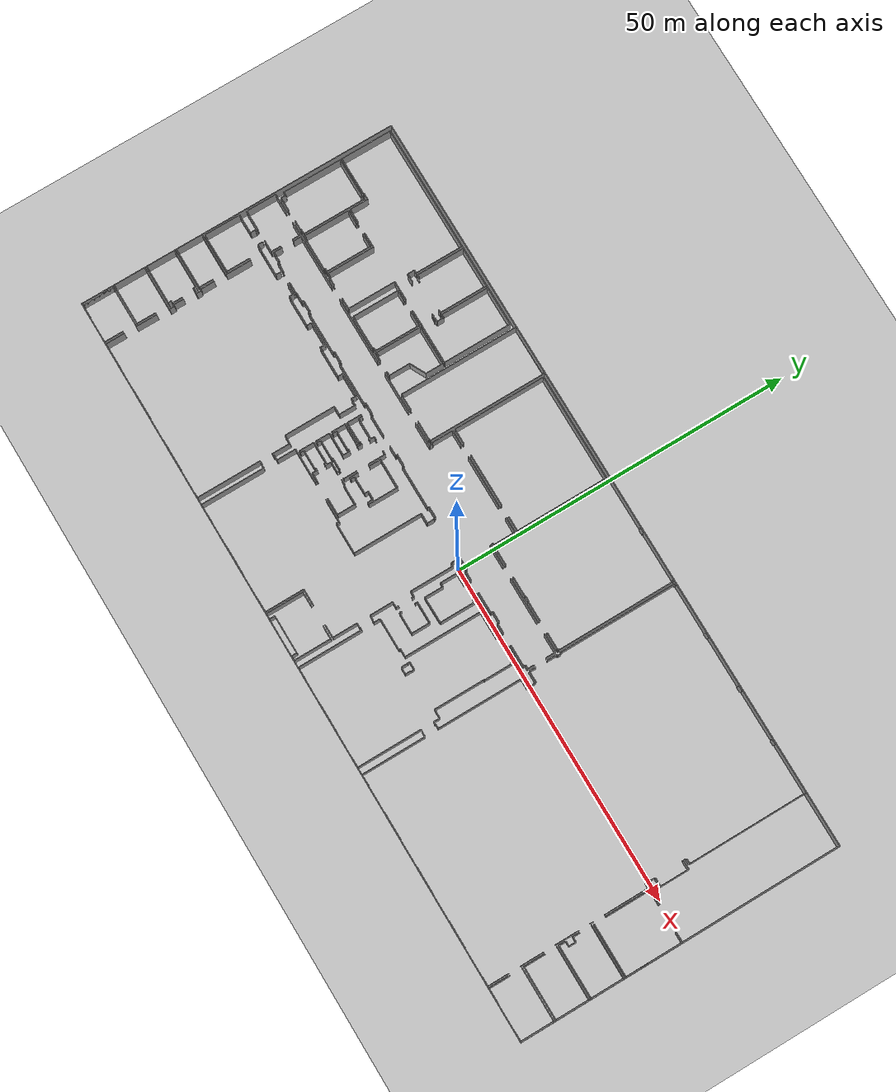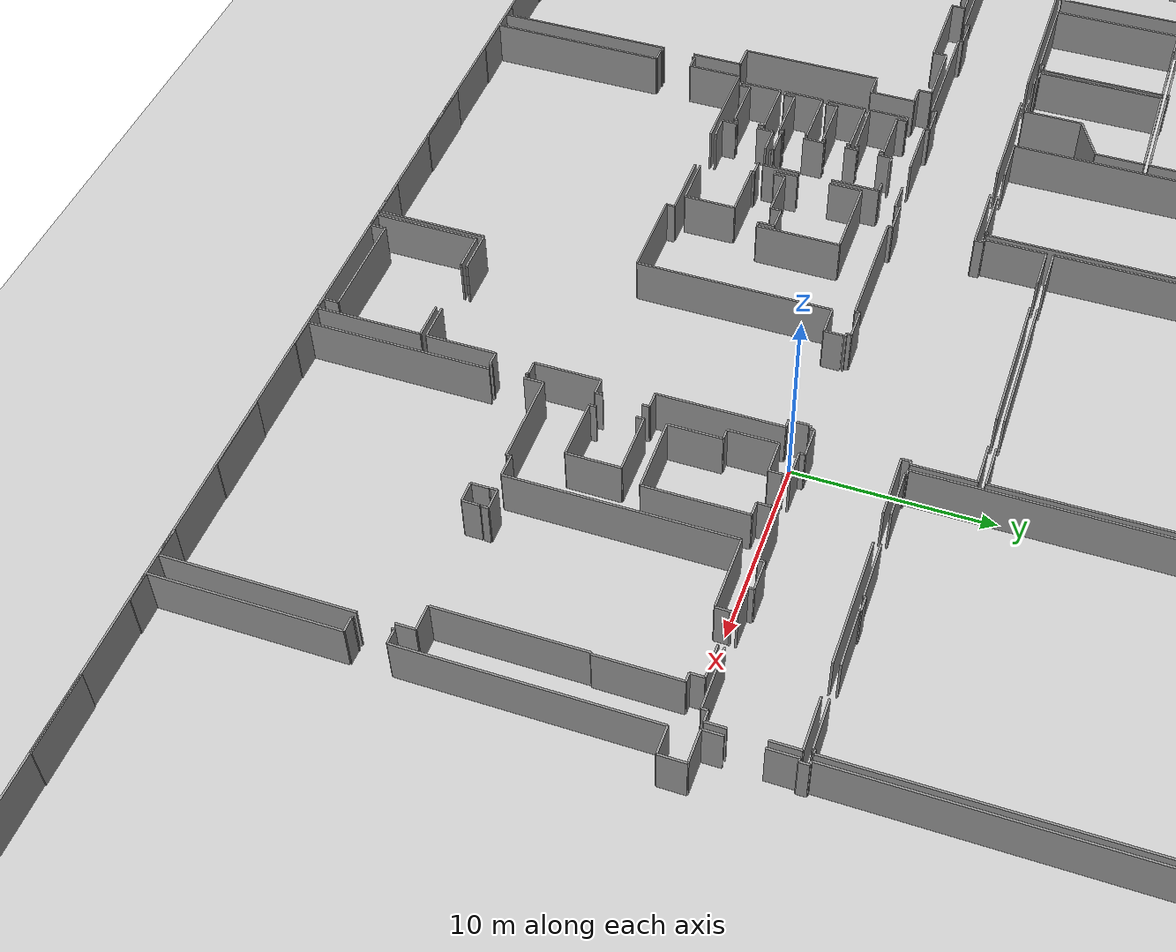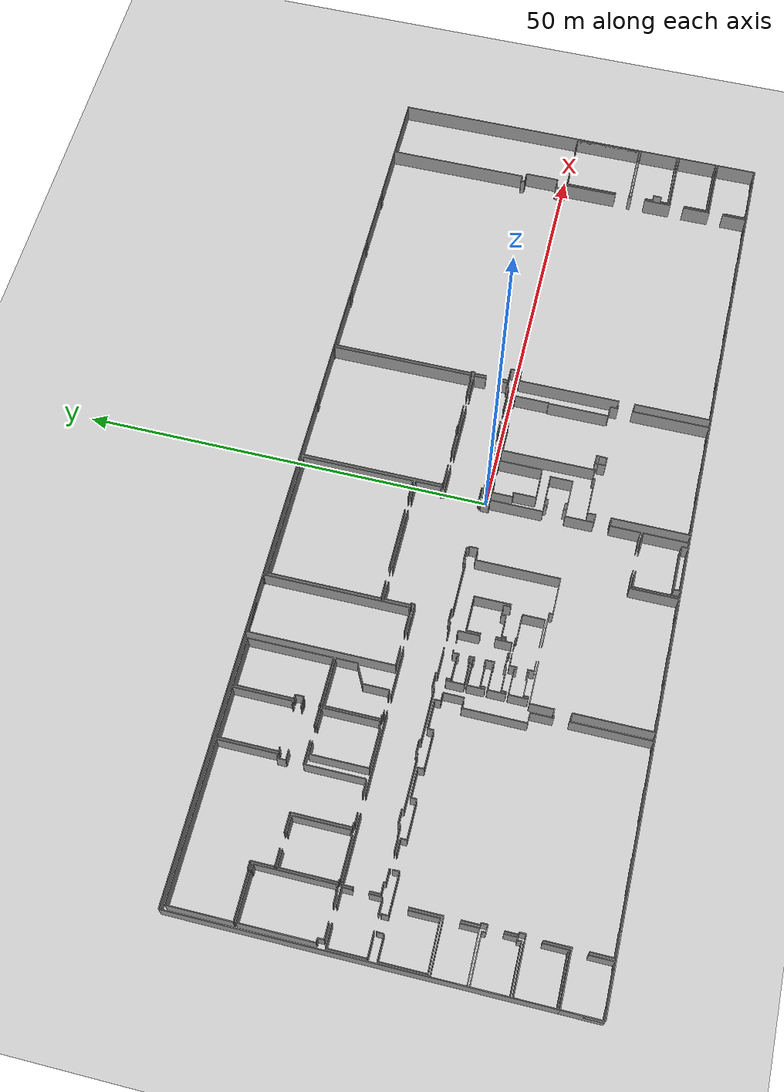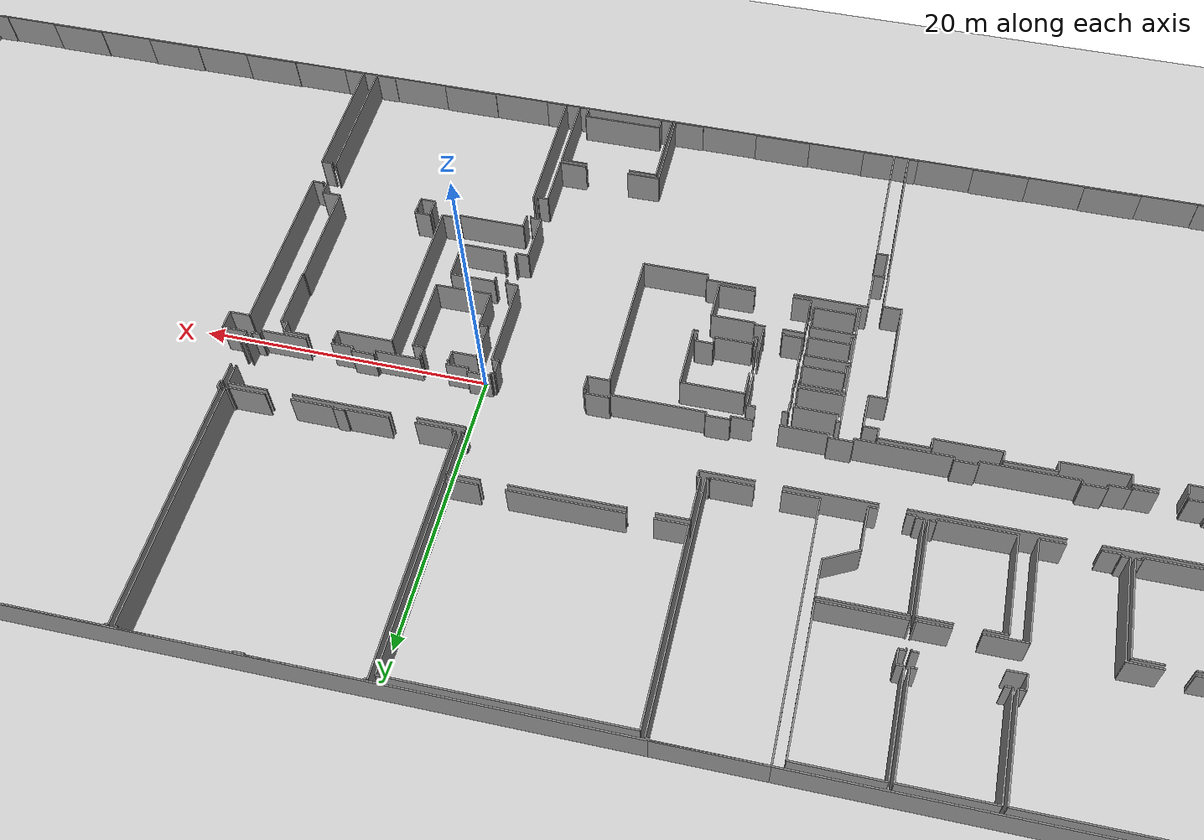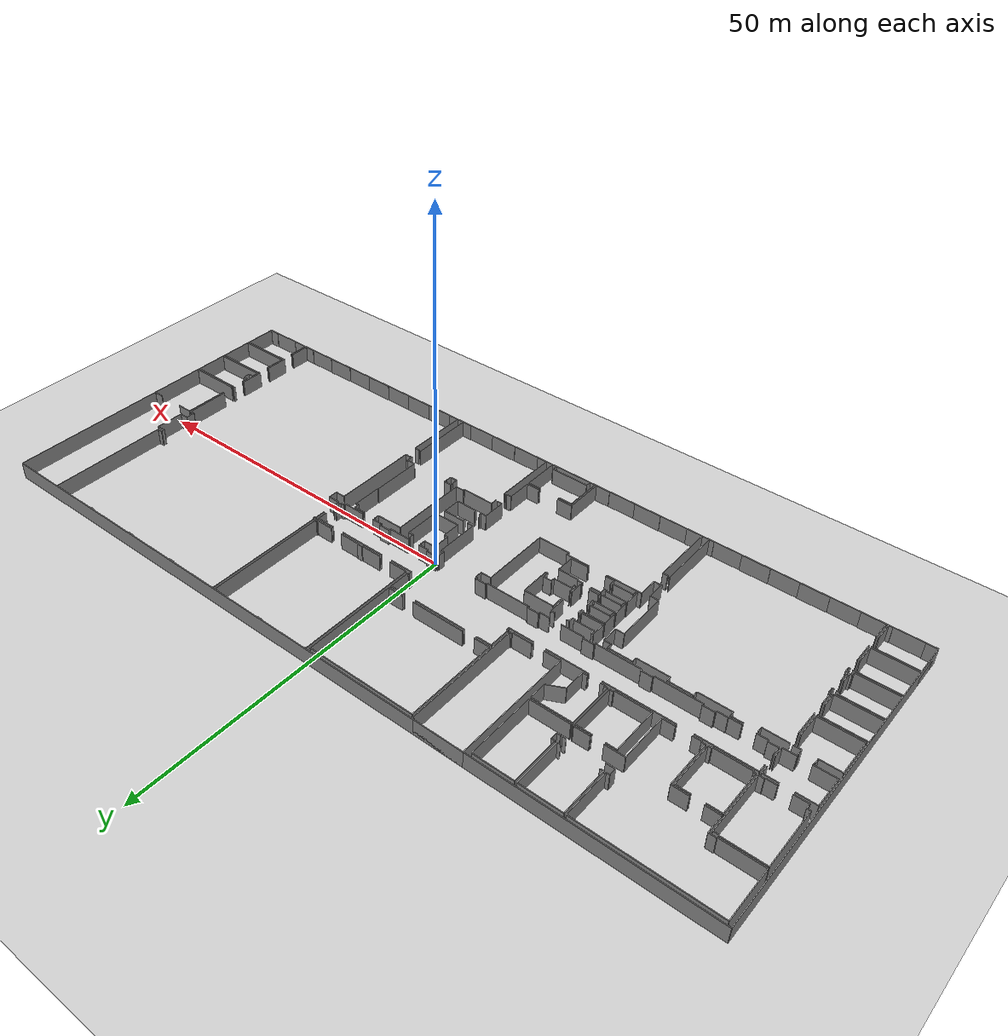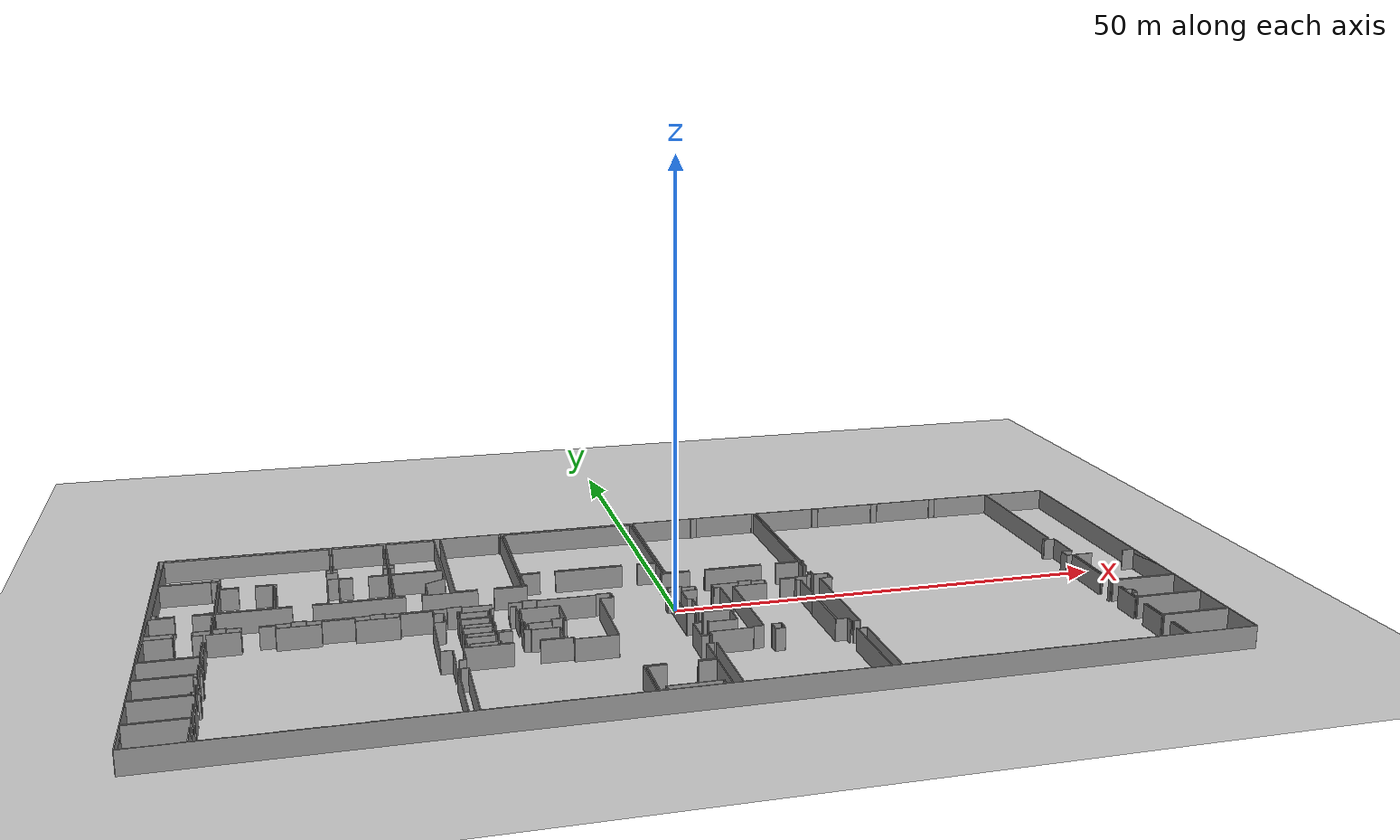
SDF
<sdf version="1.6">
  <world name="default">
    <light name="sun" type="directional">
      <cast_shadows>1</cast_shadows>
      <pose frame="">0 0 10 0 -0 0</pose>
      <diffuse>0.8 0.8 0.8 1</diffuse>
      <specular>0.1 0.1 0.1 1</specular>
      <attenuation>
        <range>1000</range>
        <constant>0.9</constant>
        <linear>0.01</linear>
        <quadratic>0.001</quadratic>
      </attenuation>
      <direction>-0.5 0.5 -1</direction>
    </light>
    <model name="ground_plane">
      <static>1</static>
      <link name="link">
        <collision name="collision">
          <geometry>
            <plane>
              <normal>0 0 1</normal>
              <size>100 100</size>
            </plane>
          </geometry>
          <surface>
            <friction>
              <ode>
                <mu>100</mu>
                <mu2>50</mu2>
              </ode>
              <torsional>
                <ode />
              </torsional>
            </friction>
            <contact>
              <ode />
            </contact>
            <bounce />
          </surface>
          <max_contacts>10</max_contacts>
        </collision>
        <visual name="visual">
          <cast_shadows>0</cast_shadows>
          <geometry>
            <plane>
              <normal>0 0 1</normal>
              <size>100 100</size>
            </plane>
          </geometry>
          <material>
            <script>
              <uri>file://media/materials/scripts/gazebo.material</uri>
              <name>Gazebo/Grey</name>
            </script>
          </material>
        </visual>
        <self_collide>0</self_collide>
        <kinematic>0</kinematic>
        <gravity>1</gravity>
      </link>
    </model>
    <gravity>0 0 -9.8</gravity>
    <magnetic_field>6e-06 2.3e-05 -4.2e-05</magnetic_field>
    <atmosphere type="adiabatic" />
    <physics default="0" name="default_physics" type="ode">
      <max_step_size>0.001</max_step_size>
      <real_time_factor>1</real_time_factor>
      <real_time_update_rate>1000</real_time_update_rate>
    </physics>
    <scene>
      <ambient>0.4 0.4 0.4 1</ambient>
      <background>0.7 0.7 0.7 1</background>
      <shadows>1</shadows>
    </scene>
    <spherical_coordinates>
      <surface_model>EARTH_WGS84</surface_model>
      <latitude_deg>0</latitude_deg>
      <longitude_deg>0</longitude_deg>
      <elevation>0</elevation>
      <heading_deg>0</heading_deg>
    </spherical_coordinates>
  <model name="50057023">
		<static>1</static>
		<link name="Wall_0">
			<collision name="Wall_0_Collision">
				<geometry>
					<box>
						<size>0.727358910242 0.1 2.5</size>
					</box>
				</geometry>
				<pose frame="">0.363679455121 0 1.25 0 0 0</pose>
			</collision>
			<visual name="Wall_0_Visual">
				<pose frame="">0.363679455121 0 1.25 0 0 0</pose>
				<geometry>
					<box>
						<size>0.727358910242 0.1 2.5</size>
					</box>
				</geometry>
				<material>
					<script>
						<uri>file://media/materials/scripts/gazebo.material</uri>
						<name>Gazebo/Grey</name>
					</script>
					<ambient>1 1 1 1</ambient>
				</material>
			</visual>
			<pose frame="">1.07209078615 -17.7010946504 0 0 0 1.57079632679</pose>
		</link>
		<link name="Wall_1">
			<collision name="Wall_1_Collision">
				<geometry>
					<box>
						<size>0.495932290604 0.1 2.5</size>
					</box>
				</geometry>
				<pose frame="">0.247966145302 0 1.25 0 0 0</pose>
			</collision>
			<visual name="Wall_1_Visual">
				<pose frame="">0.247966145302 0 1.25 0 0 0</pose>
				<geometry>
					<box>
						<size>0.495932290604 0.1 2.5</size>
					</box>
				</geometry>
				<material>
					<script>
						<uri>file://media/materials/scripts/gazebo.material</uri>
						<name>Gazebo/Grey</name>
					</script>
					<ambient>1 1 1 1</ambient>
				</material>
			</visual>
			<pose frame="">1.07209078615 -16.9737357402 0 0 0 3.14159265359</pose>
		</link>
		<link name="Wall_2">
			<collision name="Wall_2_Collision">
				<geometry>
					<box>
						<size>8.71259120503 0.1 2.5</size>
					</box>
				</geometry>
				<pose frame="">4.35629560251 0 1.25 0 0 0</pose>
			</collision>
			<visual name="Wall_2_Visual">
				<pose frame="">4.35629560251 0 1.25 0 0 0</pose>
				<geometry>
					<box>
						<size>8.71259120503 0.1 2.5</size>
					</box>
				</geometry>
				<material>
					<script>
						<uri>file://media/materials/scripts/gazebo.material</uri>
						<name>Gazebo/Grey</name>
					</script>
					<ambient>1 1 1 1</ambient>
				</material>
			</visual>
			<pose frame="">0.57615849555 -16.9737357402 0 0 0 1.57079632679</pose>
		</link>
		<link name="Wall_3">
			<collision name="Wall_3_Collision">
				<geometry>
					<box>
						<size>5.60645561134 0.1 2.5</size>
					</box>
				</geometry>
				<pose frame="">2.80322780567 0 1.25 0 0 0</pose>
			</collision>
			<visual name="Wall_3_Visual">
				<pose frame="">2.80322780567 0 1.25 0 0 0</pose>
				<geometry>
					<box>
						<size>5.60645561134 0.1 2.5</size>
					</box>
				</geometry>
				<material>
					<script>
						<uri>file://media/materials/scripts/gazebo.material</uri>
						<name>Gazebo/Grey</name>
					</script>
					<ambient>1 1 1 1</ambient>
				</material>
			</visual>
			<pose frame="">0.57615849555 -8.26114453518 0 0 0 0.0</pose>
		</link>
		<link name="Wall_4">
			<collision name="Wall_4_Collision">
				<geometry>
					<box>
						<size>0.108362409524 0.1 2.5</size>
					</box>
				</geometry>
				<pose frame="">0.0541812047619 0 1.25 0 0 0</pose>
			</collision>
			<visual name="Wall_4_Visual">
				<pose frame="">0.0541812047619 0 1.25 0 0 0</pose>
				<geometry>
					<box>
						<size>0.108362409524 0.1 2.5</size>
					</box>
				</geometry>
				<material>
					<script>
						<uri>file://media/materials/scripts/gazebo.material</uri>
						<name>Gazebo/Grey</name>
					</script>
					<ambient>1 1 1 1</ambient>
				</material>
			</visual>
			<pose frame="">6.18261410688 -8.26114453518 0 0 0 -1.57079632679</pose>
		</link>
		<link name="Wall_5">
			<collision name="Wall_5_Collision">
				<geometry>
					<box>
						<size>0.725077596357 0.1 2.5</size>
					</box>
				</geometry>
				<pose frame="">0.362538798178 0 1.25 0 0 0</pose>
			</collision>
			<visual name="Wall_5_Visual">
				<pose frame="">0.362538798178 0 1.25 0 0 0</pose>
				<geometry>
					<box>
						<size>0.725077596357 0.1 2.5</size>
					</box>
				</geometry>
				<material>
					<script>
						<uri>file://media/materials/scripts/gazebo.material</uri>
						<name>Gazebo/Grey</name>
					</script>
					<ambient>1 1 1 1</ambient>
				</material>
			</visual>
			<pose frame="">6.18261410688 -8.3695069447 0 0 0 0.0</pose>
		</link>
		<link name="Wall_6">
			<collision name="Wall_6_Collision">
				<geometry>
					<box>
						<size>9.20839675597 0.1 2.5</size>
					</box>
				</geometry>
				<pose frame="">4.60419837799 0 1.25 0 0 0</pose>
			</collision>
			<visual name="Wall_6_Visual">
				<pose frame="">4.60419837799 0 1.25 0 0 0</pose>
				<geometry>
					<box>
						<size>9.20839675597 0.1 2.5</size>
					</box>
				</geometry>
				<material>
					<script>
						<uri>file://media/materials/scripts/gazebo.material</uri>
						<name>Gazebo/Grey</name>
					</script>
					<ambient>1 1 1 1</ambient>
				</material>
			</visual>
			<pose frame="">6.90769170324 -8.3695069447 0 0 0 -1.57079632679</pose>
		</link>
		<link name="Wall_7">
			<collision name="Wall_7_Collision">
				<geometry>
					<box>
						<size>0.708347961202 0.1 2.5</size>
					</box>
				</geometry>
				<pose frame="">0.354173980601 0 1.25 0 0 0</pose>
			</collision>
			<visual name="Wall_7_Visual">
				<pose frame="">0.354173980601 0 1.25 0 0 0</pose>
				<geometry>
					<box>
						<size>0.708347961202 0.1 2.5</size>
					</box>
				</geometry>
				<material>
					<script>
						<uri>file://media/materials/scripts/gazebo.material</uri>
						<name>Gazebo/Grey</name>
					</script>
					<ambient>1 1 1 1</ambient>
				</material>
			</visual>
			<pose frame="">6.90769170324 -17.5779037007 0 0 0 3.14159265359</pose>
		</link>
		<link name="Wall_8">
			<collision name="Wall_8_Collision">
				<geometry>
					<box>
						<size>0.108362409524 0.1 2.5</size>
					</box>
				</geometry>
				<pose frame="">0.0541812047619 0 1.25 0 0 0</pose>
			</collision>
			<visual name="Wall_8_Visual">
				<pose frame="">0.0541812047619 0 1.25 0 0 0</pose>
				<geometry>
					<box>
						<size>0.108362409524 0.1 2.5</size>
					</box>
				</geometry>
				<material>
					<script>
						<uri>file://media/materials/scripts/gazebo.material</uri>
						<name>Gazebo/Grey</name>
					</script>
					<ambient>1 1 1 1</ambient>
				</material>
			</visual>
			<pose frame="">6.19934374204 -17.5779037007 0 0 0 -1.57079632679</pose>
		</link>
		<link name="Wall_9">
			<collision name="Wall_9_Collision">
				<geometry>
					<box>
						<size>1.47499616613 0.1 2.5</size>
					</box>
				</geometry>
				<pose frame="">0.737498083063 0 1.25 0 0 0</pose>
			</collision>
			<visual name="Wall_9_Visual">
				<pose frame="">0.737498083063 0 1.25 0 0 0</pose>
				<geometry>
					<box>
						<size>1.47499616613 0.1 2.5</size>
					</box>
				</geometry>
				<material>
					<script>
						<uri>file://media/materials/scripts/gazebo.material</uri>
						<name>Gazebo/Grey</name>
					</script>
					<ambient>1 1 1 1</ambient>
				</material>
			</visual>
			<pose frame="">6.19934374204 -17.6862661102 0 0 0 3.14159265359</pose>
		</link>
		<link name="Wall_10">
			<collision name="Wall_10_Collision">
				<geometry>
					<box>
						<size>1.90115273435 0.1 2.5</size>
					</box>
				</geometry>
				<pose frame="">0.950576367176 0 1.25 0 0 0</pose>
			</collision>
			<visual name="Wall_10_Visual">
				<pose frame="">0.950576367176 0 1.25 0 0 0</pose>
				<geometry>
					<box>
						<size>1.90115273435 0.1 2.5</size>
					</box>
				</geometry>
				<material>
					<script>
						<uri>file://media/materials/scripts/gazebo.material</uri>
						<name>Gazebo/Grey</name>
					</script>
					<ambient>1 1 1 1</ambient>
				</material>
			</visual>
			<pose frame="">2.97318569008 -17.6862661102 0 0 0 -3.13379281177</pose>
		</link>
		<link name="Wall_11">
			<collision name="Wall_11_Collision">
				<geometry>
					<box>
						<size>6.70021887939 0.1 2.5</size>
					</box>
				</geometry>
				<pose frame="">3.3501094397 0 1.25 0 0 0</pose>
			</collision>
			<visual name="Wall_11_Visual">
				<pose frame="">3.3501094397 0 1.25 0 0 0</pose>
				<geometry>
					<box>
						<size>6.70021887939 0.1 2.5</size>
					</box>
				</geometry>
				<material>
					<script>
						<uri>file://media/materials/scripts/gazebo.material</uri>
						<name>Gazebo/Grey</name>
					</script>
					<ambient>1 1 1 1</ambient>
				</material>
			</visual>
			<pose frame="">7.1862654765 -17.598689005 0 0 0 1.57079632679</pose>
		</link>
		<link name="Wall_12">
			<collision name="Wall_12_Collision">
				<geometry>
					<box>
						<size>2.01123166869 0.1 2.5</size>
					</box>
				</geometry>
				<pose frame="">1.00561583435 0 1.25 0 0 0</pose>
			</collision>
			<visual name="Wall_12_Visual">
				<pose frame="">1.00561583435 0 1.25 0 0 0</pose>
				<geometry>
					<box>
						<size>2.01123166869 0.1 2.5</size>
					</box>
				</geometry>
				<material>
					<script>
						<uri>file://media/materials/scripts/gazebo.material</uri>
						<name>Gazebo/Grey</name>
					</script>
					<ambient>1 1 1 1</ambient>
				</material>
			</visual>
			<pose frame="">7.1862654765 -10.8984701256 0 0 0 0.0</pose>
		</link>
		<link name="Wall_13">
			<collision name="Wall_13_Collision">
				<geometry>
					<box>
						<size>1.97219585333 0.1 2.5</size>
					</box>
				</geometry>
				<pose frame="">0.986097926666 0 1.25 0 0 0</pose>
			</collision>
			<visual name="Wall_13_Visual">
				<pose frame="">0.986097926666 0 1.25 0 0 0</pose>
				<geometry>
					<box>
						<size>1.97219585333 0.1 2.5</size>
					</box>
				</geometry>
				<material>
					<script>
						<uri>file://media/materials/scripts/gazebo.material</uri>
						<name>Gazebo/Grey</name>
					</script>
					<ambient>1 1 1 1</ambient>
				</material>
			</visual>
			<pose frame="">10.9546157951 -10.8984701256 0 0 0 0.0</pose>
		</link>
		<link name="Wall_14">
			<collision name="Wall_14_Collision">
				<geometry>
					<box>
						<size>6.6829822856 0.1 2.5</size>
					</box>
				</geometry>
				<pose frame="">3.3414911428 0 1.25 0 0 0</pose>
			</collision>
			<visual name="Wall_14_Visual">
				<pose frame="">3.3414911428 0 1.25 0 0 0</pose>
				<geometry>
					<box>
						<size>6.6829822856 0.1 2.5</size>
					</box>
				</geometry>
				<material>
					<script>
						<uri>file://media/materials/scripts/gazebo.material</uri>
						<name>Gazebo/Grey</name>
					</script>
					<ambient>1 1 1 1</ambient>
				</material>
			</visual>
			<pose frame="">12.9268116484 -10.8984701256 0 0 0 -1.57079632679</pose>
		</link>
		<link name="Wall_15">
			<collision name="Wall_15_Collision">
				<geometry>
					<box>
						<size>0.442321414313 0.1 2.5</size>
					</box>
				</geometry>
				<pose frame="">0.221160707157 0 1.25 0 0 0</pose>
			</collision>
			<visual name="Wall_15_Visual">
				<pose frame="">0.221160707157 0 1.25 0 0 0</pose>
				<geometry>
					<box>
						<size>0.442321414313 0.1 2.5</size>
					</box>
				</geometry>
				<material>
					<script>
						<uri>file://media/materials/scripts/gazebo.material</uri>
						<name>Gazebo/Grey</name>
					</script>
					<ambient>1 1 1 1</ambient>
				</material>
			</visual>
			<pose frame="">12.9268116484 -17.5814524112 0 0 0 3.14159265359</pose>
		</link>
		<link name="Wall_16">
			<collision name="Wall_16_Collision">
				<geometry>
					<box>
						<size>0.171605499994 0.1 2.5</size>
					</box>
				</geometry>
				<pose frame="">0.0858027499971 0 1.25 0 0 0</pose>
			</collision>
			<visual name="Wall_16_Visual">
				<pose frame="">0.0858027499971 0 1.25 0 0 0</pose>
				<geometry>
					<box>
						<size>0.171605499994 0.1 2.5</size>
					</box>
				</geometry>
				<material>
					<script>
						<uri>file://media/materials/scripts/gazebo.material</uri>
						<name>Gazebo/Grey</name>
					</script>
					<ambient>1 1 1 1</ambient>
				</material>
			</visual>
			<pose frame="">12.4844902341 -17.5814524112 0 0 0 -1.57079632679</pose>
		</link>
		<link name="Wall_17">
			<collision name="Wall_17_Collision">
				<geometry>
					<box>
						<size>5.02066490161 0.1 2.5</size>
					</box>
				</geometry>
				<pose frame="">2.5103324508 0 1.25 0 0 0</pose>
			</collision>
			<visual name="Wall_17_Visual">
				<pose frame="">2.5103324508 0 1.25 0 0 0</pose>
				<geometry>
					<box>
						<size>5.02066490161 0.1 2.5</size>
					</box>
				</geometry>
				<material>
					<script>
						<uri>file://media/materials/scripts/gazebo.material</uri>
						<name>Gazebo/Grey</name>
					</script>
					<ambient>1 1 1 1</ambient>
				</material>
			</visual>
			<pose frame="">12.4844902341 -17.7530579112 0 0 0 3.14159265359</pose>
		</link>
		<link name="Wall_18">
			<collision name="Wall_18_Collision">
				<geometry>
					<box>
						<size>0.15018649741 0.1 2.5</size>
					</box>
				</geometry>
				<pose frame="">0.075093248705 0 1.25 0 0 0</pose>
			</collision>
			<visual name="Wall_18_Visual">
				<pose frame="">0.075093248705 0 1.25 0 0 0</pose>
				<geometry>
					<box>
						<size>0.15018649741 0.1 2.5</size>
					</box>
				</geometry>
				<material>
					<script>
						<uri>file://media/materials/scripts/gazebo.material</uri>
						<name>Gazebo/Grey</name>
					</script>
					<ambient>1 1 1 1</ambient>
				</material>
			</visual>
			<pose frame="">7.46382533247 -17.7530579112 0 0 0 1.57079632679</pose>
		</link>
		<link name="Wall_19">
			<collision name="Wall_19_Collision">
				<geometry>
					<box>
						<size>0.277591365484 0.1 2.5</size>
					</box>
				</geometry>
				<pose frame="">0.138795682742 0 1.25 0 0 0</pose>
			</collision>
			<visual name="Wall_19_Visual">
				<pose frame="">0.138795682742 0 1.25 0 0 0</pose>
				<geometry>
					<box>
						<size>0.277591365484 0.1 2.5</size>
					</box>
				</geometry>
				<material>
					<script>
						<uri>file://media/materials/scripts/gazebo.material</uri>
						<name>Gazebo/Grey</name>
					</script>
					<ambient>1 1 1 1</ambient>
				</material>
			</visual>
			<pose frame="">7.46382533247 -17.6028714137 0 0 0 3.12652530077</pose>
		</link>
		<link name="Wall_20">
			<collision name="Wall_20_Collision">
				<geometry>
					<box>
						<size>7.51338053963 0.1 2.5</size>
					</box>
				</geometry>
				<pose frame="">3.75669026982 0 1.25 0 0 0</pose>
			</collision>
			<visual name="Wall_20_Visual">
				<pose frame="">3.75669026982 0 1.25 0 0 0</pose>
				<geometry>
					<box>
						<size>7.51338053963 0.1 2.5</size>
					</box>
				</geometry>
				<material>
					<script>
						<uri>file://media/materials/scripts/gazebo.material</uri>
						<name>Gazebo/Grey</name>
					</script>
					<ambient>1 1 1 1</ambient>
				</material>
			</visual>
			<pose frame="">0.570201731517 -8.01096044582 0 0 0 1.57079632679</pose>
		</link>
		<link name="Wall_21">
			<collision name="Wall_21_Collision">
				<geometry>
					<box>
						<size>18.6421366279 0.1 2.5</size>
					</box>
				</geometry>
				<pose frame="">9.32106831394 0 1.25 0 0 0</pose>
			</collision>
			<visual name="Wall_21_Visual">
				<pose frame="">9.32106831394 0 1.25 0 0 0</pose>
				<geometry>
					<box>
						<size>18.6421366279 0.1 2.5</size>
					</box>
				</geometry>
				<material>
					<script>
						<uri>file://media/materials/scripts/gazebo.material</uri>
						<name>Gazebo/Grey</name>
					</script>
					<ambient>1 1 1 1</ambient>
				</material>
			</visual>
			<pose frame="">0.570201731517 -0.497579906187 0 0 0 0.0</pose>
		</link>
		<link name="Wall_22">
			<collision name="Wall_22_Collision">
				<geometry>
					<box>
						<size>7.08639462421 0.1 2.5</size>
					</box>
				</geometry>
				<pose frame="">3.54319731211 0 1.25 0 0 0</pose>
			</collision>
			<visual name="Wall_22_Visual">
				<pose frame="">3.54319731211 0 1.25 0 0 0</pose>
				<geometry>
					<box>
						<size>7.08639462421 0.1 2.5</size>
					</box>
				</geometry>
				<material>
					<script>
						<uri>file://media/materials/scripts/gazebo.material</uri>
						<name>Gazebo/Grey</name>
					</script>
					<ambient>1 1 1 1</ambient>
				</material>
			</visual>
			<pose frame="">19.2123383594 -0.497579906187 0 0 0 -1.57079632679</pose>
		</link>
		<link name="Wall_23">
			<collision name="Wall_23_Collision">
				<geometry>
					<box>
						<size>0.473879589718 0.1 2.5</size>
					</box>
				</geometry>
				<pose frame="">0.236939794859 0 1.25 0 0 0</pose>
			</collision>
			<visual name="Wall_23_Visual">
				<pose frame="">0.236939794859 0 1.25 0 0 0</pose>
				<geometry>
					<box>
						<size>0.473879589718 0.1 2.5</size>
					</box>
				</geometry>
				<material>
					<script>
						<uri>file://media/materials/scripts/gazebo.material</uri>
						<name>Gazebo/Grey</name>
					</script>
					<ambient>1 1 1 1</ambient>
				</material>
			</visual>
			<pose frame="">19.2123383594 -7.5839745304 0 0 0 3.14159265359</pose>
		</link>
		<link name="Wall_24">
			<collision name="Wall_24_Collision">
				<geometry>
					<box>
						<size>1.02494363254 0.1 2.5</size>
					</box>
				</geometry>
				<pose frame="">0.512471816268 0 1.25 0 0 0</pose>
			</collision>
			<visual name="Wall_24_Visual">
				<pose frame="">0.512471816268 0 1.25 0 0 0</pose>
				<geometry>
					<box>
						<size>1.02494363254 0.1 2.5</size>
					</box>
				</geometry>
				<material>
					<script>
						<uri>file://media/materials/scripts/gazebo.material</uri>
						<name>Gazebo/Grey</name>
					</script>
					<ambient>1 1 1 1</ambient>
				</material>
			</visual>
			<pose frame="">18.7384587697 -7.5839745304 0 0 0 -1.57079632679</pose>
		</link>
		<link name="Wall_25">
			<collision name="Wall_25_Collision">
				<geometry>
					<box>
						<size>1.23431755129 0.1 2.5</size>
					</box>
				</geometry>
				<pose frame="">0.617158775644 0 1.25 0 0 0</pose>
			</collision>
			<visual name="Wall_25_Visual">
				<pose frame="">0.617158775644 0 1.25 0 0 0</pose>
				<geometry>
					<box>
						<size>1.23431755129 0.1 2.5</size>
					</box>
				</geometry>
				<material>
					<script>
						<uri>file://media/materials/scripts/gazebo.material</uri>
						<name>Gazebo/Grey</name>
					</script>
					<ambient>1 1 1 1</ambient>
				</material>
			</visual>
			<pose frame="">18.7384587697 -8.60891816293 0 0 0 0.0</pose>
		</link>
		<link name="Wall_26">
			<collision name="Wall_26_Collision">
				<geometry>
					<box>
						<size>0.469570441269 0.1 2.5</size>
					</box>
				</geometry>
				<pose frame="">0.234785220635 0 1.25 0 0 0</pose>
			</collision>
			<visual name="Wall_26_Visual">
				<pose frame="">0.234785220635 0 1.25 0 0 0</pose>
				<geometry>
					<box>
						<size>0.469570441269 0.1 2.5</size>
					</box>
				</geometry>
				<material>
					<script>
						<uri>file://media/materials/scripts/gazebo.material</uri>
						<name>Gazebo/Grey</name>
					</script>
					<ambient>1 1 1 1</ambient>
				</material>
			</visual>
			<pose frame="">25.0538960405 -8.60891816293 0 0 0 0.0</pose>
		</link>
		<link name="Wall_27">
			<collision name="Wall_27_Collision">
				<geometry>
					<box>
						<size>0.1259792223 0.1 2.5</size>
					</box>
				</geometry>
				<pose frame="">0.06298961115 0 1.25 0 0 0</pose>
			</collision>
			<visual name="Wall_27_Visual">
				<pose frame="">0.06298961115 0 1.25 0 0 0</pose>
				<geometry>
					<box>
						<size>0.1259792223 0.1 2.5</size>
					</box>
				</geometry>
				<material>
					<script>
						<uri>file://media/materials/scripts/gazebo.material</uri>
						<name>Gazebo/Grey</name>
					</script>
					<ambient>1 1 1 1</ambient>
				</material>
			</visual>
			<pose frame="">25.5234664818 -8.60891816293 0 0 0 -1.57079632679</pose>
		</link>
		<link name="Wall_28">
			<collision name="Wall_28_Collision">
				<geometry>
					<box>
						<size>0.12610596196 0.1 2.5</size>
					</box>
				</geometry>
				<pose frame="">0.0630529809802 0 1.25 0 0 0</pose>
			</collision>
			<visual name="Wall_28_Visual">
				<pose frame="">0.0630529809802 0 1.25 0 0 0</pose>
				<geometry>
					<box>
						<size>0.12610596196 0.1 2.5</size>
					</box>
				</geometry>
				<material>
					<script>
						<uri>file://media/materials/scripts/gazebo.material</uri>
						<name>Gazebo/Grey</name>
					</script>
					<ambient>1 1 1 1</ambient>
				</material>
			</visual>
			<pose frame="">25.5234664818 -10.4807362053 0 0 0 -1.57079632679</pose>
		</link>
		<link name="Wall_29">
			<collision name="Wall_29_Collision">
				<geometry>
					<box>
						<size>2.21654991832 0.1 2.5</size>
					</box>
				</geometry>
				<pose frame="">1.10827495916 0 1.25 0 0 0</pose>
			</collision>
			<visual name="Wall_29_Visual">
				<pose frame="">1.10827495916 0 1.25 0 0 0</pose>
				<geometry>
					<box>
						<size>2.21654991832 0.1 2.5</size>
					</box>
				</geometry>
				<material>
					<script>
						<uri>file://media/materials/scripts/gazebo.material</uri>
						<name>Gazebo/Grey</name>
					</script>
					<ambient>1 1 1 1</ambient>
				</material>
			</visual>
			<pose frame="">25.5234664818 -10.6068421673 0 0 0 3.14159265359</pose>
		</link>
		<link name="Wall_30">
			<collision name="Wall_30_Collision">
				<geometry>
					<box>
						<size>2.7690080974 0.1 2.5</size>
					</box>
				</geometry>
				<pose frame="">1.3845040487 0 1.25 0 0 0</pose>
			</collision>
			<visual name="Wall_30_Visual">
				<pose frame="">1.3845040487 0 1.25 0 0 0</pose>
				<geometry>
					<box>
						<size>2.7690080974 0.1 2.5</size>
					</box>
				</geometry>
				<material>
					<script>
						<uri>file://media/materials/scripts/gazebo.material</uri>
						<name>Gazebo/Grey</name>
					</script>
					<ambient>1 1 1 1</ambient>
				</material>
			</visual>
			<pose frame="">21.5349693734 -10.6068421673 0 0 0 3.14159265359</pose>
		</link>
		<link name="Wall_31">
			<collision name="Wall_31_Collision">
				<geometry>
					<box>
						<size>7.12238868772 0.1 2.5</size>
					</box>
				</geometry>
				<pose frame="">3.56119434386 0 1.25 0 0 0</pose>
			</collision>
			<visual name="Wall_31_Visual">
				<pose frame="">3.56119434386 0 1.25 0 0 0</pose>
				<geometry>
					<box>
						<size>7.12238868772 0.1 2.5</size>
					</box>
				</geometry>
				<material>
					<script>
						<uri>file://media/materials/scripts/gazebo.material</uri>
						<name>Gazebo/Grey</name>
					</script>
					<ambient>1 1 1 1</ambient>
				</material>
			</visual>
			<pose frame="">18.765961276 -10.6068421673 0 0 0 -1.57079632679</pose>
		</link>
		<link name="Wall_32">
			<collision name="Wall_32_Collision">
				<geometry>
					<box>
						<size>1.70262059596 0.1 2.5</size>
					</box>
				</geometry>
				<pose frame="">0.851310297978 0 1.25 0 0 0</pose>
			</collision>
			<visual name="Wall_32_Visual">
				<pose frame="">0.851310297978 0 1.25 0 0 0</pose>
				<geometry>
					<box>
						<size>1.70262059596 0.1 2.5</size>
					</box>
				</geometry>
				<material>
					<script>
						<uri>file://media/materials/scripts/gazebo.material</uri>
						<name>Gazebo/Grey</name>
					</script>
					<ambient>1 1 1 1</ambient>
				</material>
			</visual>
			<pose frame="">18.765961276 -17.729230855 0 0 0 3.14159265359</pose>
		</link>
		<link name="Wall_33">
			<collision name="Wall_33_Collision">
				<geometry>
					<box>
						<size>1.21974249036 0.1 2.5</size>
					</box>
				</geometry>
				<pose frame="">0.609871245179 0 1.25 0 0 0</pose>
			</collision>
			<visual name="Wall_33_Visual">
				<pose frame="">0.609871245179 0 1.25 0 0 0</pose>
				<geometry>
					<box>
						<size>1.21974249036 0.1 2.5</size>
					</box>
				</geometry>
				<material>
					<script>
						<uri>file://media/materials/scripts/gazebo.material</uri>
						<name>Gazebo/Grey</name>
					</script>
					<ambient>1 1 1 1</ambient>
				</material>
			</visual>
			<pose frame="">14.9573077454 -17.729230855 0 0 0 3.14159265359</pose>
		</link>
		<link name="Wall_34">
			<collision name="Wall_34_Collision">
				<geometry>
					<box>
						<size>0.128640755166 0.1 2.5</size>
					</box>
				</geometry>
				<pose frame="">0.0643203775828 0 1.25 0 0 0</pose>
			</collision>
			<visual name="Wall_34_Visual">
				<pose frame="">0.0643203775828 0 1.25 0 0 0</pose>
				<geometry>
					<box>
						<size>0.128640755166 0.1 2.5</size>
					</box>
				</geometry>
				<material>
					<script>
						<uri>file://media/materials/scripts/gazebo.material</uri>
						<name>Gazebo/Grey</name>
					</script>
					<ambient>1 1 1 1</ambient>
				</material>
			</visual>
			<pose frame="">13.7375652551 -17.729230855 0 0 0 1.57079632679</pose>
		</link>
		<link name="Wall_35">
			<collision name="Wall_35_Collision">
				<geometry>
					<box>
						<size>0.504930806482 0.1 2.5</size>
					</box>
				</geometry>
				<pose frame="">0.252465403241 0 1.25 0 0 0</pose>
			</collision>
			<visual name="Wall_35_Visual">
				<pose frame="">0.252465403241 0 1.25 0 0 0</pose>
				<geometry>
					<box>
						<size>0.504930806482 0.1 2.5</size>
					</box>
				</geometry>
				<material>
					<script>
						<uri>file://media/materials/scripts/gazebo.material</uri>
						<name>Gazebo/Grey</name>
					</script>
					<ambient>1 1 1 1</ambient>
				</material>
			</visual>
			<pose frame="">13.7375652551 -17.6005900999 0 0 0 3.14159265359</pose>
		</link>
		<link name="Wall_36">
			<collision name="Wall_36_Collision">
				<geometry>
					<box>
						<size>6.98107396653 0.1 2.5</size>
					</box>
				</geometry>
				<pose frame="">3.49053698327 0 1.25 0 0 0</pose>
			</collision>
			<visual name="Wall_36_Visual">
				<pose frame="">3.49053698327 0 1.25 0 0 0</pose>
				<geometry>
					<box>
						<size>6.98107396653 0.1 2.5</size>
					</box>
				</geometry>
				<material>
					<script>
						<uri>file://media/materials/scripts/gazebo.material</uri>
						<name>Gazebo/Grey</name>
					</script>
					<ambient>1 1 1 1</ambient>
				</material>
			</visual>
			<pose frame="">13.2326344486 -17.6005900999 0 0 0 1.57079632679</pose>
		</link>
		<link name="Wall_37">
			<collision name="Wall_37_Collision">
				<geometry>
					<box>
						<size>2.28156736403 0.1 2.5</size>
					</box>
				</geometry>
				<pose frame="">1.14078368202 0 1.25 0 0 0</pose>
			</collision>
			<visual name="Wall_37_Visual">
				<pose frame="">1.14078368202 0 1.25 0 0 0</pose>
				<geometry>
					<box>
						<size>2.28156736403 0.1 2.5</size>
					</box>
				</geometry>
				<material>
					<script>
						<uri>file://media/materials/scripts/gazebo.material</uri>
						<name>Gazebo/Grey</name>
					</script>
					<ambient>1 1 1 1</ambient>
				</material>
			</visual>
			<pose frame="">13.2326344486 -10.6195161333 0 0 0 3.14159265359</pose>
		</link>
		<link name="Wall_38">
			<collision name="Wall_38_Collision">
				<geometry>
					<box>
						<size>2.02897522113 0.1 2.5</size>
					</box>
				</geometry>
				<pose frame="">1.01448761056 0 1.25 0 0 0</pose>
			</collision>
			<visual name="Wall_38_Visual">
				<pose frame="">1.01448761056 0 1.25 0 0 0</pose>
				<geometry>
					<box>
						<size>2.02897522113 0.1 2.5</size>
					</box>
				</geometry>
				<material>
					<script>
						<uri>file://media/materials/scripts/gazebo.material</uri>
						<name>Gazebo/Grey</name>
					</script>
					<ambient>1 1 1 1</ambient>
				</material>
			</visual>
			<pose frame="">9.20915719393 -10.6195161333 0 0 0 3.14159265359</pose>
		</link>
		<link name="Wall_39">
			<collision name="Wall_39_Collision">
				<geometry>
					<box>
						<size>2.71374960552 0.1 2.5</size>
					</box>
				</geometry>
				<pose frame="">1.35687480276 0 1.25 0 0 0</pose>
			</collision>
			<visual name="Wall_39_Visual">
				<pose frame="">1.35687480276 0 1.25 0 0 0</pose>
				<geometry>
					<box>
						<size>2.71374960552 0.1 2.5</size>
					</box>
				</geometry>
				<material>
					<script>
						<uri>file://media/materials/scripts/gazebo.material</uri>
						<name>Gazebo/Grey</name>
					</script>
					<ambient>1 1 1 1</ambient>
				</material>
			</visual>
			<pose frame="">7.1801819728 -10.6195161333 0 0 0 1.57079632679</pose>
		</link>
		<link name="Wall_40">
			<collision name="Wall_40_Collision">
				<geometry>
					<box>
						<size>0.982739325669 0.1 2.5</size>
					</box>
				</geometry>
				<pose frame="">0.491369662834 0 1.25 0 0 0</pose>
			</collision>
			<visual name="Wall_40_Visual">
				<pose frame="">0.491369662834 0 1.25 0 0 0</pose>
				<geometry>
					<box>
						<size>0.982739325669 0.1 2.5</size>
					</box>
				</geometry>
				<material>
					<script>
						<uri>file://media/materials/scripts/gazebo.material</uri>
						<name>Gazebo/Grey</name>
					</script>
					<ambient>1 1 1 1</ambient>
				</material>
			</visual>
			<pose frame="">7.1801819728 -7.9057665278 0 0 0 3.14159265359</pose>
		</link>
		<link name="Wall_41">
			<collision name="Wall_41_Collision">
				<geometry>
					<box>
						<size>0.0941675675744 0.1 2.5</size>
					</box>
				</geometry>
				<pose frame="">0.0470837837872 0 1.25 0 0 0</pose>
			</collision>
			<visual name="Wall_41_Visual">
				<pose frame="">0.0470837837872 0 1.25 0 0 0</pose>
				<geometry>
					<box>
						<size>0.0941675675744 0.1 2.5</size>
					</box>
				</geometry>
				<material>
					<script>
						<uri>file://media/materials/scripts/gazebo.material</uri>
						<name>Gazebo/Grey</name>
					</script>
					<ambient>1 1 1 1</ambient>
				</material>
			</visual>
			<pose frame="">6.19744264714 -7.9057665278 0 0 0 -1.57079632679</pose>
		</link>
		<link name="Wall_42">
			<collision name="Wall_42_Collision">
				<geometry>
					<box>
						<size>5.62725171845 0.1 2.5</size>
					</box>
				</geometry>
				<pose frame="">2.81362585923 0 1.25 0 0 0</pose>
			</collision>
			<visual name="Wall_42_Visual">
				<pose frame="">2.81362585923 0 1.25 0 0 0</pose>
				<geometry>
					<box>
						<size>5.62725171845 0.1 2.5</size>
					</box>
				</geometry>
				<material>
					<script>
						<uri>file://media/materials/scripts/gazebo.material</uri>
						<name>Gazebo/Grey</name>
					</script>
					<ambient>1 1 1 1</ambient>
				</material>
			</visual>
			<pose frame="">6.19744264714 -7.99993409538 0 0 0 -3.13963319664</pose>
		</link>
		<link name="Wall_43">
			<collision name="Wall_43_Collision">
				<geometry>
					<box>
						<size>7.09197116926 0.1 2.5</size>
					</box>
				</geometry>
				<pose frame="">3.54598558463 0 1.25 0 0 0</pose>
			</collision>
			<visual name="Wall_43_Visual">
				<pose frame="">3.54598558463 0 1.25 0 0 0</pose>
				<geometry>
					<box>
						<size>7.09197116926 0.1 2.5</size>
					</box>
				</geometry>
				<material>
					<script>
						<uri>file://media/materials/scripts/gazebo.material</uri>
						<name>Gazebo/Grey</name>
					</script>
					<ambient>1 1 1 1</ambient>
				</material>
			</visual>
			<pose frame="">19.5171472423 -7.59487414118 0 0 0 1.57079632679</pose>
		</link>
		<link name="Wall_44">
			<collision name="Wall_44_Collision">
				<geometry>
					<box>
						<size>5.98147826605 0.1 2.5</size>
					</box>
				</geometry>
				<pose frame="">2.99073913302 0 1.25 0 0 0</pose>
			</collision>
			<visual name="Wall_44_Visual">
				<pose frame="">2.99073913302 0 1.25 0 0 0</pose>
				<geometry>
					<box>
						<size>5.98147826605 0.1 2.5</size>
					</box>
				</geometry>
				<material>
					<script>
						<uri>file://media/materials/scripts/gazebo.material</uri>
						<name>Gazebo/Grey</name>
					</script>
					<ambient>1 1 1 1</ambient>
				</material>
			</visual>
			<pose frame="">19.5171472423 -0.502902971918 0 0 0 0.0</pose>
		</link>
		<link name="Wall_45">
			<collision name="Wall_45_Collision">
				<geometry>
					<box>
						<size>7.07676241003 0.1 2.5</size>
					</box>
				</geometry>
				<pose frame="">3.53838120502 0 1.25 0 0 0</pose>
			</collision>
			<visual name="Wall_45_Visual">
				<pose frame="">3.53838120502 0 1.25 0 0 0</pose>
				<geometry>
					<box>
						<size>7.07676241003 0.1 2.5</size>
					</box>
				</geometry>
				<material>
					<script>
						<uri>file://media/materials/scripts/gazebo.material</uri>
						<name>Gazebo/Grey</name>
					</script>
					<ambient>1 1 1 1</ambient>
				</material>
			</visual>
			<pose frame="">25.4986255084 -0.502902971918 0 0 0 -1.57079632679</pose>
		</link>
		<link name="Wall_46">
			<collision name="Wall_46_Collision">
				<geometry>
					<box>
						<size>0.453221025096 0.1 2.5</size>
					</box>
				</geometry>
				<pose frame="">0.226610512548 0 1.25 0 0 0</pose>
			</collision>
			<visual name="Wall_46_Visual">
				<pose frame="">0.226610512548 0 1.25 0 0 0</pose>
				<geometry>
					<box>
						<size>0.453221025096 0.1 2.5</size>
					</box>
				</geometry>
				<material>
					<script>
						<uri>file://media/materials/scripts/gazebo.material</uri>
						<name>Gazebo/Grey</name>
					</script>
					<ambient>1 1 1 1</ambient>
				</material>
			</visual>
			<pose frame="">25.4986255084 -7.57966538195 0 0 0 3.14159265359</pose>
		</link>
		<link name="Wall_47">
			<collision name="Wall_47_Collision">
				<geometry>
					<box>
						<size>0.490971580892 0.1 2.5</size>
					</box>
				</geometry>
				<pose frame="">0.245485790446 0 1.25 0 0 0</pose>
			</collision>
			<visual name="Wall_47_Visual">
				<pose frame="">0.245485790446 0 1.25 0 0 0</pose>
				<geometry>
					<box>
						<size>0.490971580892 0.1 2.5</size>
					</box>
				</geometry>
				<material>
					<script>
						<uri>file://media/materials/scripts/gazebo.material</uri>
						<name>Gazebo/Grey</name>
					</script>
					<ambient>1 1 1 1</ambient>
				</material>
			</visual>
			<pose frame="">20.0078832069 -7.57966538195 0 0 0 -3.11061083473</pose>
		</link>
		<link name="Wall_48">
			<collision name="Wall_48_Collision">
				<geometry>
					<box>
						<size>7.09513966077 0.1 2.5</size>
					</box>
				</geometry>
				<pose frame="">3.54756983038 0 1.25 0 0 0</pose>
			</collision>
			<visual name="Wall_48_Visual">
				<pose frame="">3.54756983038 0 1.25 0 0 0</pose>
				<geometry>
					<box>
						<size>7.09513966077 0.1 2.5</size>
					</box>
				</geometry>
				<material>
					<script>
						<uri>file://media/materials/scripts/gazebo.material</uri>
						<name>Gazebo/Grey</name>
					</script>
					<ambient>1 1 1 1</ambient>
				</material>
			</visual>
			<pose frame="">25.8064761432 -7.5951276205 0 0 0 1.57079632679</pose>
		</link>
		<link name="Wall_49">
			<collision name="Wall_49_Collision">
				<geometry>
					<box>
						<size>5.75309339826 0.1 2.5</size>
					</box>
				</geometry>
				<pose frame="">2.87654669913 0 1.25 0 0 0</pose>
			</collision>
			<visual name="Wall_49_Visual">
				<pose frame="">2.87654669913 0 1.25 0 0 0</pose>
				<geometry>
					<box>
						<size>5.75309339826 0.1 2.5</size>
					</box>
				</geometry>
				<material>
					<script>
						<uri>file://media/materials/scripts/gazebo.material</uri>
						<name>Gazebo/Grey</name>
					</script>
					<ambient>1 1 1 1</ambient>
				</material>
			</visual>
			<pose frame="">25.8064761432 -0.499987959732 0 0 0 0.0</pose>
		</link>
		<link name="Wall_50">
			<collision name="Wall_50_Collision">
				<geometry>
					<box>
						<size>10.111163356 0.1 2.5</size>
					</box>
				</geometry>
				<pose frame="">5.05558167801 0 1.25 0 0 0</pose>
			</collision>
			<visual name="Wall_50_Visual">
				<pose frame="">5.05558167801 0 1.25 0 0 0</pose>
				<geometry>
					<box>
						<size>10.111163356 0.1 2.5</size>
					</box>
				</geometry>
				<material>
					<script>
						<uri>file://media/materials/scripts/gazebo.material</uri>
						<name>Gazebo/Grey</name>
					</script>
					<ambient>1 1 1 1</ambient>
				</material>
			</visual>
			<pose frame="">31.5595695414 -0.499987959732 0 0 0 -1.57079632679</pose>
		</link>
		<link name="Wall_51">
			<collision name="Wall_51_Collision">
				<geometry>
					<box>
						<size>5.74840403083 0.1 2.5</size>
					</box>
				</geometry>
				<pose frame="">2.87420201541 0 1.25 0 0 0</pose>
			</collision>
			<visual name="Wall_51_Visual">
				<pose frame="">2.87420201541 0 1.25 0 0 0</pose>
				<geometry>
					<box>
						<size>5.74840403083 0.1 2.5</size>
					</box>
				</geometry>
				<material>
					<script>
						<uri>file://media/materials/scripts/gazebo.material</uri>
						<name>Gazebo/Grey</name>
					</script>
					<ambient>1 1 1 1</ambient>
				</material>
			</visual>
			<pose frame="">31.5595695414 -10.6111513157 0 0 0 3.14159265359</pose>
		</link>
		<link name="Wall_52">
			<collision name="Wall_52_Collision">
				<geometry>
					<box>
						<size>0.100377810927 0.1 2.5</size>
					</box>
				</geometry>
				<pose frame="">0.0501889054636 0 1.25 0 0 0</pose>
			</collision>
			<visual name="Wall_52_Visual">
				<pose frame="">0.0501889054636 0 1.25 0 0 0</pose>
				<geometry>
					<box>
						<size>0.100377810927 0.1 2.5</size>
					</box>
				</geometry>
				<material>
					<script>
						<uri>file://media/materials/scripts/gazebo.material</uri>
						<name>Gazebo/Grey</name>
					</script>
					<ambient>1 1 1 1</ambient>
				</material>
			</visual>
			<pose frame="">25.8111655106 -10.6111513157 0 0 0 1.57079632679</pose>
		</link>
		<link name="Wall_53">
			<collision name="Wall_53_Collision">
				<geometry>
					<box>
						<size>0.141694940173 0.1 2.5</size>
					</box>
				</geometry>
				<pose frame="">0.0708474700863 0 1.25 0 0 0</pose>
			</collision>
			<visual name="Wall_53_Visual">
				<pose frame="">0.0708474700863 0 1.25 0 0 0</pose>
				<geometry>
					<box>
						<size>0.141694940173 0.1 2.5</size>
					</box>
				</geometry>
				<material>
					<script>
						<uri>file://media/materials/scripts/gazebo.material</uri>
						<name>Gazebo/Grey</name>
					</script>
					<ambient>1 1 1 1</ambient>
				</material>
			</visual>
			<pose frame="">25.8111655106 -8.74452959941 0 0 0 1.57079632679</pose>
		</link>
		<link name="Wall_54">
			<collision name="Wall_54_Collision">
				<geometry>
					<box>
						<size>0.479836353751 0.1 2.5</size>
					</box>
				</geometry>
				<pose frame="">0.239918176875 0 1.25 0 0 0</pose>
			</collision>
			<visual name="Wall_54_Visual">
				<pose frame="">0.239918176875 0 1.25 0 0 0</pose>
				<geometry>
					<box>
						<size>0.479836353751 0.1 2.5</size>
					</box>
				</geometry>
				<material>
					<script>
						<uri>file://media/materials/scripts/gazebo.material</uri>
						<name>Gazebo/Grey</name>
					</script>
					<ambient>1 1 1 1</ambient>
				</material>
			</visual>
			<pose frame="">25.8111655106 -8.60283465924 0 0 0 0.0</pose>
		</link>
		<link name="Wall_55">
			<collision name="Wall_55_Collision">
				<geometry>
					<box>
						<size>0.999975919465 0.1 2.5</size>
					</box>
				</geometry>
				<pose frame="">0.499987959732 0 1.25 0 0 0</pose>
			</collision>
			<visual name="Wall_55_Visual">
				<pose frame="">0.499987959732 0 1.25 0 0 0</pose>
				<geometry>
					<box>
						<size>0.999975919465 0.1 2.5</size>
					</box>
				</geometry>
				<material>
					<script>
						<uri>file://media/materials/scripts/gazebo.material</uri>
						<name>Gazebo/Grey</name>
					</script>
					<ambient>1 1 1 1</ambient>
				</material>
			</visual>
			<pose frame="">26.2910018643 -8.60283465924 0 0 0 1.57079632679</pose>
		</link>
		<link name="Wall_56">
			<collision name="Wall_56_Collision">
				<geometry>
					<box>
						<size>0.484587396339 0.1 2.5</size>
					</box>
				</geometry>
				<pose frame="">0.242293698169 0 1.25 0 0 0</pose>
			</collision>
			<visual name="Wall_56_Visual">
				<pose frame="">0.242293698169 0 1.25 0 0 0</pose>
				<geometry>
					<box>
						<size>0.484587396339 0.1 2.5</size>
					</box>
				</geometry>
				<material>
					<script>
						<uri>file://media/materials/scripts/gazebo.material</uri>
						<name>Gazebo/Grey</name>
					</script>
					<ambient>1 1 1 1</ambient>
				</material>
			</visual>
			<pose frame="">26.2910018643 -7.60285873978 0 0 0 3.12563795204</pose>
		</link>
		<link name="Wall_57">
			<collision name="Wall_57_Collision">
				<geometry>
					<box>
						<size>6.86472695841 0.1 2.5</size>
					</box>
				</geometry>
				<pose frame="">3.43236347921 0 1.25 0 0 0</pose>
			</collision>
			<visual name="Wall_57_Visual">
				<pose frame="">3.43236347921 0 1.25 0 0 0</pose>
				<geometry>
					<box>
						<size>6.86472695841 0.1 2.5</size>
					</box>
				</geometry>
				<material>
					<script>
						<uri>file://media/materials/scripts/gazebo.material</uri>
						<name>Gazebo/Grey</name>
					</script>
					<ambient>1 1 1 1</ambient>
				</material>
			</visual>
			<pose frame="">20.0091506035 -17.7463407092 0 0 0 1.57079632679</pose>
		</link>
		<link name="Wall_58">
			<collision name="Wall_58_Collision">
				<geometry>
					<box>
						<size>1.51808765061 0.1 2.5</size>
					</box>
				</geometry>
				<pose frame="">0.759043825307 0 1.25 0 0 0</pose>
			</collision>
			<visual name="Wall_58_Visual">
				<pose frame="">0.759043825307 0 1.25 0 0 0</pose>
				<geometry>
					<box>
						<size>1.51808765061 0.1 2.5</size>
					</box>
				</geometry>
				<material>
					<script>
						<uri>file://media/materials/scripts/gazebo.material</uri>
						<name>Gazebo/Grey</name>
					</script>
					<ambient>1 1 1 1</ambient>
				</material>
			</visual>
			<pose frame="">20.0091506035 -10.8816137507 0 0 0 0.0</pose>
		</link>
		<link name="Wall_59">
			<collision name="Wall_59_Collision">
				<geometry>
					<box>
						<size>2.25203702319 0.1 2.5</size>
					</box>
				</geometry>
				<pose frame="">1.12601851159 0 1.25 0 0 0</pose>
			</collision>
			<visual name="Wall_59_Visual">
				<pose frame="">1.12601851159 0 1.25 0 0 0</pose>
				<geometry>
					<box>
						<size>2.25203702319 0.1 2.5</size>
					</box>
				</geometry>
				<material>
					<script>
						<uri>file://media/materials/scripts/gazebo.material</uri>
						<name>Gazebo/Grey</name>
					</script>
					<ambient>1 1 1 1</ambient>
				</material>
			</visual>
			<pose frame="">23.2714294586 -10.8816137507 0 0 0 0.0</pose>
		</link>
		<link name="Wall_60">
			<collision name="Wall_60_Collision">
				<geometry>
					<box>
						<size>6.69869800347 0.1 2.5</size>
					</box>
				</geometry>
				<pose frame="">3.34934900174 0 1.25 0 0 0</pose>
			</collision>
			<visual name="Wall_60_Visual">
				<pose frame="">3.34934900174 0 1.25 0 0 0</pose>
				<geometry>
					<box>
						<size>6.69869800347 0.1 2.5</size>
					</box>
				</geometry>
				<material>
					<script>
						<uri>file://media/materials/scripts/gazebo.material</uri>
						<name>Gazebo/Grey</name>
					</script>
					<ambient>1 1 1 1</ambient>
				</material>
			</visual>
			<pose frame="">25.5234664818 -10.8816137507 0 0 0 -1.57079632679</pose>
		</link>
		<link name="Wall_61">
			<collision name="Wall_61_Collision">
				<geometry>
					<box>
						<size>0.469570441269 0.1 2.5</size>
					</box>
				</geometry>
				<pose frame="">0.234785220635 0 1.25 0 0 0</pose>
			</collision>
			<visual name="Wall_61_Visual">
				<pose frame="">0.234785220635 0 1.25 0 0 0</pose>
				<geometry>
					<box>
						<size>0.469570441269 0.1 2.5</size>
					</box>
				</geometry>
				<material>
					<script>
						<uri>file://media/materials/scripts/gazebo.material</uri>
						<name>Gazebo/Grey</name>
					</script>
					<ambient>1 1 1 1</ambient>
				</material>
			</visual>
			<pose frame="">25.5234664818 -17.5803117542 0 0 0 3.14159265359</pose>
		</link>
		<link name="Wall_62">
			<collision name="Wall_62_Collision">
				<geometry>
					<box>
						<size>0.172619417276 0.1 2.5</size>
					</box>
				</geometry>
				<pose frame="">0.0863097086382 0 1.25 0 0 0</pose>
			</collision>
			<visual name="Wall_62_Visual">
				<pose frame="">0.0863097086382 0 1.25 0 0 0</pose>
				<geometry>
					<box>
						<size>0.172619417276 0.1 2.5</size>
					</box>
				</geometry>
				<material>
					<script>
						<uri>file://media/materials/scripts/gazebo.material</uri>
						<name>Gazebo/Grey</name>
					</script>
					<ambient>1 1 1 1</ambient>
				</material>
			</visual>
			<pose frame="">25.0538960405 -17.5803117542 0 0 0 -1.57079632679</pose>
		</link>
		<link name="Wall_63">
			<collision name="Wall_63_Collision">
				<geometry>
					<box>
						<size>5.04474974195 0.1 2.5</size>
					</box>
				</geometry>
				<pose frame="">2.52237487097 0 1.25 0 0 0</pose>
			</collision>
			<visual name="Wall_63_Visual">
				<pose frame="">2.52237487097 0 1.25 0 0 0</pose>
				<geometry>
					<box>
						<size>5.04474974195 0.1 2.5</size>
					</box>
				</geometry>
				<material>
					<script>
						<uri>file://media/materials/scripts/gazebo.material</uri>
						<name>Gazebo/Grey</name>
					</script>
					<ambient>1 1 1 1</ambient>
				</material>
			</visual>
			<pose frame="">25.0538960405 -17.7529311715 0 0 0 3.14028625297</pose>
		</link>
		<link name="Wall_64">
			<collision name="Wall_64_Collision">
				<geometry>
					<box>
						<size>6.70706282105 0.1 2.5</size>
					</box>
				</geometry>
				<pose frame="">3.35353141052 0 1.25 0 0 0</pose>
			</collision>
			<visual name="Wall_64_Visual">
				<pose frame="">3.35353141052 0 1.25 0 0 0</pose>
				<geometry>
					<box>
						<size>6.70706282105 0.1 2.5</size>
					</box>
				</geometry>
				<material>
					<script>
						<uri>file://media/materials/scripts/gazebo.material</uri>
						<name>Gazebo/Grey</name>
					</script>
					<ambient>1 1 1 1</ambient>
				</material>
			</visual>
			<pose frame="">25.7982380652 -17.5972948687 0 0 0 1.57079632679</pose>
		</link>
		<link name="Wall_65">
			<collision name="Wall_65_Collision">
				<geometry>
					<box>
						<size>5.78008894589 0.1 2.5</size>
					</box>
				</geometry>
				<pose frame="">2.89004447295 0 1.25 0 0 0</pose>
			</collision>
			<visual name="Wall_65_Visual">
				<pose frame="">2.89004447295 0 1.25 0 0 0</pose>
				<geometry>
					<box>
						<size>5.78008894589 0.1 2.5</size>
					</box>
				</geometry>
				<material>
					<script>
						<uri>file://media/materials/scripts/gazebo.material</uri>
						<name>Gazebo/Grey</name>
					</script>
					<ambient>1 1 1 1</ambient>
				</material>
			</visual>
			<pose frame="">25.7982380652 -10.8902320476 0 0 0 0.0</pose>
		</link>
		<link name="Wall_66">
			<collision name="Wall_66_Collision">
				<geometry>
					<box>
						<size>2.58371471409 0.1 2.5</size>
					</box>
				</geometry>
				<pose frame="">1.29185735705 0 1.25 0 0 0</pose>
			</collision>
			<visual name="Wall_66_Visual">
				<pose frame="">1.29185735705 0 1.25 0 0 0</pose>
				<geometry>
					<box>
						<size>2.58371471409 0.1 2.5</size>
					</box>
				</geometry>
				<material>
					<script>
						<uri>file://media/materials/scripts/gazebo.material</uri>
						<name>Gazebo/Grey</name>
					</script>
					<ambient>1 1 1 1</ambient>
				</material>
			</visual>
			<pose frame="">31.5783270111 -10.8902320476 0 0 0 -1.57079632679</pose>
		</link>
		<link name="Wall_67">
			<collision name="Wall_67_Collision">
				<geometry>
					<box>
						<size>2.52998225674 0.1 2.5</size>
					</box>
				</geometry>
				<pose frame="">1.26499112837 0 1.25 0 0 0</pose>
			</collision>
			<visual name="Wall_67_Visual">
				<pose frame="">1.26499112837 0 1.25 0 0 0</pose>
				<geometry>
					<box>
						<size>2.52998225674 0.1 2.5</size>
					</box>
				</geometry>
				<material>
					<script>
						<uri>file://media/materials/scripts/gazebo.material</uri>
						<name>Gazebo/Grey</name>
					</script>
					<ambient>1 1 1 1</ambient>
				</material>
			</visual>
			<pose frame="">31.5783270111 -13.4739467617 0 0 0 -2.67330756551</pose>
		</link>
		<link name="Wall_68">
			<collision name="Wall_68_Collision">
				<geometry>
					<box>
						<size>3.12324544783 0.1 2.5</size>
					</box>
				</geometry>
				<pose frame="">1.56162272391 0 1.25 0 0 0</pose>
			</collision>
			<visual name="Wall_68_Visual">
				<pose frame="">1.56162272391 0 1.25 0 0 0</pose>
				<geometry>
					<box>
						<size>3.12324544783 0.1 2.5</size>
					</box>
				</geometry>
				<material>
					<script>
						<uri>file://media/materials/scripts/gazebo.material</uri>
						<name>Gazebo/Grey</name>
					</script>
					<ambient>1 1 1 1</ambient>
				</material>
			</visual>
			<pose frame="">29.3207134429 -14.6158711007 0 0 0 -1.57079632679</pose>
		</link>
		<link name="Wall_69">
			<collision name="Wall_69_Collision">
				<geometry>
					<box>
						<size>0.652202291707 0.1 2.5</size>
					</box>
				</geometry>
				<pose frame="">0.326101145853 0 1.25 0 0 0</pose>
			</collision>
			<visual name="Wall_69_Visual">
				<pose frame="">0.326101145853 0 1.25 0 0 0</pose>
				<geometry>
					<box>
						<size>0.652202291707 0.1 2.5</size>
					</box>
				</geometry>
				<material>
					<script>
						<uri>file://media/materials/scripts/gazebo.material</uri>
						<name>Gazebo/Grey</name>
					</script>
					<ambient>1 1 1 1</ambient>
				</material>
			</visual>
			<pose frame="">29.3207134429 -17.7391165485 0 0 0 3.14159265359</pose>
		</link>
		<link name="Wall_70">
			<collision name="Wall_70_Collision">
				<geometry>
					<box>
						<size>0.594282266967 0.1 2.5</size>
					</box>
				</geometry>
				<pose frame="">0.297141133483 0 1.25 0 0 0</pose>
			</collision>
			<visual name="Wall_70_Visual">
				<pose frame="">0.297141133483 0 1.25 0 0 0</pose>
				<geometry>
					<box>
						<size>0.594282266967 0.1 2.5</size>
					</box>
				</geometry>
				<material>
					<script>
						<uri>file://media/materials/scripts/gazebo.material</uri>
						<name>Gazebo/Grey</name>
					</script>
					<ambient>1 1 1 1</ambient>
				</material>
			</visual>
			<pose frame="">26.9149412118 -17.7391165485 0 0 0 3.14159265359</pose>
		</link>
		<link name="Wall_71">
			<collision name="Wall_71_Collision">
				<geometry>
					<box>
						<size>0.144990171339 0.1 2.5</size>
					</box>
				</geometry>
				<pose frame="">0.0724950856697 0 1.25 0 0 0</pose>
			</collision>
			<visual name="Wall_71_Visual">
				<pose frame="">0.0724950856697 0 1.25 0 0 0</pose>
				<geometry>
					<box>
						<size>0.144990171339 0.1 2.5</size>
					</box>
				</geometry>
				<material>
					<script>
						<uri>file://media/materials/scripts/gazebo.material</uri>
						<name>Gazebo/Grey</name>
					</script>
					<ambient>1 1 1 1</ambient>
				</material>
			</visual>
			<pose frame="">26.3206589448 -17.7391165485 0 0 0 1.57079632679</pose>
		</link>
		<link name="Wall_72">
			<collision name="Wall_72_Collision">
				<geometry>
					<box>
						<size>0.522430487988 0.1 2.5</size>
					</box>
				</geometry>
				<pose frame="">0.261215243994 0 1.25 0 0 0</pose>
			</collision>
			<visual name="Wall_72_Visual">
				<pose frame="">0.261215243994 0 1.25 0 0 0</pose>
				<geometry>
					<box>
						<size>0.522430487988 0.1 2.5</size>
					</box>
				</geometry>
				<material>
					<script>
						<uri>file://media/materials/scripts/gazebo.material</uri>
						<name>Gazebo/Grey</name>
					</script>
					<ambient>1 1 1 1</ambient>
				</material>
			</visual>
			<pose frame="">26.3206589448 -17.5941263772 0 0 0 -3.13552771097</pose>
		</link>
		<link name="Wall_73">
			<collision name="Wall_73_Collision">
				<geometry>
					<box>
						<size>17.6953913657 0.1 2.5</size>
					</box>
				</geometry>
				<pose frame="">8.84769568287 0 1.25 0 0 0</pose>
			</collision>
			<visual name="Wall_73_Visual">
				<pose frame="">8.84769568287 0 1.25 0 0 0</pose>
				<geometry>
					<box>
						<size>17.6953913657 0.1 2.5</size>
					</box>
				</geometry>
				<material>
					<script>
						<uri>file://media/materials/scripts/gazebo.material</uri>
						<name>Gazebo/Grey</name>
					</script>
					<ambient>1 1 1 1</ambient>
				</material>
			</visual>
			<pose frame="">32.3276118826 -17.6953913657 0 0 0 1.57079632679</pose>
		</link>
		<link name="Wall_74">
			<collision name="Wall_74_Collision">
				<geometry>
					<box>
						<size>7.0832261327 0.1 2.5</size>
					</box>
				</geometry>
				<pose frame="">3.54161306635 0 1.25 0 0 0</pose>
			</collision>
			<visual name="Wall_74_Visual">
				<pose frame="">3.54161306635 0 1.25 0 0 0</pose>
				<geometry>
					<box>
						<size>7.0832261327 0.1 2.5</size>
					</box>
				</geometry>
				<material>
					<script>
						<uri>file://media/materials/scripts/gazebo.material</uri>
						<name>Gazebo/Grey</name>
					</script>
					<ambient>1 1 1 1</ambient>
				</material>
			</visual>
			<pose frame="">32.3276118826 -0.0 0 0 0 0.0</pose>
		</link>
		<link name="Wall_75">
			<collision name="Wall_75_Collision">
				<geometry>
					<box>
						<size>0.115586570159 0.1 2.5</size>
					</box>
				</geometry>
				<pose frame="">0.0577932850793 0 1.25 0 0 0</pose>
			</collision>
			<visual name="Wall_75_Visual">
				<pose frame="">0.0577932850793 0 1.25 0 0 0</pose>
				<geometry>
					<box>
						<size>0.115586570159 0.1 2.5</size>
					</box>
				</geometry>
				<material>
					<script>
						<uri>file://media/materials/scripts/gazebo.material</uri>
						<name>Gazebo/Grey</name>
					</script>
					<ambient>1 1 1 1</ambient>
				</material>
			</visual>
			<pose frame="">39.4108380153 -0.0 0 0 0 -1.57079632679</pose>
		</link>
		<link name="Wall_76">
			<collision name="Wall_76_Collision">
				<geometry>
					<box>
						<size>0.195305816463 0.1 2.5</size>
					</box>
				</geometry>
				<pose frame="">0.0976529082316 0 1.25 0 0 0</pose>
			</collision>
			<visual name="Wall_76_Visual">
				<pose frame="">0.0976529082316 0 1.25 0 0 0</pose>
				<geometry>
					<box>
						<size>0.195305816463 0.1 2.5</size>
					</box>
				</geometry>
				<material>
					<script>
						<uri>file://media/materials/scripts/gazebo.material</uri>
						<name>Gazebo/Grey</name>
					</script>
					<ambient>1 1 1 1</ambient>
				</material>
			</visual>
			<pose frame="">39.4108380153 -0.115586570159 0 0 0 0.0</pose>
		</link>
		<link name="Wall_77">
			<collision name="Wall_77_Collision">
				<geometry>
					<box>
						<size>17.4663727996 0.1 2.5</size>
					</box>
				</geometry>
				<pose frame="">8.73318639982 0 1.25 0 0 0</pose>
			</collision>
			<visual name="Wall_77_Visual">
				<pose frame="">8.73318639982 0 1.25 0 0 0</pose>
				<geometry>
					<box>
						<size>17.4663727996 0.1 2.5</size>
					</box>
				</geometry>
				<material>
					<script>
						<uri>file://media/materials/scripts/gazebo.material</uri>
						<name>Gazebo/Grey</name>
					</script>
					<ambient>1 1 1 1</ambient>
				</material>
			</visual>
			<pose frame="">39.6061438318 -0.115586570159 0 0 0 -1.57079632679</pose>
		</link>
		<link name="Wall_78">
			<collision name="Wall_78_Collision">
				<geometry>
					<box>
						<size>0.217485257009 0.1 2.5</size>
					</box>
				</geometry>
				<pose frame="">0.108742628505 0 1.25 0 0 0</pose>
			</collision>
			<visual name="Wall_78_Visual">
				<pose frame="">0.108742628505 0 1.25 0 0 0</pose>
				<geometry>
					<box>
						<size>0.217485257009 0.1 2.5</size>
					</box>
				</geometry>
				<material>
					<script>
						<uri>file://media/materials/scripts/gazebo.material</uri>
						<name>Gazebo/Grey</name>
					</script>
					<ambient>1 1 1 1</ambient>
				</material>
			</visual>
			<pose frame="">39.6061438318 -17.5819593698 0 0 0 3.14159265359</pose>
		</link>
		<link name="Wall_79">
			<collision name="Wall_79_Collision">
				<geometry>
					<box>
						<size>0.0986034556836 0.1 2.5</size>
					</box>
				</geometry>
				<pose frame="">0.0493017278418 0 1.25 0 0 0</pose>
			</collision>
			<visual name="Wall_79_Visual">
				<pose frame="">0.0493017278418 0 1.25 0 0 0</pose>
				<geometry>
					<box>
						<size>0.0986034556836 0.1 2.5</size>
					</box>
				</geometry>
				<material>
					<script>
						<uri>file://media/materials/scripts/gazebo.material</uri>
						<name>Gazebo/Grey</name>
					</script>
					<ambient>1 1 1 1</ambient>
				</material>
			</visual>
			<pose frame="">39.3886585748 -17.5819593698 0 0 0 -1.57079632679</pose>
		</link>
		<link name="Wall_80">
			<collision name="Wall_80_Collision">
				<geometry>
					<box>
						<size>2.85468410773 0.1 2.5</size>
					</box>
				</geometry>
				<pose frame="">1.42734205387 0 1.25 0 0 0</pose>
			</collision>
			<visual name="Wall_80_Visual">
				<pose frame="">1.42734205387 0 1.25 0 0 0</pose>
				<geometry>
					<box>
						<size>2.85468410773 0.1 2.5</size>
					</box>
				</geometry>
				<material>
					<script>
						<uri>file://media/materials/scripts/gazebo.material</uri>
						<name>Gazebo/Grey</name>
					</script>
					<ambient>1 1 1 1</ambient>
				</material>
			</visual>
			<pose frame="">39.3886585748 -17.6805628255 0 0 0 3.14159265359</pose>
		</link>
		<link name="Wall_81">
			<collision name="Wall_81_Collision">
				<geometry>
					<box>
						<size>2.43293970809 0.1 2.5</size>
					</box>
				</geometry>
				<pose frame="">1.21646985404 0 1.25 0 0 0</pose>
			</collision>
			<visual name="Wall_81_Visual">
				<pose frame="">1.21646985404 0 1.25 0 0 0</pose>
				<geometry>
					<box>
						<size>2.43293970809 0.1 2.5</size>
					</box>
				</geometry>
				<material>
					<script>
						<uri>file://media/materials/scripts/gazebo.material</uri>
						<name>Gazebo/Grey</name>
					</script>
					<ambient>1 1 1 1</ambient>
				</material>
			</visual>
			<pose frame="">34.760506401 -17.6805628255 0 0 0 -3.13549770927</pose>
		</link>
		<link name="Wall_82">
			<collision name="Wall_82_Collision">
				<geometry>
					<box>
						<size>13.6055025291 0.1 2.5</size>
					</box>
				</geometry>
				<pose frame="">6.80275126454 0 1.25 0 0 0</pose>
			</collision>
			<visual name="Wall_82_Visual">
				<pose frame="">6.80275126454 0 1.25 0 0 0</pose>
				<geometry>
					<box>
						<size>13.6055025291 0.1 2.5</size>
					</box>
				</geometry>
				<material>
					<script>
						<uri>file://media/materials/scripts/gazebo.material</uri>
						<name>Gazebo/Grey</name>
					</script>
					<ambient>1 1 1 1</ambient>
				</material>
			</visual>
			<pose frame="">39.9583533476 -14.0796355981 0 0 0 1.57079632679</pose>
		</link>
		<link name="Wall_83">
			<collision name="Wall_83_Collision">
				<geometry>
					<box>
						<size>15.7609639312 0.1 2.5</size>
					</box>
				</geometry>
				<pose frame="">7.88048196558 0 1.25 0 0 0</pose>
			</collision>
			<visual name="Wall_83_Visual">
				<pose frame="">7.88048196558 0 1.25 0 0 0</pose>
				<geometry>
					<box>
						<size>15.7609639312 0.1 2.5</size>
					</box>
				</geometry>
				<material>
					<script>
						<uri>file://media/materials/scripts/gazebo.material</uri>
						<name>Gazebo/Grey</name>
					</script>
					<ambient>1 1 1 1</ambient>
				</material>
			</visual>
			<pose frame="">39.9583533476 -0.474133069039 0 0 0 0.0</pose>
		</link>
		<link name="Wall_84">
			<collision name="Wall_84_Collision">
				<geometry>
					<box>
						<size>13.5910542078 0.1 2.5</size>
					</box>
				</geometry>
				<pose frame="">6.79552710391 0 1.25 0 0 0</pose>
			</collision>
			<visual name="Wall_84_Visual">
				<pose frame="">6.79552710391 0 1.25 0 0 0</pose>
				<geometry>
					<box>
						<size>13.5910542078 0.1 2.5</size>
					</box>
				</geometry>
				<material>
					<script>
						<uri>file://media/materials/scripts/gazebo.material</uri>
						<name>Gazebo/Grey</name>
					</script>
					<ambient>1 1 1 1</ambient>
				</material>
			</visual>
			<pose frame="">55.7193172788 -0.474133069039 0 0 0 -1.57079632679</pose>
		</link>
		<link name="Wall_85">
			<collision name="Wall_85_Collision">
				<geometry>
					<box>
						<size>2.21148033191 0.1 2.5</size>
					</box>
				</geometry>
				<pose frame="">1.10574016595 0 1.25 0 0 0</pose>
			</collision>
			<visual name="Wall_85_Visual">
				<pose frame="">1.10574016595 0 1.25 0 0 0</pose>
				<geometry>
					<box>
						<size>2.21148033191 0.1 2.5</size>
					</box>
				</geometry>
				<material>
					<script>
						<uri>file://media/materials/scripts/gazebo.material</uri>
						<name>Gazebo/Grey</name>
					</script>
					<ambient>1 1 1 1</ambient>
				</material>
			</visual>
			<pose frame="">55.7193172788 -14.0651872769 0 0 0 3.14159265359</pose>
		</link>
		<link name="Wall_86">
			<collision name="Wall_86_Collision">
				<geometry>
					<box>
						<size>7.7680005171 0.1 2.5</size>
					</box>
				</geometry>
				<pose frame="">3.88400025855 0 1.25 0 0 0</pose>
			</collision>
			<visual name="Wall_86_Visual">
				<pose frame="">3.88400025855 0 1.25 0 0 0</pose>
				<geometry>
					<box>
						<size>7.7680005171 0.1 2.5</size>
					</box>
				</geometry>
				<material>
					<script>
						<uri>file://media/materials/scripts/gazebo.material</uri>
						<name>Gazebo/Grey</name>
					</script>
					<ambient>1 1 1 1</ambient>
				</material>
			</visual>
			<pose frame="">51.7442545744 -14.0651872769 0 0 0 3.14159265359</pose>
		</link>
		<link name="Wall_87">
			<collision name="Wall_87_Collision">
				<geometry>
					<box>
						<size>2.26348970639 0.1 2.5</size>
					</box>
				</geometry>
				<pose frame="">1.13174485319 0 1.25 0 0 0</pose>
			</collision>
			<visual name="Wall_87_Visual">
				<pose frame="">1.13174485319 0 1.25 0 0 0</pose>
				<geometry>
					<box>
						<size>2.26348970639 0.1 2.5</size>
					</box>
				</geometry>
				<material>
					<script>
						<uri>file://media/materials/scripts/gazebo.material</uri>
						<name>Gazebo/Grey</name>
					</script>
					<ambient>1 1 1 1</ambient>
				</material>
			</visual>
			<pose frame="">42.2217969403 -14.0651872769 0 0 0 -3.13520940416</pose>
		</link>
		<link name="Wall_88">
			<collision name="Wall_88_Collision">
				<geometry>
					<box>
						<size>17.4822152572 0.1 2.5</size>
					</box>
				</geometry>
				<pose frame="">8.74110762859 0 1.25 0 0 0</pose>
			</collision>
			<visual name="Wall_88_Visual">
				<pose frame="">8.74110762859 0 1.25 0 0 0</pose>
				<geometry>
					<box>
						<size>17.4822152572 0.1 2.5</size>
					</box>
				</geometry>
				<material>
					<script>
						<uri>file://media/materials/scripts/gazebo.material</uri>
						<name>Gazebo/Grey</name>
					</script>
					<ambient>1 1 1 1</ambient>
				</material>
			</visual>
			<pose frame="">56.0743150672 -17.5941263772 0 0 0 1.57079632679</pose>
		</link>
		<link name="Wall_89">
			<collision name="Wall_89_Collision">
				<geometry>
					<box>
						<size>0.20836000147 0.1 2.5</size>
					</box>
				</geometry>
				<pose frame="">0.104180000735 0 1.25 0 0 0</pose>
			</collision>
			<visual name="Wall_89_Visual">
				<pose frame="">0.104180000735 0 1.25 0 0 0</pose>
				<geometry>
					<box>
						<size>0.20836000147 0.1 2.5</size>
					</box>
				</geometry>
				<material>
					<script>
						<uri>file://media/materials/scripts/gazebo.material</uri>
						<name>Gazebo/Grey</name>
					</script>
					<ambient>1 1 1 1</ambient>
				</material>
			</visual>
			<pose frame="">56.0743150672 -0.111911120011 0 0 0 0.0</pose>
		</link>
		<link name="Wall_90">
			<collision name="Wall_90_Collision">
				<geometry>
					<box>
						<size>0.108996107825 0.1 2.5</size>
					</box>
				</geometry>
				<pose frame="">0.0544980539125 0 1.25 0 0 0</pose>
			</collision>
			<visual name="Wall_90_Visual">
				<pose frame="">0.0544980539125 0 1.25 0 0 0</pose>
				<geometry>
					<box>
						<size>0.108996107825 0.1 2.5</size>
					</box>
				</geometry>
				<material>
					<script>
						<uri>file://media/materials/scripts/gazebo.material</uri>
						<name>Gazebo/Grey</name>
					</script>
					<ambient>1 1 1 1</ambient>
				</material>
			</visual>
			<pose frame="">56.2826750687 -0.111911120011 0 0 0 1.57079632679</pose>
		</link>
		<link name="Wall_91">
			<collision name="Wall_91_Collision">
				<geometry>
					<box>
						<size>7.31668058691 0.1 2.5</size>
					</box>
				</geometry>
				<pose frame="">3.65834029345 0 1.25 0 0 0</pose>
			</collision>
			<visual name="Wall_91_Visual">
				<pose frame="">3.65834029345 0 1.25 0 0 0</pose>
				<geometry>
					<box>
						<size>7.31668058691 0.1 2.5</size>
					</box>
				</geometry>
				<material>
					<script>
						<uri>file://media/materials/scripts/gazebo.material</uri>
						<name>Gazebo/Grey</name>
					</script>
					<ambient>1 1 1 1</ambient>
				</material>
			</visual>
			<pose frame="">56.2826750687 -0.00291501218602 0 0 0 0.0</pose>
		</link>
		<link name="Wall_92">
			<collision name="Wall_92_Collision">
				<geometry>
					<box>
						<size>0.0916327743692 0.1 2.5</size>
					</box>
				</geometry>
				<pose frame="">0.0458163871846 0 1.25 0 0 0</pose>
			</collision>
			<visual name="Wall_92_Visual">
				<pose frame="">0.0458163871846 0 1.25 0 0 0</pose>
				<geometry>
					<box>
						<size>0.0916327743692 0.1 2.5</size>
					</box>
				</geometry>
				<material>
					<script>
						<uri>file://media/materials/scripts/gazebo.material</uri>
						<name>Gazebo/Grey</name>
					</script>
					<ambient>1 1 1 1</ambient>
				</material>
			</visual>
			<pose frame="">63.5993556556 -0.00291501218602 0 0 0 -1.57079632679</pose>
		</link>
		<link name="Wall_93">
			<collision name="Wall_93_Collision">
				<geometry>
					<box>
						<size>0.741680491851 0.1 2.5</size>
					</box>
				</geometry>
				<pose frame="">0.370840245926 0 1.25 0 0 0</pose>
			</collision>
			<visual name="Wall_93_Visual">
				<pose frame="">0.370840245926 0 1.25 0 0 0</pose>
				<geometry>
					<box>
						<size>0.741680491851 0.1 2.5</size>
					</box>
				</geometry>
				<material>
					<script>
						<uri>file://media/materials/scripts/gazebo.material</uri>
						<name>Gazebo/Grey</name>
					</script>
					<ambient>1 1 1 1</ambient>
				</material>
			</visual>
			<pose frame="">63.5993556556 -0.0945477865552 0 0 0 0.0</pose>
		</link>
		<link name="Wall_94">
			<collision name="Wall_94_Collision">
				<geometry>
					<box>
						<size>0.0916327743692 0.1 2.5</size>
					</box>
				</geometry>
				<pose frame="">0.0458163871846 0 1.25 0 0 0</pose>
			</collision>
			<visual name="Wall_94_Visual">
				<pose frame="">0.0458163871846 0 1.25 0 0 0</pose>
				<geometry>
					<box>
						<size>0.0916327743692 0.1 2.5</size>
					</box>
				</geometry>
				<material>
					<script>
						<uri>file://media/materials/scripts/gazebo.material</uri>
						<name>Gazebo/Grey</name>
					</script>
					<ambient>1 1 1 1</ambient>
				</material>
			</visual>
			<pose frame="">64.3410361474 -0.0945477865552 0 0 0 1.57079632679</pose>
		</link>
		<link name="Wall_95">
			<collision name="Wall_95_Collision">
				<geometry>
					<box>
						<size>7.27498323868 0.1 2.5</size>
					</box>
				</geometry>
				<pose frame="">3.63749161934 0 1.25 0 0 0</pose>
			</collision>
			<visual name="Wall_95_Visual">
				<pose frame="">3.63749161934 0 1.25 0 0 0</pose>
				<geometry>
					<box>
						<size>7.27498323868 0.1 2.5</size>
					</box>
				</geometry>
				<material>
					<script>
						<uri>file://media/materials/scripts/gazebo.material</uri>
						<name>Gazebo/Grey</name>
					</script>
					<ambient>1 1 1 1</ambient>
				</material>
			</visual>
			<pose frame="">64.3410361474 -0.00291501218602 0 0 0 0.0</pose>
		</link>
		<link name="Wall_96">
			<collision name="Wall_96_Collision">
				<geometry>
					<box>
						<size>0.120022458268 0.1 2.5</size>
					</box>
				</geometry>
				<pose frame="">0.0600112291339 0 1.25 0 0 0</pose>
			</collision>
			<visual name="Wall_96_Visual">
				<pose frame="">0.0600112291339 0 1.25 0 0 0</pose>
				<geometry>
					<box>
						<size>0.120022458268 0.1 2.5</size>
					</box>
				</geometry>
				<material>
					<script>
						<uri>file://media/materials/scripts/gazebo.material</uri>
						<name>Gazebo/Grey</name>
					</script>
					<ambient>1 1 1 1</ambient>
				</material>
			</visual>
			<pose frame="">71.6160193861 -0.00291501218602 0 0 0 -1.57079632679</pose>
		</link>
		<link name="Wall_97">
			<collision name="Wall_97_Collision">
				<geometry>
					<box>
						<size>0.228131388471 0.1 2.5</size>
					</box>
				</geometry>
				<pose frame="">0.114065694235 0 1.25 0 0 0</pose>
			</collision>
			<visual name="Wall_97_Visual">
				<pose frame="">0.114065694235 0 1.25 0 0 0</pose>
				<geometry>
					<box>
						<size>0.228131388471 0.1 2.5</size>
					</box>
				</geometry>
				<material>
					<script>
						<uri>file://media/materials/scripts/gazebo.material</uri>
						<name>Gazebo/Grey</name>
					</script>
					<ambient>1 1 1 1</ambient>
				</material>
			</visual>
			<pose frame="">71.6160193861 -0.122937470454 0 0 0 0.0</pose>
		</link>
		<link name="Wall_98">
			<collision name="Wall_98_Collision">
				<geometry>
					<box>
						<size>17.4715691257 0.1 2.5</size>
					</box>
				</geometry>
				<pose frame="">8.73578456286 0 1.25 0 0 0</pose>
			</collision>
			<visual name="Wall_98_Visual">
				<pose frame="">8.73578456286 0 1.25 0 0 0</pose>
				<geometry>
					<box>
						<size>17.4715691257 0.1 2.5</size>
					</box>
				</geometry>
				<material>
					<script>
						<uri>file://media/materials/scripts/gazebo.material</uri>
						<name>Gazebo/Grey</name>
					</script>
					<ambient>1 1 1 1</ambient>
				</material>
			</visual>
			<pose frame="">71.8441507746 -0.122937470454 0 0 0 -1.57079632679</pose>
		</link>
		<link name="Wall_99">
			<collision name="Wall_99_Collision">
				<geometry>
					<box>
						<size>0.203163675399 0.1 2.5</size>
					</box>
				</geometry>
				<pose frame="">0.1015818377 0 1.25 0 0 0</pose>
			</collision>
			<visual name="Wall_99_Visual">
				<pose frame="">0.1015818377 0 1.25 0 0 0</pose>
				<geometry>
					<box>
						<size>0.203163675399 0.1 2.5</size>
					</box>
				</geometry>
				<material>
					<script>
						<uri>file://media/materials/scripts/gazebo.material</uri>
						<name>Gazebo/Grey</name>
					</script>
					<ambient>1 1 1 1</ambient>
				</material>
			</visual>
			<pose frame="">71.8441507746 -17.5945065962 0 0 0 3.14159265359</pose>
		</link>
		<link name="Wall_100">
			<collision name="Wall_100_Collision">
				<geometry>
					<box>
						<size>0.0999975919465 0.1 2.5</size>
					</box>
				</geometry>
				<pose frame="">0.0499987959732 0 1.25 0 0 0</pose>
			</collision>
			<visual name="Wall_100_Visual">
				<pose frame="">0.0499987959732 0 1.25 0 0 0</pose>
				<geometry>
					<box>
						<size>0.0999975919465 0.1 2.5</size>
					</box>
				</geometry>
				<material>
					<script>
						<uri>file://media/materials/scripts/gazebo.material</uri>
						<name>Gazebo/Grey</name>
					</script>
					<ambient>1 1 1 1</ambient>
				</material>
			</visual>
			<pose frame="">71.6409870992 -17.5945065962 0 0 0 -1.57079632679</pose>
		</link>
		<link name="Wall_101">
			<collision name="Wall_101_Collision">
				<geometry>
					<box>
						<size>2.54163714689 0.1 2.5</size>
					</box>
				</geometry>
				<pose frame="">1.27081857344 0 1.25 0 0 0</pose>
			</collision>
			<visual name="Wall_101_Visual">
				<pose frame="">1.27081857344 0 1.25 0 0 0</pose>
				<geometry>
					<box>
						<size>2.54163714689 0.1 2.5</size>
					</box>
				</geometry>
				<material>
					<script>
						<uri>file://media/materials/scripts/gazebo.material</uri>
						<name>Gazebo/Grey</name>
					</script>
					<ambient>1 1 1 1</ambient>
				</material>
			</visual>
			<pose frame="">71.6409870992 -17.6945041881 0 0 0 3.14159265359</pose>
		</link>
		<link name="Wall_102">
			<collision name="Wall_102_Collision">
				<geometry>
					<box>
						<size>2.98547943712 0.1 2.5</size>
					</box>
				</geometry>
				<pose frame="">1.49273971856 0 1.25 0 0 0</pose>
			</collision>
			<visual name="Wall_102_Visual">
				<pose frame="">1.49273971856 0 1.25 0 0 0</pose>
				<geometry>
					<box>
						<size>2.98547943712 0.1 2.5</size>
					</box>
				</geometry>
				<material>
					<script>
						<uri>file://media/materials/scripts/gazebo.material</uri>
						<name>Gazebo/Grey</name>
					</script>
					<ambient>1 1 1 1</ambient>
				</material>
			</visual>
			<pose frame="">67.356933103 -17.6945041881 0 0 0 3.14159265359</pose>
		</link>
		<link name="Wall_103">
			<collision name="Wall_103_Collision">
				<geometry>
					<box>
						<size>0.0930269106321 0.1 2.5</size>
					</box>
				</geometry>
				<pose frame="">0.046513455316 0 1.25 0 0 0</pose>
			</collision>
			<visual name="Wall_103_Visual">
				<pose frame="">0.046513455316 0 1.25 0 0 0</pose>
				<geometry>
					<box>
						<size>0.0930269106321 0.1 2.5</size>
					</box>
				</geometry>
				<material>
					<script>
						<uri>file://media/materials/scripts/gazebo.material</uri>
						<name>Gazebo/Grey</name>
					</script>
					<ambient>1 1 1 1</ambient>
				</material>
			</visual>
			<pose frame="">64.3714536659 -17.6945041881 0 0 0 1.57079632679</pose>
		</link>
		<link name="Wall_104">
			<collision name="Wall_104_Collision">
				<geometry>
					<box>
						<size>0.775393241481 0.1 2.5</size>
					</box>
				</geometry>
				<pose frame="">0.38769662074 0 1.25 0 0 0</pose>
			</collision>
			<visual name="Wall_104_Visual">
				<pose frame="">0.38769662074 0 1.25 0 0 0</pose>
				<geometry>
					<box>
						<size>0.775393241481 0.1 2.5</size>
					</box>
				</geometry>
				<material>
					<script>
						<uri>file://media/materials/scripts/gazebo.material</uri>
						<name>Gazebo/Grey</name>
					</script>
					<ambient>1 1 1 1</ambient>
				</material>
			</visual>
			<pose frame="">64.3714536659 -17.6014772775 0 0 0 3.14159265359</pose>
		</link>
		<link name="Wall_105">
			<collision name="Wall_105_Collision">
				<geometry>
					<box>
						<size>0.0941675675744 0.1 2.5</size>
					</box>
				</geometry>
				<pose frame="">0.0470837837872 0 1.25 0 0 0</pose>
			</collision>
			<visual name="Wall_105_Visual">
				<pose frame="">0.0470837837872 0 1.25 0 0 0</pose>
				<geometry>
					<box>
						<size>0.0941675675744 0.1 2.5</size>
					</box>
				</geometry>
				<material>
					<script>
						<uri>file://media/materials/scripts/gazebo.material</uri>
						<name>Gazebo/Grey</name>
					</script>
					<ambient>1 1 1 1</ambient>
				</material>
			</visual>
			<pose frame="">63.5960604244 -17.6014772775 0 0 0 -1.57079632679</pose>
		</link>
		<link name="Wall_106">
			<collision name="Wall_106_Collision">
				<geometry>
					<box>
						<size>2.99270359776 0.1 2.5</size>
					</box>
				</geometry>
				<pose frame="">1.49635179888 0 1.25 0 0 0</pose>
			</collision>
			<visual name="Wall_106_Visual">
				<pose frame="">1.49635179888 0 1.25 0 0 0</pose>
				<geometry>
					<box>
						<size>2.99270359776 0.1 2.5</size>
					</box>
				</geometry>
				<material>
					<script>
						<uri>file://media/materials/scripts/gazebo.material</uri>
						<name>Gazebo/Grey</name>
					</script>
					<ambient>1 1 1 1</ambient>
				</material>
			</visual>
			<pose frame="">63.5960604244 -17.6956448451 0 0 0 3.14159265359</pose>
		</link>
		<link name="Wall_107">
			<collision name="Wall_107_Collision">
				<geometry>
					<box>
						<size>2.53365254829 0.1 2.5</size>
					</box>
				</geometry>
				<pose frame="">1.26682627415 0 1.25 0 0 0</pose>
			</collision>
			<visual name="Wall_107_Visual">
				<pose frame="">1.26682627415 0 1.25 0 0 0</pose>
				<geometry>
					<box>
						<size>2.53365254829 0.1 2.5</size>
					</box>
				</geometry>
				<material>
					<script>
						<uri>file://media/materials/scripts/gazebo.material</uri>
						<name>Gazebo/Grey</name>
					</script>
					<ambient>1 1 1 1</ambient>
				</material>
			</visual>
			<pose frame="">58.8410418507 -17.6956448451 0 0 0 3.14159265359</pose>
		</link>
		<link name="Wall_108">
			<collision name="Wall_108_Collision">
				<geometry>
					<box>
						<size>0.0927734313115 0.1 2.5</size>
					</box>
				</geometry>
				<pose frame="">0.0463867156558 0 1.25 0 0 0</pose>
			</collision>
			<visual name="Wall_108_Visual">
				<pose frame="">0.0463867156558 0 1.25 0 0 0</pose>
				<geometry>
					<box>
						<size>0.0927734313115 0.1 2.5</size>
					</box>
				</geometry>
				<material>
					<script>
						<uri>file://media/materials/scripts/gazebo.material</uri>
						<name>Gazebo/Grey</name>
					</script>
					<ambient>1 1 1 1</ambient>
				</material>
			</visual>
			<pose frame="">56.3073893024 -17.6956448451 0 0 0 1.57079632679</pose>
		</link>
		<link name="Wall_109">
			<collision name="Wall_109_Collision">
				<geometry>
					<box>
						<size>0.23323823612 0.1 2.5</size>
					</box>
				</geometry>
				<pose frame="">0.11661911806 0 1.25 0 0 0</pose>
			</collision>
			<visual name="Wall_109_Visual">
				<pose frame="">0.11661911806 0 1.25 0 0 0</pose>
				<geometry>
					<box>
						<size>0.23323823612 0.1 2.5</size>
					</box>
				</geometry>
				<material>
					<script>
						<uri>file://media/materials/scripts/gazebo.material</uri>
						<name>Gazebo/Grey</name>
					</script>
					<ambient>1 1 1 1</ambient>
				</material>
			</visual>
			<pose frame="">56.3073893024 -17.6028714137 0 0 0 3.10408985403</pose>
		</link>
		<link name="Wall_110">
			<collision name="Wall_110_Collision">
				<geometry>
					<box>
						<size>1.23431755129 0.1 2.5</size>
					</box>
				</geometry>
				<pose frame="">0.617158775644 0 1.25 0 0 0</pose>
			</collision>
			<visual name="Wall_110_Visual">
				<pose frame="">0.617158775644 0 1.25 0 0 0</pose>
				<geometry>
					<box>
						<size>1.23431755129 0.1 2.5</size>
					</box>
				</geometry>
				<material>
					<script>
						<uri>file://media/materials/scripts/gazebo.material</uri>
						<name>Gazebo/Grey</name>
					</script>
					<ambient>1 1 1 1</ambient>
				</material>
			</visual>
			<pose frame="">7.04533097429 -22.2968014712 0 0 0 1.57079632679</pose>
		</link>
		<link name="Wall_111">
			<collision name="Wall_111_Collision">
				<geometry>
					<box>
						<size>1.24166845158 0.1 2.5</size>
					</box>
				</geometry>
				<pose frame="">0.620834225792 0 1.25 0 0 0</pose>
			</collision>
			<visual name="Wall_111_Visual">
				<pose frame="">0.620834225792 0 1.25 0 0 0</pose>
				<geometry>
					<box>
						<size>1.24166845158 0.1 2.5</size>
					</box>
				</geometry>
				<material>
					<script>
						<uri>file://media/materials/scripts/gazebo.material</uri>
						<name>Gazebo/Grey</name>
					</script>
					<ambient>1 1 1 1</ambient>
				</material>
			</visual>
			<pose frame="">7.04533097429 -19.3028304768 0 0 0 1.57079632679</pose>
		</link>
		<link name="Wall_112">
			<collision name="Wall_112_Collision">
				<geometry>
					<box>
						<size>7.89816214819 0.1 2.5</size>
					</box>
				</geometry>
				<pose frame="">3.94908107409 0 1.25 0 0 0</pose>
			</collision>
			<visual name="Wall_112_Visual">
				<pose frame="">3.94908107409 0 1.25 0 0 0</pose>
				<geometry>
					<box>
						<size>7.89816214819 0.1 2.5</size>
					</box>
				</geometry>
				<material>
					<script>
						<uri>file://media/materials/scripts/gazebo.material</uri>
						<name>Gazebo/Grey</name>
					</script>
					<ambient>1 1 1 1</ambient>
				</material>
			</visual>
			<pose frame="">7.04533097429 -18.0611620252 0 0 0 0.0</pose>
		</link>
		<link name="Wall_113">
			<collision name="Wall_113_Collision">
				<geometry>
					<box>
						<size>9.84995291622 0.1 2.5</size>
					</box>
				</geometry>
				<pose frame="">4.92497645811 0 1.25 0 0 0</pose>
			</collision>
			<visual name="Wall_113_Visual">
				<pose frame="">4.92497645811 0 1.25 0 0 0</pose>
				<geometry>
					<box>
						<size>9.84995291622 0.1 2.5</size>
					</box>
				</geometry>
				<material>
					<script>
						<uri>file://media/materials/scripts/gazebo.material</uri>
						<name>Gazebo/Grey</name>
					</script>
					<ambient>1 1 1 1</ambient>
				</material>
			</visual>
			<pose frame="">17.0660022129 -18.0611620252 0 0 0 0.0</pose>
		</link>
		<link name="Wall_114">
			<collision name="Wall_114_Collision">
				<geometry>
					<box>
						<size>6.08375717188 0.1 2.5</size>
					</box>
				</geometry>
				<pose frame="">3.04187858594 0 1.25 0 0 0</pose>
			</collision>
			<visual name="Wall_114_Visual">
				<pose frame="">3.04187858594 0 1.25 0 0 0</pose>
				<geometry>
					<box>
						<size>6.08375717188 0.1 2.5</size>
					</box>
				</geometry>
				<material>
					<script>
						<uri>file://media/materials/scripts/gazebo.material</uri>
						<name>Gazebo/Grey</name>
					</script>
					<ambient>1 1 1 1</ambient>
				</material>
			</visual>
			<pose frame="">28.6685111512 -18.0611620252 0 0 0 0.0</pose>
		</link>
		<link name="Wall_115">
			<collision name="Wall_115_Collision">
				<geometry>
					<box>
						<size>3.64008978238 0.1 2.5</size>
					</box>
				</geometry>
				<pose frame="">1.82004489119 0 1.25 0 0 0</pose>
			</collision>
			<visual name="Wall_115_Visual">
				<pose frame="">1.82004489119 0 1.25 0 0 0</pose>
				<geometry>
					<box>
						<size>3.64008978238 0.1 2.5</size>
					</box>
				</geometry>
				<material>
					<script>
						<uri>file://media/materials/scripts/gazebo.material</uri>
						<name>Gazebo/Grey</name>
					</script>
					<ambient>1 1 1 1</ambient>
				</material>
			</visual>
			<pose frame="">36.5229481166 -18.0611620252 0 0 0 0.0</pose>
		</link>
		<link name="Wall_116">
			<collision name="Wall_116_Collision">
				<geometry>
					<box>
						<size>0.459177789128 0.1 2.5</size>
					</box>
				</geometry>
				<pose frame="">0.229588894564 0 1.25 0 0 0</pose>
			</collision>
			<visual name="Wall_116_Visual">
				<pose frame="">0.229588894564 0 1.25 0 0 0</pose>
				<geometry>
					<box>
						<size>0.459177789128 0.1 2.5</size>
					</box>
				</geometry>
				<material>
					<script>
						<uri>file://media/materials/scripts/gazebo.material</uri>
						<name>Gazebo/Grey</name>
					</script>
					<ambient>1 1 1 1</ambient>
				</material>
			</visual>
			<pose frame="">40.163037899 -18.0611620252 0 0 0 1.57079632679</pose>
		</link>
		<link name="Wall_117">
			<collision name="Wall_117_Collision">
				<geometry>
					<box>
						<size>0.19834756831 0.1 2.5</size>
					</box>
				</geometry>
				<pose frame="">0.0991737841548 0 1.25 0 0 0</pose>
			</collision>
			<visual name="Wall_117_Visual">
				<pose frame="">0.0991737841548 0 1.25 0 0 0</pose>
				<geometry>
					<box>
						<size>0.19834756831 0.1 2.5</size>
					</box>
				</geometry>
				<material>
					<script>
						<uri>file://media/materials/scripts/gazebo.material</uri>
						<name>Gazebo/Grey</name>
					</script>
					<ambient>1 1 1 1</ambient>
				</material>
			</visual>
			<pose frame="">40.163037899 -17.6019842361 0 0 0 3.14159265359</pose>
		</link>
		<link name="Wall_118">
			<collision name="Wall_118_Collision">
				<geometry>
					<box>
						<size>3.16304170115 0.1 2.5</size>
					</box>
				</geometry>
				<pose frame="">1.58152085058 0 1.25 0 0 0</pose>
			</collision>
			<visual name="Wall_118_Visual">
				<pose frame="">1.58152085058 0 1.25 0 0 0</pose>
				<geometry>
					<box>
						<size>3.16304170115 0.1 2.5</size>
					</box>
				</geometry>
				<material>
					<script>
						<uri>file://media/materials/scripts/gazebo.material</uri>
						<name>Gazebo/Grey</name>
					</script>
					<ambient>1 1 1 1</ambient>
				</material>
			</visual>
			<pose frame="">39.9646903307 -17.6019842361 0 0 0 1.57079632679</pose>
		</link>
		<link name="Wall_119">
			<collision name="Wall_119_Collision">
				<geometry>
					<box>
						<size>2.23720848294 0.1 2.5</size>
					</box>
				</geometry>
				<pose frame="">1.11860424147 0 1.25 0 0 0</pose>
			</collision>
			<visual name="Wall_119_Visual">
				<pose frame="">1.11860424147 0 1.25 0 0 0</pose>
				<geometry>
					<box>
						<size>2.23720848294 0.1 2.5</size>
					</box>
				</geometry>
				<material>
					<script>
						<uri>file://media/materials/scripts/gazebo.material</uri>
						<name>Gazebo/Grey</name>
					</script>
					<ambient>1 1 1 1</ambient>
				</material>
			</visual>
			<pose frame="">39.9646903307 -14.438942535 0 0 0 0.0</pose>
		</link>
		<link name="Wall_120">
			<collision name="Wall_120_Collision">
				<geometry>
					<box>
						<size>7.73428776747 0.1 2.5</size>
					</box>
				</geometry>
				<pose frame="">3.86714388373 0 1.25 0 0 0</pose>
			</collision>
			<visual name="Wall_120_Visual">
				<pose frame="">3.86714388373 0 1.25 0 0 0</pose>
				<geometry>
					<box>
						<size>7.73428776747 0.1 2.5</size>
					</box>
				</geometry>
				<material>
					<script>
						<uri>file://media/materials/scripts/gazebo.material</uri>
						<name>Gazebo/Grey</name>
					</script>
					<ambient>1 1 1 1</ambient>
				</material>
			</visual>
			<pose frame="">43.9817038626 -14.438942535 0 0 0 0.0</pose>
		</link>
		<link name="Wall_121">
			<collision name="Wall_121_Collision">
				<geometry>
					<box>
						<size>2.2261821325 0.1 2.5</size>
					</box>
				</geometry>
				<pose frame="">1.11309106625 0 1.25 0 0 0</pose>
			</collision>
			<visual name="Wall_121_Visual">
				<pose frame="">1.11309106625 0 1.25 0 0 0</pose>
				<geometry>
					<box>
						<size>2.2261821325 0.1 2.5</size>
					</box>
				</geometry>
				<material>
					<script>
						<uri>file://media/materials/scripts/gazebo.material</uri>
						<name>Gazebo/Grey</name>
					</script>
					<ambient>1 1 1 1</ambient>
				</material>
			</visual>
			<pose frame="">53.4871783823 -14.438942535 0 0 0 0.0</pose>
		</link>
		<link name="Wall_122">
			<collision name="Wall_122_Collision">
				<geometry>
					<box>
						<size>3.15556406119 0.1 2.5</size>
					</box>
				</geometry>
				<pose frame="">1.5777820306 0 1.25 0 0 0</pose>
			</collision>
			<visual name="Wall_122_Visual">
				<pose frame="">1.5777820306 0 1.25 0 0 0</pose>
				<geometry>
					<box>
						<size>3.15556406119 0.1 2.5</size>
					</box>
				</geometry>
				<material>
					<script>
						<uri>file://media/materials/scripts/gazebo.material</uri>
						<name>Gazebo/Grey</name>
					</script>
					<ambient>1 1 1 1</ambient>
				</material>
			</visual>
			<pose frame="">55.7133605148 -14.438942535 0 0 0 -1.57079632679</pose>
		</link>
		<link name="Wall_123">
			<collision name="Wall_123_Collision">
				<geometry>
					<box>
						<size>0.197333651027 0.1 2.5</size>
					</box>
				</geometry>
				<pose frame="">0.0986668255137 0 1.25 0 0 0</pose>
			</collision>
			<visual name="Wall_123_Visual">
				<pose frame="">0.0986668255137 0 1.25 0 0 0</pose>
				<geometry>
					<box>
						<size>0.197333651027 0.1 2.5</size>
					</box>
				</geometry>
				<material>
					<script>
						<uri>file://media/materials/scripts/gazebo.material</uri>
						<name>Gazebo/Grey</name>
					</script>
					<ambient>1 1 1 1</ambient>
				</material>
			</visual>
			<pose frame="">55.7133605148 -17.5945065962 0 0 0 3.14159265359</pose>
		</link>
		<link name="Wall_124">
			<collision name="Wall_124_Collision">
				<geometry>
					<box>
						<size>0.458417351166 0.1 2.5</size>
					</box>
				</geometry>
				<pose frame="">0.229208675583 0 1.25 0 0 0</pose>
			</collision>
			<visual name="Wall_124_Visual">
				<pose frame="">0.229208675583 0 1.25 0 0 0</pose>
				<geometry>
					<box>
						<size>0.458417351166 0.1 2.5</size>
					</box>
				</geometry>
				<material>
					<script>
						<uri>file://media/materials/scripts/gazebo.material</uri>
						<name>Gazebo/Grey</name>
					</script>
					<ambient>1 1 1 1</ambient>
				</material>
			</visual>
			<pose frame="">55.5160268637 -17.5945065962 0 0 0 -1.57079632679</pose>
		</link>
		<link name="Wall_125">
			<collision name="Wall_125_Collision">
				<geometry>
					<box>
						<size>3.32501498696 0.1 2.5</size>
					</box>
				</geometry>
				<pose frame="">1.66250749348 0 1.25 0 0 0</pose>
			</collision>
			<visual name="Wall_125_Visual">
				<pose frame="">1.66250749348 0 1.25 0 0 0</pose>
				<geometry>
					<box>
						<size>3.32501498696 0.1 2.5</size>
					</box>
				</geometry>
				<material>
					<script>
						<uri>file://media/materials/scripts/gazebo.material</uri>
						<name>Gazebo/Grey</name>
					</script>
					<ambient>1 1 1 1</ambient>
				</material>
			</visual>
			<pose frame="">55.5160268637 -18.0529239473 0 0 0 0.0</pose>
		</link>
		<link name="Wall_126">
			<collision name="Wall_126_Collision">
				<geometry>
					<box>
						<size>6.75573085059 0.1 2.5</size>
					</box>
				</geometry>
				<pose frame="">3.37786542529 0 1.25 0 0 0</pose>
			</collision>
			<visual name="Wall_126_Visual">
				<pose frame="">3.37786542529 0 1.25 0 0 0</pose>
				<geometry>
					<box>
						<size>6.75573085059 0.1 2.5</size>
					</box>
				</geometry>
				<material>
					<script>
						<uri>file://media/materials/scripts/gazebo.material</uri>
						<name>Gazebo/Grey</name>
					</script>
					<ambient>1 1 1 1</ambient>
				</material>
			</visual>
			<pose frame="">60.5956257074 -18.0529239473 0 0 0 0.0</pose>
		</link>
		<link name="Wall_127">
			<collision name="Wall_127_Collision">
				<geometry>
					<box>
						<size>2.72769096815 0.1 2.5</size>
					</box>
				</geometry>
				<pose frame="">1.36384548408 0 1.25 0 0 0</pose>
			</collision>
			<visual name="Wall_127_Visual">
				<pose frame="">1.36384548408 0 1.25 0 0 0</pose>
				<geometry>
					<box>
						<size>2.72769096815 0.1 2.5</size>
					</box>
				</geometry>
				<material>
					<script>
						<uri>file://media/materials/scripts/gazebo.material</uri>
						<name>Gazebo/Grey</name>
					</script>
					<ambient>1 1 1 1</ambient>
				</material>
			</visual>
			<pose frame="">69.1075880302 -18.0529239473 0 0 0 0.0</pose>
		</link>
		<link name="Wall_128">
			<collision name="Wall_128_Collision">
				<geometry>
					<box>
						<size>1.46498373296 0.1 2.5</size>
					</box>
				</geometry>
				<pose frame="">0.732491866482 0 1.25 0 0 0</pose>
			</collision>
			<visual name="Wall_128_Visual">
				<pose frame="">0.732491866482 0 1.25 0 0 0</pose>
				<geometry>
					<box>
						<size>1.46498373296 0.1 2.5</size>
					</box>
				</geometry>
				<material>
					<script>
						<uri>file://media/materials/scripts/gazebo.material</uri>
						<name>Gazebo/Grey</name>
					</script>
					<ambient>1 1 1 1</ambient>
				</material>
			</visual>
			<pose frame="">71.8352789984 -18.0529239473 0 0 0 -1.57079632679</pose>
		</link>
		<link name="Wall_129">
			<collision name="Wall_129_Collision">
				<geometry>
					<box>
						<size>1.00289093165 0.1 2.5</size>
					</box>
				</geometry>
				<pose frame="">0.501445465825 0 1.25 0 0 0</pose>
			</collision>
			<visual name="Wall_129_Visual">
				<pose frame="">0.501445465825 0 1.25 0 0 0</pose>
				<geometry>
					<box>
						<size>1.00289093165 0.1 2.5</size>
					</box>
				</geometry>
				<material>
					<script>
						<uri>file://media/materials/scripts/gazebo.material</uri>
						<name>Gazebo/Grey</name>
					</script>
					<ambient>1 1 1 1</ambient>
				</material>
			</visual>
			<pose frame="">71.8352789984 -21.2718578387 0 0 0 -1.57079632679</pose>
		</link>
		<link name="Wall_130">
			<collision name="Wall_130_Collision">
				<geometry>
					<box>
						<size>0.57146912812 0.1 2.5</size>
					</box>
				</geometry>
				<pose frame="">0.28573456406 0 1.25 0 0 0</pose>
			</collision>
			<visual name="Wall_130_Visual">
				<pose frame="">0.28573456406 0 1.25 0 0 0</pose>
				<geometry>
					<box>
						<size>0.57146912812 0.1 2.5</size>
					</box>
				</geometry>
				<material>
					<script>
						<uri>file://media/materials/scripts/gazebo.material</uri>
						<name>Gazebo/Grey</name>
					</script>
					<ambient>1 1 1 1</ambient>
				</material>
			</visual>
			<pose frame="">71.8352789984 -22.2747487703 0 0 0 3.14159265359</pose>
		</link>
		<link name="Wall_131">
			<collision name="Wall_131_Collision">
				<geometry>
					<box>
						<size>0.297584722294 0.1 2.5</size>
					</box>
				</geometry>
				<pose frame="">0.148792361147 0 1.25 0 0 0</pose>
			</collision>
			<visual name="Wall_131_Visual">
				<pose frame="">0.148792361147 0 1.25 0 0 0</pose>
				<geometry>
					<box>
						<size>0.297584722294 0.1 2.5</size>
					</box>
				</geometry>
				<material>
					<script>
						<uri>file://media/materials/scripts/gazebo.material</uri>
						<name>Gazebo/Grey</name>
					</script>
					<ambient>1 1 1 1</ambient>
				</material>
			</visual>
			<pose frame="">71.2638098702 -22.2747487703 0 0 0 -1.57079632679</pose>
		</link>
		<link name="Wall_132">
			<collision name="Wall_132_Collision">
				<geometry>
					<box>
						<size>3.19599401282 0.1 2.5</size>
					</box>
				</geometry>
				<pose frame="">1.59799700641 0 1.25 0 0 0</pose>
			</collision>
			<visual name="Wall_132_Visual">
				<pose frame="">1.59799700641 0 1.25 0 0 0</pose>
				<geometry>
					<box>
						<size>3.19599401282 0.1 2.5</size>
					</box>
				</geometry>
				<material>
					<script>
						<uri>file://media/materials/scripts/gazebo.material</uri>
						<name>Gazebo/Grey</name>
					</script>
					<ambient>1 1 1 1</ambient>
				</material>
			</visual>
			<pose frame="">71.2638098702 -22.5723334926 0 0 0 3.14159265359</pose>
		</link>
		<link name="Wall_133">
			<collision name="Wall_133_Collision">
				<geometry>
					<box>
						<size>1.52379093533 0.1 2.5</size>
					</box>
				</geometry>
				<pose frame="">0.761895467663 0 1.25 0 0 0</pose>
			</collision>
			<visual name="Wall_133_Visual">
				<pose frame="">0.761895467663 0 1.25 0 0 0</pose>
				<geometry>
					<box>
						<size>1.52379093533 0.1 2.5</size>
					</box>
				</geometry>
				<material>
					<script>
						<uri>file://media/materials/scripts/gazebo.material</uri>
						<name>Gazebo/Grey</name>
					</script>
					<ambient>1 1 1 1</ambient>
				</material>
			</visual>
			<pose frame="">66.281420346 -22.5723334926 0 0 0 3.14159265359</pose>
		</link>
		<link name="Wall_134">
			<collision name="Wall_134_Collision">
				<geometry>
					<box>
						<size>0.296063846371 0.1 2.5</size>
					</box>
				</geometry>
				<pose frame="">0.148031923186 0 1.25 0 0 0</pose>
			</collision>
			<visual name="Wall_134_Visual">
				<pose frame="">0.148031923186 0 1.25 0 0 0</pose>
				<geometry>
					<box>
						<size>0.296063846371 0.1 2.5</size>
					</box>
				</geometry>
				<material>
					<script>
						<uri>file://media/materials/scripts/gazebo.material</uri>
						<name>Gazebo/Grey</name>
					</script>
					<ambient>1 1 1 1</ambient>
				</material>
			</visual>
			<pose frame="">64.7576294107 -22.5723334926 0 0 0 1.57079632679</pose>
		</link>
		<link name="Wall_135">
			<collision name="Wall_135_Collision">
				<geometry>
					<box>
						<size>1.57157178724 0.1 2.5</size>
					</box>
				</geometry>
				<pose frame="">0.785785893622 0 1.25 0 0 0</pose>
			</collision>
			<visual name="Wall_135_Visual">
				<pose frame="">0.785785893622 0 1.25 0 0 0</pose>
				<geometry>
					<box>
						<size>1.57157178724 0.1 2.5</size>
					</box>
				</geometry>
				<material>
					<script>
						<uri>file://media/materials/scripts/gazebo.material</uri>
						<name>Gazebo/Grey</name>
					</script>
					<ambient>1 1 1 1</ambient>
				</material>
			</visual>
			<pose frame="">64.7576294107 -22.2762696462 0 0 0 3.14159265359</pose>
		</link>
		<link name="Wall_136">
			<collision name="Wall_136_Collision">
				<geometry>
					<box>
						<size>0.306583238173 0.1 2.5</size>
					</box>
				</geometry>
				<pose frame="">0.153291619086 0 1.25 0 0 0</pose>
			</collision>
			<visual name="Wall_136_Visual">
				<pose frame="">0.153291619086 0 1.25 0 0 0</pose>
				<geometry>
					<box>
						<size>0.306583238173 0.1 2.5</size>
					</box>
				</geometry>
				<material>
					<script>
						<uri>file://media/materials/scripts/gazebo.material</uri>
						<name>Gazebo/Grey</name>
					</script>
					<ambient>1 1 1 1</ambient>
				</material>
			</visual>
			<pose frame="">63.1860576235 -22.2762696462 0 0 0 -1.57079632679</pose>
		</link>
		<link name="Wall_137">
			<collision name="Wall_137_Collision">
				<geometry>
					<box>
						<size>3.13376483963 0.1 2.5</size>
					</box>
				</geometry>
				<pose frame="">1.56688241981 0 1.25 0 0 0</pose>
			</collision>
			<visual name="Wall_137_Visual">
				<pose frame="">1.56688241981 0 1.25 0 0 0</pose>
				<geometry>
					<box>
						<size>3.13376483963 0.1 2.5</size>
					</box>
				</geometry>
				<material>
					<script>
						<uri>file://media/materials/scripts/gazebo.material</uri>
						<name>Gazebo/Grey</name>
					</script>
					<ambient>1 1 1 1</ambient>
				</material>
			</visual>
			<pose frame="">63.1860576235 -22.5828528844 0 0 0 3.14159265359</pose>
		</link>
		<link name="Wall_138">
			<collision name="Wall_138_Collision">
				<geometry>
					<box>
						<size>1.56891025438 0.1 2.5</size>
					</box>
				</geometry>
				<pose frame="">0.78445512719 0 1.25 0 0 0</pose>
			</collision>
			<visual name="Wall_138_Visual">
				<pose frame="">0.78445512719 0 1.25 0 0 0</pose>
				<geometry>
					<box>
						<size>1.56891025438 0.1 2.5</size>
					</box>
				</geometry>
				<material>
					<script>
						<uri>file://media/materials/scripts/gazebo.material</uri>
						<name>Gazebo/Grey</name>
					</script>
					<ambient>1 1 1 1</ambient>
				</material>
			</visual>
			<pose frame="">58.2828803869 -22.5828528844 0 0 0 3.14159265359</pose>
		</link>
		<link name="Wall_139">
			<collision name="Wall_139_Collision">
				<geometry>
					<box>
						<size>0.293275573845 0.1 2.5</size>
					</box>
				</geometry>
				<pose frame="">0.146637786923 0 1.25 0 0 0</pose>
			</collision>
			<visual name="Wall_139_Visual">
				<pose frame="">0.146637786923 0 1.25 0 0 0</pose>
				<geometry>
					<box>
						<size>0.293275573845 0.1 2.5</size>
					</box>
				</geometry>
				<material>
					<script>
						<uri>file://media/materials/scripts/gazebo.material</uri>
						<name>Gazebo/Grey</name>
					</script>
					<ambient>1 1 1 1</ambient>
				</material>
			</visual>
			<pose frame="">56.7139701325 -22.5828528844 0 0 0 1.57079632679</pose>
		</link>
		<link name="Wall_140">
			<collision name="Wall_140_Collision">
				<geometry>
					<box>
						<size>1.60059516944 0.1 2.5</size>
					</box>
				</geometry>
				<pose frame="">0.800297584722 0 1.25 0 0 0</pose>
			</collision>
			<visual name="Wall_140_Visual">
				<pose frame="">0.800297584722 0 1.25 0 0 0</pose>
				<geometry>
					<box>
						<size>1.60059516944 0.1 2.5</size>
					</box>
				</geometry>
				<material>
					<script>
						<uri>file://media/materials/scripts/gazebo.material</uri>
						<name>Gazebo/Grey</name>
					</script>
					<ambient>1 1 1 1</ambient>
				</material>
			</visual>
			<pose frame="">56.7139701325 -22.2895773106 0 0 0 3.14159265359</pose>
		</link>
		<link name="Wall_141">
			<collision name="Wall_141_Collision">
				<geometry>
					<box>
						<size>0.226737252208 0.1 2.5</size>
					</box>
				</geometry>
				<pose frame="">0.113368626104 0 1.25 0 0 0</pose>
			</collision>
			<visual name="Wall_141_Visual">
				<pose frame="">0.113368626104 0 1.25 0 0 0</pose>
				<geometry>
					<box>
						<size>0.226737252208 0.1 2.5</size>
					</box>
				</geometry>
				<material>
					<script>
						<uri>file://media/materials/scripts/gazebo.material</uri>
						<name>Gazebo/Grey</name>
					</script>
					<ambient>1 1 1 1</ambient>
				</material>
			</visual>
			<pose frame="">55.1133749631 -22.2895773106 0 0 0 -1.57079632679</pose>
		</link>
		<link name="Wall_142">
			<collision name="Wall_142_Collision">
				<geometry>
					<box>
						<size>0.201642799476 0.1 2.5</size>
					</box>
				</geometry>
				<pose frame="">0.100821399738 0 1.25 0 0 0</pose>
			</collision>
			<visual name="Wall_142_Visual">
				<pose frame="">0.100821399738 0 1.25 0 0 0</pose>
				<geometry>
					<box>
						<size>0.201642799476 0.1 2.5</size>
					</box>
				</geometry>
				<material>
					<script>
						<uri>file://media/materials/scripts/gazebo.material</uri>
						<name>Gazebo/Grey</name>
					</script>
					<ambient>1 1 1 1</ambient>
				</material>
			</visual>
			<pose frame="">55.1133749631 -22.5163145628 0 0 0 3.14159265359</pose>
		</link>
		<link name="Wall_143">
			<collision name="Wall_143_Collision">
				<geometry>
					<box>
						<size>0.188335135149 0.1 2.5</size>
					</box>
				</geometry>
				<pose frame="">0.0941675675744 0 1.25 0 0 0</pose>
			</collision>
			<visual name="Wall_143_Visual">
				<pose frame="">0.0941675675744 0 1.25 0 0 0</pose>
				<geometry>
					<box>
						<size>0.188335135149 0.1 2.5</size>
					</box>
				</geometry>
				<material>
					<script>
						<uri>file://media/materials/scripts/gazebo.material</uri>
						<name>Gazebo/Grey</name>
					</script>
					<ambient>1 1 1 1</ambient>
				</material>
			</visual>
			<pose frame="">48.8351991524 -22.5163145628 0 0 0 3.14159265359</pose>
		</link>
		<link name="Wall_144">
			<collision name="Wall_144_Collision">
				<geometry>
					<box>
						<size>0.248282994453 0.1 2.5</size>
					</box>
				</geometry>
				<pose frame="">0.124141497226 0 1.25 0 0 0</pose>
			</collision>
			<visual name="Wall_144_Visual">
				<pose frame="">0.124141497226 0 1.25 0 0 0</pose>
				<geometry>
					<box>
						<size>0.248282994453 0.1 2.5</size>
					</box>
				</geometry>
				<material>
					<script>
						<uri>file://media/materials/scripts/gazebo.material</uri>
						<name>Gazebo/Grey</name>
					</script>
					<ambient>1 1 1 1</ambient>
				</material>
			</visual>
			<pose frame="">48.6468640172 -22.5163145628 0 0 0 1.57079632679</pose>
		</link>
		<link name="Wall_145">
			<collision name="Wall_145_Collision">
				<geometry>
					<box>
						<size>1.6087065077 0.1 2.5</size>
					</box>
				</geometry>
				<pose frame="">0.804353253851 0 1.25 0 0 0</pose>
			</collision>
			<visual name="Wall_145_Visual">
				<pose frame="">0.804353253851 0 1.25 0 0 0</pose>
				<geometry>
					<box>
						<size>1.6087065077 0.1 2.5</size>
					</box>
				</geometry>
				<material>
					<script>
						<uri>file://media/materials/scripts/gazebo.material</uri>
						<name>Gazebo/Grey</name>
					</script>
					<ambient>1 1 1 1</ambient>
				</material>
			</visual>
			<pose frame="">48.6468640172 -22.2680315683 0 0 0 3.14159265359</pose>
		</link>
		<link name="Wall_146">
			<collision name="Wall_146_Collision">
				<geometry>
					<box>
						<size>0.239157738914 0.1 2.5</size>
					</box>
				</geometry>
				<pose frame="">0.119578869457 0 1.25 0 0 0</pose>
			</collision>
			<visual name="Wall_146_Visual">
				<pose frame="">0.119578869457 0 1.25 0 0 0</pose>
				<geometry>
					<box>
						<size>0.239157738914 0.1 2.5</size>
					</box>
				</geometry>
				<material>
					<script>
						<uri>file://media/materials/scripts/gazebo.material</uri>
						<name>Gazebo/Grey</name>
					</script>
					<ambient>1 1 1 1</ambient>
				</material>
			</visual>
			<pose frame="">47.0381575095 -22.2680315683 0 0 0 -1.57079632679</pose>
		</link>
		<link name="Wall_147">
			<collision name="Wall_147_Collision">
				<geometry>
					<box>
						<size>6.45662525237 0.1 2.5</size>
					</box>
				</geometry>
				<pose frame="">3.22831262619 0 1.25 0 0 0</pose>
			</collision>
			<visual name="Wall_147_Visual">
				<pose frame="">3.22831262619 0 1.25 0 0 0</pose>
				<geometry>
					<box>
						<size>6.45662525237 0.1 2.5</size>
					</box>
				</geometry>
				<material>
					<script>
						<uri>file://media/materials/scripts/gazebo.material</uri>
						<name>Gazebo/Grey</name>
					</script>
					<ambient>1 1 1 1</ambient>
				</material>
			</visual>
			<pose frame="">47.0381575095 -22.5071893072 0 0 0 3.14159265359</pose>
		</link>
		<link name="Wall_148">
			<collision name="Wall_148_Collision">
				<geometry>
					<box>
						<size>0.239157738914 0.1 2.5</size>
					</box>
				</geometry>
				<pose frame="">0.119578869457 0 1.25 0 0 0</pose>
			</collision>
			<visual name="Wall_148_Visual">
				<pose frame="">0.119578869457 0 1.25 0 0 0</pose>
				<geometry>
					<box>
						<size>0.239157738914 0.1 2.5</size>
					</box>
				</geometry>
				<material>
					<script>
						<uri>file://media/materials/scripts/gazebo.material</uri>
						<name>Gazebo/Grey</name>
					</script>
					<ambient>1 1 1 1</ambient>
				</material>
			</visual>
			<pose frame="">40.5815322571 -22.5071893072 0 0 0 1.57079632679</pose>
		</link>
		<link name="Wall_149">
			<collision name="Wall_149_Collision">
				<geometry>
					<box>
						<size>1.61593066834 0.1 2.5</size>
					</box>
				</geometry>
				<pose frame="">0.807965334168 0 1.25 0 0 0</pose>
			</collision>
			<visual name="Wall_149_Visual">
				<pose frame="">0.807965334168 0 1.25 0 0 0</pose>
				<geometry>
					<box>
						<size>1.61593066834 0.1 2.5</size>
					</box>
				</geometry>
				<material>
					<script>
						<uri>file://media/materials/scripts/gazebo.material</uri>
						<name>Gazebo/Grey</name>
					</script>
					<ambient>1 1 1 1</ambient>
				</material>
			</visual>
			<pose frame="">40.5815322571 -22.2680315683 0 0 0 3.14159265359</pose>
		</link>
		<link name="Wall_150">
			<collision name="Wall_150_Collision">
				<geometry>
					<box>
						<size>0.253732799844 0.1 2.5</size>
					</box>
				</geometry>
				<pose frame="">0.126866399922 0 1.25 0 0 0</pose>
			</collision>
			<visual name="Wall_150_Visual">
				<pose frame="">0.126866399922 0 1.25 0 0 0</pose>
				<geometry>
					<box>
						<size>0.253732799844 0.1 2.5</size>
					</box>
				</geometry>
				<material>
					<script>
						<uri>file://media/materials/scripts/gazebo.material</uri>
						<name>Gazebo/Grey</name>
					</script>
					<ambient>1 1 1 1</ambient>
				</material>
			</visual>
			<pose frame="">38.9656015888 -22.2680315683 0 0 0 -1.57079632679</pose>
		</link>
		<link name="Wall_151">
			<collision name="Wall_151_Collision">
				<geometry>
					<box>
						<size>1.470940497 0.1 2.5</size>
					</box>
				</geometry>
				<pose frame="">0.735470248498 0 1.25 0 0 0</pose>
			</collision>
			<visual name="Wall_151_Visual">
				<pose frame="">0.735470248498 0 1.25 0 0 0</pose>
				<geometry>
					<box>
						<size>1.470940497 0.1 2.5</size>
					</box>
				</geometry>
				<material>
					<script>
						<uri>file://media/materials/scripts/gazebo.material</uri>
						<name>Gazebo/Grey</name>
					</script>
					<ambient>1 1 1 1</ambient>
				</material>
			</visual>
			<pose frame="">38.9656015888 -22.5217643682 0 0 0 3.14159265359</pose>
		</link>
		<link name="Wall_152">
			<collision name="Wall_152_Collision">
				<geometry>
					<box>
						<size>3.23832505935 0.1 2.5</size>
					</box>
				</geometry>
				<pose frame="">1.61916252967 0 1.25 0 0 0</pose>
			</collision>
			<visual name="Wall_152_Visual">
				<pose frame="">1.61916252967 0 1.25 0 0 0</pose>
				<geometry>
					<box>
						<size>3.23832505935 0.1 2.5</size>
					</box>
				</geometry>
				<material>
					<script>
						<uri>file://media/materials/scripts/gazebo.material</uri>
						<name>Gazebo/Grey</name>
					</script>
					<ambient>1 1 1 1</ambient>
				</material>
			</visual>
			<pose frame="">35.7668193035 -22.5217643682 0 0 0 3.14159265359</pose>
		</link>
		<link name="Wall_153">
			<collision name="Wall_153_Collision">
				<geometry>
					<box>
						<size>0.249550391055 0.1 2.5</size>
					</box>
				</geometry>
				<pose frame="">0.124775195528 0 1.25 0 0 0</pose>
			</collision>
			<visual name="Wall_153_Visual">
				<pose frame="">0.124775195528 0 1.25 0 0 0</pose>
				<geometry>
					<box>
						<size>0.249550391055 0.1 2.5</size>
					</box>
				</geometry>
				<material>
					<script>
						<uri>file://media/materials/scripts/gazebo.material</uri>
						<name>Gazebo/Grey</name>
					</script>
					<ambient>1 1 1 1</ambient>
				</material>
			</visual>
			<pose frame="">32.5284942441 -22.5217643682 0 0 0 1.57079632679</pose>
		</link>
		<link name="Wall_154">
			<collision name="Wall_154_Collision">
				<geometry>
					<box>
						<size>1.62188743237 0.1 2.5</size>
					</box>
				</geometry>
				<pose frame="">0.810943716184 0 1.25 0 0 0</pose>
			</collision>
			<visual name="Wall_154_Visual">
				<pose frame="">0.810943716184 0 1.25 0 0 0</pose>
				<geometry>
					<box>
						<size>1.62188743237 0.1 2.5</size>
					</box>
				</geometry>
				<material>
					<script>
						<uri>file://media/materials/scripts/gazebo.material</uri>
						<name>Gazebo/Grey</name>
					</script>
					<ambient>1 1 1 1</ambient>
				</material>
			</visual>
			<pose frame="">32.5284942441 -22.2722139771 0 0 0 3.14159265359</pose>
		</link>
		<link name="Wall_155">
			<collision name="Wall_155_Collision">
				<geometry>
					<box>
						<size>0.246635378869 0.1 2.5</size>
					</box>
				</geometry>
				<pose frame="">0.123317689435 0 1.25 0 0 0</pose>
			</collision>
			<visual name="Wall_155_Visual">
				<pose frame="">0.123317689435 0 1.25 0 0 0</pose>
				<geometry>
					<box>
						<size>0.246635378869 0.1 2.5</size>
					</box>
				</geometry>
				<material>
					<script>
						<uri>file://media/materials/scripts/gazebo.material</uri>
						<name>Gazebo/Grey</name>
					</script>
					<ambient>1 1 1 1</ambient>
				</material>
			</visual>
			<pose frame="">30.9066068117 -22.2722139771 0 0 0 -1.57079632679</pose>
		</link>
		<link name="Wall_156">
			<collision name="Wall_156_Collision">
				<geometry>
					<box>
						<size>6.46207505776 0.1 2.5</size>
					</box>
				</geometry>
				<pose frame="">3.23103752888 0 1.25 0 0 0</pose>
			</collision>
			<visual name="Wall_156_Visual">
				<pose frame="">3.23103752888 0 1.25 0 0 0</pose>
				<geometry>
					<box>
						<size>6.46207505776 0.1 2.5</size>
					</box>
				</geometry>
				<material>
					<script>
						<uri>file://media/materials/scripts/gazebo.material</uri>
						<name>Gazebo/Grey</name>
					</script>
					<ambient>1 1 1 1</ambient>
				</material>
			</visual>
			<pose frame="">30.9066068117 -22.518849356 0 0 0 3.14159265359</pose>
		</link>
		<link name="Wall_157">
			<collision name="Wall_157_Collision">
				<geometry>
					<box>
						<size>0.238017081971 0.1 2.5</size>
					</box>
				</geometry>
				<pose frame="">0.119008540986 0 1.25 0 0 0</pose>
			</collision>
			<visual name="Wall_157_Visual">
				<pose frame="">0.119008540986 0 1.25 0 0 0</pose>
				<geometry>
					<box>
						<size>0.238017081971 0.1 2.5</size>
					</box>
				</geometry>
				<material>
					<script>
						<uri>file://media/materials/scripts/gazebo.material</uri>
						<name>Gazebo/Grey</name>
					</script>
					<ambient>1 1 1 1</ambient>
				</material>
			</visual>
			<pose frame="">24.444531754 -22.518849356 0 0 0 1.57079632679</pose>
		</link>
		<link name="Wall_158">
			<collision name="Wall_158_Collision">
				<geometry>
					<box>
						<size>1.57157178724 0.1 2.5</size>
					</box>
				</geometry>
				<pose frame="">0.785785893622 0 1.25 0 0 0</pose>
			</collision>
			<visual name="Wall_158_Visual">
				<pose frame="">0.785785893622 0 1.25 0 0 0</pose>
				<geometry>
					<box>
						<size>1.57157178724 0.1 2.5</size>
					</box>
				</geometry>
				<material>
					<script>
						<uri>file://media/materials/scripts/gazebo.material</uri>
						<name>Gazebo/Grey</name>
					</script>
					<ambient>1 1 1 1</ambient>
				</material>
			</visual>
			<pose frame="">24.444531754 -22.280832274 0 0 0 3.14159265359</pose>
		</link>
		<link name="Wall_159">
			<collision name="Wall_159_Collision">
				<geometry>
					<box>
						<size>0.240805354497 0.1 2.5</size>
					</box>
				</geometry>
				<pose frame="">0.120402677249 0 1.25 0 0 0</pose>
			</collision>
			<visual name="Wall_159_Visual">
				<pose frame="">0.120402677249 0 1.25 0 0 0</pose>
				<geometry>
					<box>
						<size>0.240805354497 0.1 2.5</size>
					</box>
				</geometry>
				<material>
					<script>
						<uri>file://media/materials/scripts/gazebo.material</uri>
						<name>Gazebo/Grey</name>
					</script>
					<ambient>1 1 1 1</ambient>
				</material>
			</visual>
			<pose frame="">22.8729599667 -22.280832274 0 0 0 -1.57079632679</pose>
		</link>
		<link name="Wall_160">
			<collision name="Wall_160_Collision">
				<geometry>
					<box>
						<size>6.47639663937 0.1 2.5</size>
					</box>
				</geometry>
				<pose frame="">3.23819831969 0 1.25 0 0 0</pose>
			</collision>
			<visual name="Wall_160_Visual">
				<pose frame="">3.23819831969 0 1.25 0 0 0</pose>
				<geometry>
					<box>
						<size>6.47639663937 0.1 2.5</size>
					</box>
				</geometry>
				<material>
					<script>
						<uri>file://media/materials/scripts/gazebo.material</uri>
						<name>Gazebo/Grey</name>
					</script>
					<ambient>1 1 1 1</ambient>
				</material>
			</visual>
			<pose frame="">22.8729599667 -22.5216376285 0 0 0 3.14159265359</pose>
		</link>
		<link name="Wall_161">
			<collision name="Wall_161_Collision">
				<geometry>
					<box>
						<size>0.26615328655 0.1 2.5</size>
					</box>
				</geometry>
				<pose frame="">0.133076643275 0 1.25 0 0 0</pose>
			</collision>
			<visual name="Wall_161_Visual">
				<pose frame="">0.133076643275 0 1.25 0 0 0</pose>
				<geometry>
					<box>
						<size>0.26615328655 0.1 2.5</size>
					</box>
				</geometry>
				<material>
					<script>
						<uri>file://media/materials/scripts/gazebo.material</uri>
						<name>Gazebo/Grey</name>
					</script>
					<ambient>1 1 1 1</ambient>
				</material>
			</visual>
			<pose frame="">16.3965633274 -22.5216376285 0 0 0 1.57079632679</pose>
		</link>
		<link name="Wall_162">
			<collision name="Wall_162_Collision">
				<geometry>
					<box>
						<size>1.60959368532 0.1 2.5</size>
					</box>
				</geometry>
				<pose frame="">0.804796842662 0 1.25 0 0 0</pose>
			</collision>
			<visual name="Wall_162_Visual">
				<pose frame="">0.804796842662 0 1.25 0 0 0</pose>
				<geometry>
					<box>
						<size>1.60959368532 0.1 2.5</size>
					</box>
				</geometry>
				<material>
					<script>
						<uri>file://media/materials/scripts/gazebo.material</uri>
						<name>Gazebo/Grey</name>
					</script>
					<ambient>1 1 1 1</ambient>
				</material>
			</visual>
			<pose frame="">16.3965633274 -22.2554843419 0 0 0 3.14159265359</pose>
		</link>
		<link name="Wall_163">
			<collision name="Wall_163_Collision">
				<geometry>
					<box>
						<size>0.26615328655 0.1 2.5</size>
					</box>
				</geometry>
				<pose frame="">0.133076643275 0 1.25 0 0 0</pose>
			</collision>
			<visual name="Wall_163_Visual">
				<pose frame="">0.133076643275 0 1.25 0 0 0</pose>
				<geometry>
					<box>
						<size>0.26615328655 0.1 2.5</size>
					</box>
				</geometry>
				<material>
					<script>
						<uri>file://media/materials/scripts/gazebo.material</uri>
						<name>Gazebo/Grey</name>
					</script>
					<ambient>1 1 1 1</ambient>
				</material>
			</visual>
			<pose frame="">14.786969642 -22.2554843419 0 0 0 -1.57079632679</pose>
		</link>
		<link name="Wall_164">
			<collision name="Wall_164_Collision">
				<geometry>
					<box>
						<size>1.48133314914 0.1 2.5</size>
					</box>
				</geometry>
				<pose frame="">0.740666574569 0 1.25 0 0 0</pose>
			</collision>
			<visual name="Wall_164_Visual">
				<pose frame="">0.740666574569 0 1.25 0 0 0</pose>
				<geometry>
					<box>
						<size>1.48133314914 0.1 2.5</size>
					</box>
				</geometry>
				<material>
					<script>
						<uri>file://media/materials/scripts/gazebo.material</uri>
						<name>Gazebo/Grey</name>
					</script>
					<ambient>1 1 1 1</ambient>
				</material>
			</visual>
			<pose frame="">14.786969642 -22.5216376285 0 0 0 3.14159265359</pose>
		</link>
		<link name="Wall_165">
			<collision name="Wall_165_Collision">
				<geometry>
					<box>
						<size>0.0695800734836 0.1 2.5</size>
					</box>
				</geometry>
				<pose frame="">0.0347900367418 0 1.25 0 0 0</pose>
			</collision>
			<visual name="Wall_165_Visual">
				<pose frame="">0.0347900367418 0 1.25 0 0 0</pose>
				<geometry>
					<box>
						<size>0.0695800734836 0.1 2.5</size>
					</box>
				</geometry>
				<material>
					<script>
						<uri>file://media/materials/scripts/gazebo.material</uri>
						<name>Gazebo/Grey</name>
					</script>
					<ambient>1 1 1 1</ambient>
				</material>
			</visual>
			<pose frame="">13.3056364929 -22.5216376285 0 0 0 -1.57079632679</pose>
		</link>
		<link name="Wall_166">
			<collision name="Wall_166_Collision">
				<geometry>
					<box>
						<size>1.6654858755 0.1 2.5</size>
					</box>
				</geometry>
				<pose frame="">0.832742937749 0 1.25 0 0 0</pose>
			</collision>
			<visual name="Wall_166_Visual">
				<pose frame="">0.832742937749 0 1.25 0 0 0</pose>
				<geometry>
					<box>
						<size>1.6654858755 0.1 2.5</size>
					</box>
				</geometry>
				<material>
					<script>
						<uri>file://media/materials/scripts/gazebo.material</uri>
						<name>Gazebo/Grey</name>
					</script>
					<ambient>1 1 1 1</ambient>
				</material>
			</visual>
			<pose frame="">13.3056364929 -22.591217702 0 0 0 3.14159265359</pose>
		</link>
		<link name="Wall_167">
			<collision name="Wall_167_Collision">
				<geometry>
					<box>
						<size>0.0508226037649 0.1 2.5</size>
					</box>
				</geometry>
				<pose frame="">0.0254113018825 0 1.25 0 0 0</pose>
			</collision>
			<visual name="Wall_167_Visual">
				<pose frame="">0.0254113018825 0 1.25 0 0 0</pose>
				<geometry>
					<box>
						<size>0.0508226037649 0.1 2.5</size>
					</box>
				</geometry>
				<material>
					<script>
						<uri>file://media/materials/scripts/gazebo.material</uri>
						<name>Gazebo/Grey</name>
					</script>
					<ambient>1 1 1 1</ambient>
				</material>
			</visual>
			<pose frame="">9.8787228191 -22.591217702 0 0 0 3.14159265359</pose>
		</link>
		<link name="Wall_168">
			<collision name="Wall_168_Collision">
				<geometry>
					<box>
						<size>0.0694533338234 0.1 2.5</size>
					</box>
				</geometry>
				<pose frame="">0.0347266669117 0 1.25 0 0 0</pose>
			</collision>
			<visual name="Wall_168_Visual">
				<pose frame="">0.0347266669117 0 1.25 0 0 0</pose>
				<geometry>
					<box>
						<size>0.0694533338234 0.1 2.5</size>
					</box>
				</geometry>
				<material>
					<script>
						<uri>file://media/materials/scripts/gazebo.material</uri>
						<name>Gazebo/Grey</name>
					</script>
					<ambient>1 1 1 1</ambient>
				</material>
			</visual>
			<pose frame="">9.82790021533 -22.591217702 0 0 0 1.57079632679</pose>
		</link>
		<link name="Wall_169">
			<collision name="Wall_169_Collision">
				<geometry>
					<box>
						<size>1.47816465763 0.1 2.5</size>
					</box>
				</geometry>
				<pose frame="">0.739082328816 0 1.25 0 0 0</pose>
			</collision>
			<visual name="Wall_169_Visual">
				<pose frame="">0.739082328816 0 1.25 0 0 0</pose>
				<geometry>
					<box>
						<size>1.47816465763 0.1 2.5</size>
					</box>
				</geometry>
				<material>
					<script>
						<uri>file://media/materials/scripts/gazebo.material</uri>
						<name>Gazebo/Grey</name>
					</script>
					<ambient>1 1 1 1</ambient>
				</material>
			</visual>
			<pose frame="">9.82790021533 -22.5217643682 0 0 0 3.14159265359</pose>
		</link>
		<link name="Wall_170">
			<collision name="Wall_170_Collision">
				<geometry>
					<box>
						<size>0.253732799844 0.1 2.5</size>
					</box>
				</geometry>
				<pose frame="">0.126866399922 0 1.25 0 0 0</pose>
			</collision>
			<visual name="Wall_170_Visual">
				<pose frame="">0.126866399922 0 1.25 0 0 0</pose>
				<geometry>
					<box>
						<size>0.253732799844 0.1 2.5</size>
					</box>
				</geometry>
				<material>
					<script>
						<uri>file://media/materials/scripts/gazebo.material</uri>
						<name>Gazebo/Grey</name>
					</script>
					<ambient>1 1 1 1</ambient>
				</material>
			</visual>
			<pose frame="">8.3497355577 -22.5217643682 0 0 0 1.57079632679</pose>
		</link>
		<link name="Wall_171">
			<collision name="Wall_171_Collision">
				<geometry>
					<box>
						<size>1.30472181883 0.1 2.5</size>
					</box>
				</geometry>
				<pose frame="">0.652360909417 0 1.25 0 0 0</pose>
			</collision>
			<visual name="Wall_171_Visual">
				<pose frame="">0.652360909417 0 1.25 0 0 0</pose>
				<geometry>
					<box>
						<size>1.30472181883 0.1 2.5</size>
					</box>
				</geometry>
				<material>
					<script>
						<uri>file://media/materials/scripts/gazebo.material</uri>
						<name>Gazebo/Grey</name>
					</script>
					<ambient>1 1 1 1</ambient>
				</material>
			</visual>
			<pose frame="">8.3497355577 -22.2680315683 0 0 0 -3.11954026324</pose>
		</link>
		<link name="Wall_172">
			<collision name="Wall_172_Collision">
				<geometry>
					<box>
						<size>4.48240156447 0.1 2.5</size>
					</box>
				</geometry>
				<pose frame="">2.24120078224 0 1.25 0 0 0</pose>
			</collision>
			<visual name="Wall_172_Visual">
				<pose frame="">2.24120078224 0 1.25 0 0 0</pose>
				<geometry>
					<box>
						<size>4.48240156447 0.1 2.5</size>
					</box>
				</geometry>
				<material>
					<script>
						<uri>file://media/materials/scripts/gazebo.material</uri>
						<name>Gazebo/Grey</name>
					</script>
					<ambient>1 1 1 1</ambient>
				</material>
			</visual>
			<pose frame="">0.274264624806 -22.5362126894 0 0 0 1.57079632679</pose>
		</link>
		<link name="Wall_173">
			<collision name="Wall_173_Collision">
				<geometry>
					<box>
						<size>2.64936585811 0.1 2.5</size>
					</box>
				</geometry>
				<pose frame="">1.32468292905 0 1.25 0 0 0</pose>
			</collision>
			<visual name="Wall_173_Visual">
				<pose frame="">1.32468292905 0 1.25 0 0 0</pose>
				<geometry>
					<box>
						<size>2.64936585811 0.1 2.5</size>
					</box>
				</geometry>
				<material>
					<script>
						<uri>file://media/materials/scripts/gazebo.material</uri>
						<name>Gazebo/Grey</name>
					</script>
					<ambient>1 1 1 1</ambient>
				</material>
			</visual>
			<pose frame="">0.274264624806 -18.053811125 0 0 0 0.0</pose>
		</link>
		<link name="Wall_174">
			<collision name="Wall_174_Collision">
				<geometry>
					<box>
						<size>2.05254879794 0.1 2.5</size>
					</box>
				</geometry>
				<pose frame="">1.02627439897 0 1.25 0 0 0</pose>
			</collision>
			<visual name="Wall_174_Visual">
				<pose frame="">1.02627439897 0 1.25 0 0 0</pose>
				<geometry>
					<box>
						<size>2.05254879794 0.1 2.5</size>
					</box>
				</geometry>
				<material>
					<script>
						<uri>file://media/materials/scripts/gazebo.material</uri>
						<name>Gazebo/Grey</name>
					</script>
					<ambient>1 1 1 1</ambient>
				</material>
			</visual>
			<pose frame="">4.72434757591 -18.053811125 0 0 0 0.0</pose>
		</link>
		<link name="Wall_175">
			<collision name="Wall_175_Collision">
				<geometry>
					<box>
						<size>1.23634538585 0.1 2.5</size>
					</box>
				</geometry>
				<pose frame="">0.618172692926 0 1.25 0 0 0</pose>
			</collision>
			<visual name="Wall_175_Visual">
				<pose frame="">0.618172692926 0 1.25 0 0 0</pose>
				<geometry>
					<box>
						<size>1.23634538585 0.1 2.5</size>
					</box>
				</geometry>
				<material>
					<script>
						<uri>file://media/materials/scripts/gazebo.material</uri>
						<name>Gazebo/Grey</name>
					</script>
					<ambient>1 1 1 1</ambient>
				</material>
			</visual>
			<pose frame="">6.77689637385 -18.053811125 0 0 0 -1.57079632679</pose>
		</link>
		<link name="Wall_176">
			<collision name="Wall_176_Collision">
				<geometry>
					<box>
						<size>1.47499616613 0.1 2.5</size>
					</box>
				</geometry>
				<pose frame="">0.737498083063 0 1.25 0 0 0</pose>
			</collision>
			<visual name="Wall_176_Visual">
				<pose frame="">0.737498083063 0 1.25 0 0 0</pose>
				<geometry>
					<box>
						<size>1.47499616613 0.1 2.5</size>
					</box>
				</geometry>
				<material>
					<script>
						<uri>file://media/materials/scripts/gazebo.material</uri>
						<name>Gazebo/Grey</name>
					</script>
					<ambient>1 1 1 1</ambient>
				</material>
			</visual>
			<pose frame="">6.77689637385 -21.0528517057 0 0 0 -1.57079632679</pose>
		</link>
		<link name="Wall_177">
			<collision name="Wall_177_Collision">
				<geometry>
					<box>
						<size>1.76928565725 0.1 2.5</size>
					</box>
				</geometry>
				<pose frame="">0.884642828626 0 1.25 0 0 0</pose>
			</collision>
			<visual name="Wall_177_Visual">
				<pose frame="">0.884642828626 0 1.25 0 0 0</pose>
				<geometry>
					<box>
						<size>1.76928565725 0.1 2.5</size>
					</box>
				</geometry>
				<material>
					<script>
						<uri>file://media/materials/scripts/gazebo.material</uri>
						<name>Gazebo/Grey</name>
					</script>
					<ambient>1 1 1 1</ambient>
				</material>
			</visual>
			<pose frame="">6.77689637385 -22.5278478719 0 0 0 3.14159265359</pose>
		</link>
		<link name="Wall_178">
			<collision name="Wall_178_Collision">
				<geometry>
					<box>
						<size>2.9487368001 0.1 2.5</size>
					</box>
				</geometry>
				<pose frame="">1.47436840005 0 1.25 0 0 0</pose>
			</collision>
			<visual name="Wall_178_Visual">
				<pose frame="">1.47436840005 0 1.25 0 0 0</pose>
				<geometry>
					<box>
						<size>2.9487368001 0.1 2.5</size>
					</box>
				</geometry>
				<material>
					<script>
						<uri>file://media/materials/scripts/gazebo.material</uri>
						<name>Gazebo/Grey</name>
					</script>
					<ambient>1 1 1 1</ambient>
				</material>
			</visual>
			<pose frame="">3.22298956045 -22.5278478719 0 0 0 -3.1387559037</pose>
		</link>
		<link name="Wall_179">
			<collision name="Wall_179_Collision">
				<geometry>
					<box>
						<size>5.35703195994 0.1 2.5</size>
					</box>
				</geometry>
				<pose frame="">2.67851597997 0 1.25 0 0 0</pose>
			</collision>
			<visual name="Wall_179_Visual">
				<pose frame="">2.67851597997 0 1.25 0 0 0</pose>
				<geometry>
					<box>
						<size>5.35703195994 0.1 2.5</size>
					</box>
				</geometry>
				<material>
					<script>
						<uri>file://media/materials/scripts/gazebo.material</uri>
						<name>Gazebo/Grey</name>
					</script>
					<ambient>1 1 1 1</ambient>
				</material>
			</visual>
			<pose frame="">0.242706449401 -28.9653354355 0 0 0 1.57079632679</pose>
		</link>
		<link name="Wall_180">
			<collision name="Wall_180_Collision">
				<geometry>
					<box>
						<size>2.87496245338 0.1 2.5</size>
					</box>
				</geometry>
				<pose frame="">1.43748122669 0 1.25 0 0 0</pose>
			</collision>
			<visual name="Wall_180_Visual">
				<pose frame="">1.43748122669 0 1.25 0 0 0</pose>
				<geometry>
					<box>
						<size>2.87496245338 0.1 2.5</size>
					</box>
				</geometry>
				<material>
					<script>
						<uri>file://media/materials/scripts/gazebo.material</uri>
						<name>Gazebo/Grey</name>
					</script>
					<ambient>1 1 1 1</ambient>
				</material>
			</visual>
			<pose frame="">0.242706449401 -23.6083034756 0 0 0 0.0</pose>
		</link>
		<link name="Wall_181">
			<collision name="Wall_181_Collision">
				<geometry>
					<box>
						<size>0.785785893622 0.1 2.5</size>
					</box>
				</geometry>
				<pose frame="">0.392892946811 0 1.25 0 0 0</pose>
			</collision>
			<visual name="Wall_181_Visual">
				<pose frame="">0.392892946811 0 1.25 0 0 0</pose>
				<geometry>
					<box>
						<size>0.785785893622 0.1 2.5</size>
					</box>
				</geometry>
				<material>
					<script>
						<uri>file://media/materials/scripts/gazebo.material</uri>
						<name>Gazebo/Grey</name>
					</script>
					<ambient>1 1 1 1</ambient>
				</material>
			</visual>
			<pose frame="">3.11766890278 -23.6083034756 0 0 0 1.57079632679</pose>
		</link>
		<link name="Wall_182">
			<collision name="Wall_182_Collision">
				<geometry>
					<box>
						<size>0.105447397338 0.1 2.5</size>
					</box>
				</geometry>
				<pose frame="">0.0527236986689 0 1.25 0 0 0</pose>
			</collision>
			<visual name="Wall_182_Visual">
				<pose frame="">0.0527236986689 0 1.25 0 0 0</pose>
				<geometry>
					<box>
						<size>0.105447397338 0.1 2.5</size>
					</box>
				</geometry>
				<material>
					<script>
						<uri>file://media/materials/scripts/gazebo.material</uri>
						<name>Gazebo/Grey</name>
					</script>
					<ambient>1 1 1 1</ambient>
				</material>
			</visual>
			<pose frame="">3.11766890278 -22.822517582 0 0 0 0.0</pose>
		</link>
		<link name="Wall_183">
			<collision name="Wall_183_Collision">
				<geometry>
					<box>
						<size>0.0660313629963 0.1 2.5</size>
					</box>
				</geometry>
				<pose frame="">0.0330156814982 0 1.25 0 0 0</pose>
			</collision>
			<visual name="Wall_183_Visual">
				<pose frame="">0.0330156814982 0 1.25 0 0 0</pose>
				<geometry>
					<box>
						<size>0.0660313629963 0.1 2.5</size>
					</box>
				</geometry>
				<material>
					<script>
						<uri>file://media/materials/scripts/gazebo.material</uri>
						<name>Gazebo/Grey</name>
					</script>
					<ambient>1 1 1 1</ambient>
				</material>
			</visual>
			<pose frame="">4.97351774799 -22.822517582 0 0 0 0.0</pose>
		</link>
		<link name="Wall_184">
			<collision name="Wall_184_Collision">
				<geometry>
					<box>
						<size>0.785785893622 0.1 2.5</size>
					</box>
				</geometry>
				<pose frame="">0.392892946811 0 1.25 0 0 0</pose>
			</collision>
			<visual name="Wall_184_Visual">
				<pose frame="">0.392892946811 0 1.25 0 0 0</pose>
				<geometry>
					<box>
						<size>0.785785893622 0.1 2.5</size>
					</box>
				</geometry>
				<material>
					<script>
						<uri>file://media/materials/scripts/gazebo.material</uri>
						<name>Gazebo/Grey</name>
					</script>
					<ambient>1 1 1 1</ambient>
				</material>
			</visual>
			<pose frame="">5.03954911098 -22.822517582 0 0 0 -1.57079632679</pose>
		</link>
		<link name="Wall_185">
			<collision name="Wall_185_Collision">
				<geometry>
					<box>
						<size>1.04699633342 0.1 2.5</size>
					</box>
				</geometry>
				<pose frame="">0.523498166711 0 1.25 0 0 0</pose>
			</collision>
			<visual name="Wall_185_Visual">
				<pose frame="">0.523498166711 0 1.25 0 0 0</pose>
				<geometry>
					<box>
						<size>1.04699633342 0.1 2.5</size>
					</box>
				</geometry>
				<material>
					<script>
						<uri>file://media/materials/scripts/gazebo.material</uri>
						<name>Gazebo/Grey</name>
					</script>
					<ambient>1 1 1 1</ambient>
				</material>
			</visual>
			<pose frame="">5.03954911098 -23.6083034756 0 0 0 0.0</pose>
		</link>
		<link name="Wall_186">
			<collision name="Wall_186_Collision">
				<geometry>
					<box>
						<size>3.49357873511 0.1 2.5</size>
					</box>
				</geometry>
				<pose frame="">1.74678936756 0 1.25 0 0 0</pose>
			</collision>
			<visual name="Wall_186_Visual">
				<pose frame="">1.74678936756 0 1.25 0 0 0</pose>
				<geometry>
					<box>
						<size>3.49357873511 0.1 2.5</size>
					</box>
				</geometry>
				<material>
					<script>
						<uri>file://media/materials/scripts/gazebo.material</uri>
						<name>Gazebo/Grey</name>
					</script>
					<ambient>1 1 1 1</ambient>
				</material>
			</visual>
			<pose frame="">6.08654544441 -25.4377904715 0 0 0 -1.57079632679</pose>
		</link>
		<link name="Wall_187">
			<collision name="Wall_187_Collision">
				<geometry>
					<box>
						<size>5.84393770537 0.1 2.5</size>
					</box>
				</geometry>
				<pose frame="">2.92196885269 0 1.25 0 0 0</pose>
			</collision>
			<visual name="Wall_187_Visual">
				<pose frame="">2.92196885269 0 1.25 0 0 0</pose>
				<geometry>
					<box>
						<size>5.84393770537 0.1 2.5</size>
					</box>
				</geometry>
				<material>
					<script>
						<uri>file://media/materials/scripts/gazebo.material</uri>
						<name>Gazebo/Grey</name>
					</script>
					<ambient>1 1 1 1</ambient>
				</material>
			</visual>
			<pose frame="">6.08654544441 -28.9313692066 0 0 0 -3.13578040474</pose>
		</link>
		<link name="Wall_188">
			<collision name="Wall_188_Collision">
				<geometry>
					<box>
						<size>3.93475949248 0.1 2.5</size>
					</box>
				</geometry>
				<pose frame="">1.96737974624 0 1.25 0 0 0</pose>
			</collision>
			<visual name="Wall_188_Visual">
				<pose frame="">1.96737974624 0 1.25 0 0 0</pose>
				<geometry>
					<box>
						<size>3.93475949248 0.1 2.5</size>
					</box>
				</geometry>
				<material>
					<script>
						<uri>file://media/materials/scripts/gazebo.material</uri>
						<name>Gazebo/Grey</name>
					</script>
					<ambient>1 1 1 1</ambient>
				</material>
			</visual>
			<pose frame="">0.00190109490392 -33.1738525942 0 0 0 1.57079632679</pose>
		</link>
		<link name="Wall_189">
			<collision name="Wall_189_Collision">
				<geometry>
					<box>
						<size>6.07247734212 0.1 2.5</size>
					</box>
				</geometry>
				<pose frame="">3.03623867106 0 1.25 0 0 0</pose>
			</collision>
			<visual name="Wall_189_Visual">
				<pose frame="">3.03623867106 0 1.25 0 0 0</pose>
				<geometry>
					<box>
						<size>6.07247734212 0.1 2.5</size>
					</box>
				</geometry>
				<material>
					<script>
						<uri>file://media/materials/scripts/gazebo.material</uri>
						<name>Gazebo/Grey</name>
					</script>
					<ambient>1 1 1 1</ambient>
				</material>
			</visual>
			<pose frame="">0.00190109490392 -29.2390931017 0 0 0 0.0</pose>
		</link>
		<link name="Wall_190">
			<collision name="Wall_190_Collision">
				<geometry>
					<box>
						<size>2.09994943088 0.1 2.5</size>
					</box>
				</geometry>
				<pose frame="">1.04997471544 0 1.25 0 0 0</pose>
			</collision>
			<visual name="Wall_190_Visual">
				<pose frame="">1.04997471544 0 1.25 0 0 0</pose>
				<geometry>
					<box>
						<size>2.09994943088 0.1 2.5</size>
					</box>
				</geometry>
				<material>
					<script>
						<uri>file://media/materials/scripts/gazebo.material</uri>
						<name>Gazebo/Grey</name>
					</script>
					<ambient>1 1 1 1</ambient>
				</material>
			</visual>
			<pose frame="">6.07437843702 -31.0528643797 0 0 0 -1.57079632679</pose>
		</link>
		<link name="Wall_191">
			<collision name="Wall_191_Collision">
				<geometry>
					<box>
						<size>6.07251378763 0.1 2.5</size>
					</box>
				</geometry>
				<pose frame="">3.03625689381 0 1.25 0 0 0</pose>
			</collision>
			<visual name="Wall_191_Visual">
				<pose frame="">3.03625689381 0 1.25 0 0 0</pose>
				<geometry>
					<box>
						<size>6.07251378763 0.1 2.5</size>
					</box>
				</geometry>
				<material>
					<script>
						<uri>file://media/materials/scripts/gazebo.material</uri>
						<name>Gazebo/Grey</name>
					</script>
					<ambient>1 1 1 1</ambient>
				</material>
			</visual>
			<pose frame="">6.07437843702 -33.1528138106 0 0 0 -3.13812805451</pose>
		</link>
		<link name="Wall_192">
			<collision name="Wall_192_Collision">
				<geometry>
					<box>
						<size>4.26516978679 0.1 2.5</size>
					</box>
				</geometry>
				<pose frame="">2.13258489339 0 1.25 0 0 0</pose>
			</collision>
			<visual name="Wall_192_Visual">
				<pose frame="">2.13258489339 0 1.25 0 0 0</pose>
				<geometry>
					<box>
						<size>4.26516978679 0.1 2.5</size>
					</box>
				</geometry>
				<material>
					<script>
						<uri>file://media/materials/scripts/gazebo.material</uri>
						<name>Gazebo/Grey</name>
					</script>
					<ambient>1 1 1 1</ambient>
				</material>
			</visual>
			<pose frame="">0.00126739660262 -37.7263411908 0 0 0 1.57079632679</pose>
		</link>
		<link name="Wall_193">
			<collision name="Wall_193_Collision">
				<geometry>
					<box>
						<size>5.77299152492 0.1 2.5</size>
					</box>
				</geometry>
				<pose frame="">2.88649576246 0 1.25 0 0 0</pose>
			</collision>
			<visual name="Wall_193_Visual">
				<pose frame="">2.88649576246 0 1.25 0 0 0</pose>
				<geometry>
					<box>
						<size>5.77299152492 0.1 2.5</size>
					</box>
				</geometry>
				<material>
					<script>
						<uri>file://media/materials/scripts/gazebo.material</uri>
						<name>Gazebo/Grey</name>
					</script>
					<ambient>1 1 1 1</ambient>
				</material>
			</visual>
			<pose frame="">0.00126739660262 -33.461171404 0 0 0 0.0</pose>
		</link>
		<link name="Wall_194">
			<collision name="Wall_194_Collision">
				<geometry>
					<box>
						<size>0.458417351166 0.1 2.5</size>
					</box>
				</geometry>
				<pose frame="">0.229208675583 0 1.25 0 0 0</pose>
			</collision>
			<visual name="Wall_194_Visual">
				<pose frame="">0.229208675583 0 1.25 0 0 0</pose>
				<geometry>
					<box>
						<size>0.458417351166 0.1 2.5</size>
					</box>
				</geometry>
				<material>
					<script>
						<uri>file://media/materials/scripts/gazebo.material</uri>
						<name>Gazebo/Grey</name>
					</script>
					<ambient>1 1 1 1</ambient>
				</material>
			</visual>
			<pose frame="">5.77425892152 -33.461171404 0 0 0 -1.57079632679</pose>
		</link>
		<link name="Wall_195">
			<collision name="Wall_195_Collision">
				<geometry>
					<box>
						<size>0.333452046148 0.1 2.5</size>
					</box>
				</geometry>
				<pose frame="">0.166726023074 0 1.25 0 0 0</pose>
			</collision>
			<visual name="Wall_195_Visual">
				<pose frame="">0.166726023074 0 1.25 0 0 0</pose>
				<geometry>
					<box>
						<size>0.333452046148 0.1 2.5</size>
					</box>
				</geometry>
				<material>
					<script>
						<uri>file://media/materials/scripts/gazebo.material</uri>
						<name>Gazebo/Grey</name>
					</script>
					<ambient>1 1 1 1</ambient>
				</material>
			</visual>
			<pose frame="">5.77425892152 -33.9195887552 0 0 0 0.0</pose>
		</link>
		<link name="Wall_196">
			<collision name="Wall_196_Collision">
				<geometry>
					<box>
						<size>1.50465324663 0.1 2.5</size>
					</box>
				</geometry>
				<pose frame="">0.752326623313 0 1.25 0 0 0</pose>
			</collision>
			<visual name="Wall_196_Visual">
				<pose frame="">0.752326623313 0 1.25 0 0 0</pose>
				<geometry>
					<box>
						<size>1.50465324663 0.1 2.5</size>
					</box>
				</geometry>
				<material>
					<script>
						<uri>file://media/materials/scripts/gazebo.material</uri>
						<name>Gazebo/Grey</name>
					</script>
					<ambient>1 1 1 1</ambient>
				</material>
			</visual>
			<pose frame="">6.10771096767 -35.7503431476 0 0 0 -1.57079632679</pose>
		</link>
		<link name="Wall_197">
			<collision name="Wall_197_Collision">
				<geometry>
					<box>
						<size>0.325847666533 0.1 2.5</size>
					</box>
				</geometry>
				<pose frame="">0.162923833266 0 1.25 0 0 0</pose>
			</collision>
			<visual name="Wall_197_Visual">
				<pose frame="">0.162923833266 0 1.25 0 0 0</pose>
				<geometry>
					<box>
						<size>0.325847666533 0.1 2.5</size>
					</box>
				</geometry>
				<material>
					<script>
						<uri>file://media/materials/scripts/gazebo.material</uri>
						<name>Gazebo/Grey</name>
					</script>
					<ambient>1 1 1 1</ambient>
				</material>
			</visual>
			<pose frame="">6.10771096767 -37.2549963943 0 0 0 3.14159265359</pose>
		</link>
		<link name="Wall_198">
			<collision name="Wall_198_Collision">
				<geometry>
					<box>
						<size>0.469570441269 0.1 2.5</size>
					</box>
				</geometry>
				<pose frame="">0.234785220635 0 1.25 0 0 0</pose>
			</collision>
			<visual name="Wall_198_Visual">
				<pose frame="">0.234785220635 0 1.25 0 0 0</pose>
				<geometry>
					<box>
						<size>0.469570441269 0.1 2.5</size>
					</box>
				</geometry>
				<material>
					<script>
						<uri>file://media/materials/scripts/gazebo.material</uri>
						<name>Gazebo/Grey</name>
					</script>
					<ambient>1 1 1 1</ambient>
				</material>
			</visual>
			<pose frame="">5.78186330114 -37.2549963943 0 0 0 -1.57079632679</pose>
		</link>
		<link name="Wall_199">
			<collision name="Wall_199_Collision">
				<geometry>
					<box>
						<size>5.78059617685 0.1 2.5</size>
					</box>
				</geometry>
				<pose frame="">2.89029808843 0 1.25 0 0 0</pose>
			</collision>
			<visual name="Wall_199_Visual">
				<pose frame="">2.89029808843 0 1.25 0 0 0</pose>
				<geometry>
					<box>
						<size>5.78059617685 0.1 2.5</size>
					</box>
				</geometry>
				<material>
					<script>
						<uri>file://media/materials/scripts/gazebo.material</uri>
						<name>Gazebo/Grey</name>
					</script>
					<ambient>1 1 1 1</ambient>
				</material>
			</visual>
			<pose frame="">5.78186330114 -37.7245668355 0 0 0 -3.14128570337</pose>
		</link>
		<link name="Wall_200">
			<collision name="Wall_200_Collision">
				<geometry>
					<box>
						<size>4.65755577496 0.1 2.5</size>
					</box>
				</geometry>
				<pose frame="">2.32877788748 0 1.25 0 0 0</pose>
			</collision>
			<visual name="Wall_200_Visual">
				<pose frame="">2.32877788748 0 1.25 0 0 0</pose>
				<geometry>
					<box>
						<size>4.65755577496 0.1 2.5</size>
					</box>
				</geometry>
				<material>
					<script>
						<uri>file://media/materials/scripts/gazebo.material</uri>
						<name>Gazebo/Grey</name>
					</script>
					<ambient>1 1 1 1</ambient>
				</material>
			</visual>
			<pose frame="">0.00304175184628 -42.6792003741 0 0 0 1.57079632679</pose>
		</link>
		<link name="Wall_201">
			<collision name="Wall_201_Collision">
				<geometry>
					<box>
						<size>6.10466921582 0.1 2.5</size>
					</box>
				</geometry>
				<pose frame="">3.05233460791 0 1.25 0 0 0</pose>
			</collision>
			<visual name="Wall_201_Visual">
				<pose frame="">3.05233460791 0 1.25 0 0 0</pose>
				<geometry>
					<box>
						<size>6.10466921582 0.1 2.5</size>
					</box>
				</geometry>
				<material>
					<script>
						<uri>file://media/materials/scripts/gazebo.material</uri>
						<name>Gazebo/Grey</name>
					</script>
					<ambient>1 1 1 1</ambient>
				</material>
			</visual>
			<pose frame="">0.00304175184628 -38.0216445992 0 0 0 0.0</pose>
		</link>
		<link name="Wall_202">
			<collision name="Wall_202_Collision">
				<geometry>
					<box>
						<size>2.82135157708 0.1 2.5</size>
					</box>
				</geometry>
				<pose frame="">1.41067578854 0 1.25 0 0 0</pose>
			</collision>
			<visual name="Wall_202_Visual">
				<pose frame="">1.41067578854 0 1.25 0 0 0</pose>
				<geometry>
					<box>
						<size>2.82135157708 0.1 2.5</size>
					</box>
				</geometry>
				<material>
					<script>
						<uri>file://media/materials/scripts/gazebo.material</uri>
						<name>Gazebo/Grey</name>
					</script>
					<ambient>1 1 1 1</ambient>
				</material>
			</visual>
			<pose frame="">6.10771096767 -39.8420063395 0 0 0 -1.57079632679</pose>
		</link>
		<link name="Wall_203">
			<collision name="Wall_203_Collision">
				<geometry>
					<box>
						<size>6.10468977247 0.1 2.5</size>
					</box>
				</geometry>
				<pose frame="">3.05234488623 0 1.25 0 0 0</pose>
			</collision>
			<visual name="Wall_203_Visual">
				<pose frame="">3.05234488623 0 1.25 0 0 0</pose>
				<geometry>
					<box>
						<size>6.10468977247 0.1 2.5</size>
					</box>
				</geometry>
				<material>
					<script>
						<uri>file://media/materials/scripts/gazebo.material</uri>
						<name>Gazebo/Grey</name>
					</script>
					<ambient>1 1 1 1</ambient>
				</material>
			</visual>
			<pose frame="">6.10771096767 -42.6633579166 0 0 0 -3.13899752167</pose>
		</link>
		<link name="Wall_204">
			<collision name="Wall_204_Collision">
				<geometry>
					<box>
						<size>4.64576898655 0.1 2.5</size>
					</box>
				</geometry>
				<pose frame="">2.32288449328 0 1.25 0 0 0</pose>
			</collision>
			<visual name="Wall_204_Visual">
				<pose frame="">2.32288449328 0 1.25 0 0 0</pose>
				<geometry>
					<box>
						<size>4.64576898655 0.1 2.5</size>
					</box>
				</geometry>
				<material>
					<script>
						<uri>file://media/materials/scripts/gazebo.material</uri>
						<name>Gazebo/Grey</name>
					</script>
					<ambient>1 1 1 1</ambient>
				</material>
			</visual>
			<pose frame="">0.0 -47.5496787783 0 0 0 1.57079632679</pose>
		</link>
		<link name="Wall_205">
			<collision name="Wall_205_Collision">
				<geometry>
					<box>
						<size>6.07894106479 0.1 2.5</size>
					</box>
				</geometry>
				<pose frame="">3.0394705324 0 1.25 0 0 0</pose>
			</collision>
			<visual name="Wall_205_Visual">
				<pose frame="">3.0394705324 0 1.25 0 0 0</pose>
				<geometry>
					<box>
						<size>6.07894106479 0.1 2.5</size>
					</box>
				</geometry>
				<material>
					<script>
						<uri>file://media/materials/scripts/gazebo.material</uri>
						<name>Gazebo/Grey</name>
					</script>
					<ambient>1 1 1 1</ambient>
				</material>
			</visual>
			<pose frame="">0.0 -42.9039097918 0 0 0 0.0</pose>
		</link>
		<link name="Wall_206">
			<collision name="Wall_206_Collision">
				<geometry>
					<box>
						<size>0.0915060347089 0.1 2.5</size>
					</box>
				</geometry>
				<pose frame="">0.0457530173545 0 1.25 0 0 0</pose>
			</collision>
			<visual name="Wall_206_Visual">
				<pose frame="">0.0457530173545 0 1.25 0 0 0</pose>
				<geometry>
					<box>
						<size>0.0915060347089 0.1 2.5</size>
					</box>
				</geometry>
				<material>
					<script>
						<uri>file://media/materials/scripts/gazebo.material</uri>
						<name>Gazebo/Grey</name>
					</script>
					<ambient>1 1 1 1</ambient>
				</material>
			</visual>
			<pose frame="">6.07894106479 -42.9039097918 0 0 0 -1.57079632679</pose>
		</link>
		<link name="Wall_207">
			<collision name="Wall_207_Collision">
				<geometry>
					<box>
						<size>2.79169449658 0.1 2.5</size>
					</box>
				</geometry>
				<pose frame="">1.39584724829 0 1.25 0 0 0</pose>
			</collision>
			<visual name="Wall_207_Visual">
				<pose frame="">1.39584724829 0 1.25 0 0 0</pose>
				<geometry>
					<box>
						<size>2.79169449658 0.1 2.5</size>
					</box>
				</geometry>
				<material>
					<script>
						<uri>file://media/materials/scripts/gazebo.material</uri>
						<name>Gazebo/Grey</name>
					</script>
					<ambient>1 1 1 1</ambient>
				</material>
			</visual>
			<pose frame="">6.07894106479 -44.7695175908 0 0 0 -1.57079632679</pose>
		</link>
		<link name="Wall_208">
			<collision name="Wall_208_Collision">
				<geometry>
					<box>
						<size>0.546247935728 0.1 2.5</size>
					</box>
				</geometry>
				<pose frame="">0.273123967864 0 1.25 0 0 0</pose>
			</collision>
			<visual name="Wall_208_Visual">
				<pose frame="">0.273123967864 0 1.25 0 0 0</pose>
				<geometry>
					<box>
						<size>0.546247935728 0.1 2.5</size>
					</box>
				</geometry>
				<material>
					<script>
						<uri>file://media/materials/scripts/gazebo.material</uri>
						<name>Gazebo/Grey</name>
					</script>
					<ambient>1 1 1 1</ambient>
				</material>
			</visual>
			<pose frame="">6.07894106479 -47.5612120874 0 0 0 3.14159265359</pose>
		</link>
		<link name="Wall_209">
			<collision name="Wall_209_Collision">
				<geometry>
					<box>
						<size>1.49937453912 0.1 2.5</size>
					</box>
				</geometry>
				<pose frame="">0.74968726956 0 1.25 0 0 0</pose>
			</collision>
			<visual name="Wall_209_Visual">
				<pose frame="">0.74968726956 0 1.25 0 0 0</pose>
				<geometry>
					<box>
						<size>1.49937453912 0.1 2.5</size>
					</box>
				</geometry>
				<material>
					<script>
						<uri>file://media/materials/scripts/gazebo.material</uri>
						<name>Gazebo/Grey</name>
					</script>
					<ambient>1 1 1 1</ambient>
				</material>
			</visual>
			<pose frame="">1.4993301809 -47.5612120874 0 0 0 3.13390049761</pose>
		</link>
		<link name="Wall_210">
			<collision name="Wall_210_Collision">
				<geometry>
					<box>
						<size>2.81362045781 0.1 2.5</size>
					</box>
				</geometry>
				<pose frame="">1.4068102289 0 1.25 0 0 0</pose>
			</collision>
			<visual name="Wall_210_Visual">
				<pose frame="">1.4068102289 0 1.25 0 0 0</pose>
				<geometry>
					<box>
						<size>2.81362045781 0.1 2.5</size>
					</box>
				</geometry>
				<material>
					<script>
						<uri>file://media/materials/scripts/gazebo.material</uri>
						<name>Gazebo/Grey</name>
					</script>
					<ambient>1 1 1 1</ambient>
				</material>
			</visual>
			<pose frame="">6.39680413273 -47.5780684622 0 0 0 1.57079632679</pose>
		</link>
		<link name="Wall_211">
			<collision name="Wall_211_Collision">
				<geometry>
					<box>
						<size>3.17381457227 0.1 2.5</size>
					</box>
				</geometry>
				<pose frame="">1.58690728614 0 1.25 0 0 0</pose>
			</collision>
			<visual name="Wall_211_Visual">
				<pose frame="">1.58690728614 0 1.25 0 0 0</pose>
				<geometry>
					<box>
						<size>3.17381457227 0.1 2.5</size>
					</box>
				</geometry>
				<material>
					<script>
						<uri>file://media/materials/scripts/gazebo.material</uri>
						<name>Gazebo/Grey</name>
					</script>
					<ambient>1 1 1 1</ambient>
				</material>
			</visual>
			<pose frame="">6.39680413273 -43.0144267755 0 0 0 1.57079632679</pose>
		</link>
		<link name="Wall_212">
			<collision name="Wall_212_Collision">
				<geometry>
					<box>
						<size>0.228258128131 0.1 2.5</size>
					</box>
				</geometry>
				<pose frame="">0.114129064066 0 1.25 0 0 0</pose>
			</collision>
			<visual name="Wall_212_Visual">
				<pose frame="">0.114129064066 0 1.25 0 0 0</pose>
				<geometry>
					<box>
						<size>0.228258128131 0.1 2.5</size>
					</box>
				</geometry>
				<material>
					<script>
						<uri>file://media/materials/scripts/gazebo.material</uri>
						<name>Gazebo/Grey</name>
					</script>
					<ambient>1 1 1 1</ambient>
				</material>
			</visual>
			<pose frame="">6.39680413273 -38.0362196601 0 0 0 0.0</pose>
		</link>
		<link name="Wall_213">
			<collision name="Wall_213_Collision">
				<geometry>
					<box>
						<size>0.760818180551 0.1 2.5</size>
					</box>
				</geometry>
				<pose frame="">0.380409090275 0 1.25 0 0 0</pose>
			</collision>
			<visual name="Wall_213_Visual">
				<pose frame="">0.380409090275 0 1.25 0 0 0</pose>
				<geometry>
					<box>
						<size>0.760818180551 0.1 2.5</size>
					</box>
				</geometry>
				<material>
					<script>
						<uri>file://media/materials/scripts/gazebo.material</uri>
						<name>Gazebo/Grey</name>
					</script>
					<ambient>1 1 1 1</ambient>
				</material>
			</visual>
			<pose frame="">6.62506226086 -38.0362196601 0 0 0 1.57079632679</pose>
		</link>
		<link name="Wall_214">
			<collision name="Wall_214_Collision">
				<geometry>
					<box>
						<size>0.239157738914 0.1 2.5</size>
					</box>
				</geometry>
				<pose frame="">0.119578869457 0 1.25 0 0 0</pose>
			</collision>
			<visual name="Wall_214_Visual">
				<pose frame="">0.119578869457 0 1.25 0 0 0</pose>
				<geometry>
					<box>
						<size>0.239157738914 0.1 2.5</size>
					</box>
				</geometry>
				<material>
					<script>
						<uri>file://media/materials/scripts/gazebo.material</uri>
						<name>Gazebo/Grey</name>
					</script>
					<ambient>1 1 1 1</ambient>
				</material>
			</visual>
			<pose frame="">6.62506226086 -37.2754014796 0 0 0 3.14159265359</pose>
		</link>
		<link name="Wall_215">
			<collision name="Wall_215_Collision">
				<geometry>
					<box>
						<size>1.52176310076 0.1 2.5</size>
					</box>
				</geometry>
				<pose frame="">0.760881550381 0 1.25 0 0 0</pose>
			</collision>
			<visual name="Wall_215_Visual">
				<pose frame="">0.760881550381 0 1.25 0 0 0</pose>
				<geometry>
					<box>
						<size>1.52176310076 0.1 2.5</size>
					</box>
				</geometry>
				<material>
					<script>
						<uri>file://media/materials/scripts/gazebo.material</uri>
						<name>Gazebo/Grey</name>
					</script>
					<ambient>1 1 1 1</ambient>
				</material>
			</visual>
			<pose frame="">6.38590452194 -37.2754014796 0 0 0 1.57079632679</pose>
		</link>
		<link name="Wall_216">
			<collision name="Wall_216_Collision">
				<geometry>
					<box>
						<size>0.236496206048 0.1 2.5</size>
					</box>
				</geometry>
				<pose frame="">0.118248103024 0 1.25 0 0 0</pose>
			</collision>
			<visual name="Wall_216_Visual">
				<pose frame="">0.118248103024 0 1.25 0 0 0</pose>
				<geometry>
					<box>
						<size>0.236496206048 0.1 2.5</size>
					</box>
				</geometry>
				<material>
					<script>
						<uri>file://media/materials/scripts/gazebo.material</uri>
						<name>Gazebo/Grey</name>
					</script>
					<ambient>1 1 1 1</ambient>
				</material>
			</visual>
			<pose frame="">6.38590452194 -33.9377125266 0 0 0 0.0</pose>
		</link>
		<link name="Wall_217">
			<collision name="Wall_217_Collision">
				<geometry>
					<box>
						<size>0.756128813121 0.1 2.5</size>
					</box>
				</geometry>
				<pose frame="">0.378064406561 0 1.25 0 0 0</pose>
			</collision>
			<visual name="Wall_217_Visual">
				<pose frame="">0.378064406561 0 1.25 0 0 0</pose>
				<geometry>
					<box>
						<size>0.756128813121 0.1 2.5</size>
					</box>
				</geometry>
				<material>
					<script>
						<uri>file://media/materials/scripts/gazebo.material</uri>
						<name>Gazebo/Grey</name>
					</script>
					<ambient>1 1 1 1</ambient>
				</material>
			</visual>
			<pose frame="">6.62240072799 -33.9377125266 0 0 0 1.57079632679</pose>
		</link>
		<link name="Wall_218">
			<collision name="Wall_218_Collision">
				<geometry>
					<box>
						<size>0.224709417644 0.1 2.5</size>
					</box>
				</geometry>
				<pose frame="">0.112354708822 0 1.25 0 0 0</pose>
			</collision>
			<visual name="Wall_218_Visual">
				<pose frame="">0.112354708822 0 1.25 0 0 0</pose>
				<geometry>
					<box>
						<size>0.224709417644 0.1 2.5</size>
					</box>
				</geometry>
				<material>
					<script>
						<uri>file://media/materials/scripts/gazebo.material</uri>
						<name>Gazebo/Grey</name>
					</script>
					<ambient>1 1 1 1</ambient>
				</material>
			</visual>
			<pose frame="">6.62240072799 -33.1815837134 0 0 0 3.14159265359</pose>
		</link>
		<link name="Wall_219">
			<collision name="Wall_219_Collision">
				<geometry>
					<box>
						<size>2.11503145045 0.1 2.5</size>
					</box>
				</geometry>
				<pose frame="">1.05751572522 0 1.25 0 0 0</pose>
			</collision>
			<visual name="Wall_219_Visual">
				<pose frame="">1.05751572522 0 1.25 0 0 0</pose>
				<geometry>
					<box>
						<size>2.11503145045 0.1 2.5</size>
					</box>
				</geometry>
				<material>
					<script>
						<uri>file://media/materials/scripts/gazebo.material</uri>
						<name>Gazebo/Grey</name>
					</script>
					<ambient>1 1 1 1</ambient>
				</material>
			</visual>
			<pose frame="">6.39769131035 -33.1815837134 0 0 0 1.57079632679</pose>
		</link>
		<link name="Wall_220">
			<collision name="Wall_220_Collision">
				<geometry>
					<box>
						<size>3.81359637727 0.1 2.5</size>
					</box>
				</geometry>
				<pose frame="">1.90679818864 0 1.25 0 0 0</pose>
			</collision>
			<visual name="Wall_220_Visual">
				<pose frame="">1.90679818864 0 1.25 0 0 0</pose>
				<geometry>
					<box>
						<size>3.81359637727 0.1 2.5</size>
					</box>
				</geometry>
				<material>
					<script>
						<uri>file://media/materials/scripts/gazebo.material</uri>
						<name>Gazebo/Grey</name>
					</script>
					<ambient>1 1 1 1</ambient>
				</material>
			</visual>
			<pose frame="">6.39769131035 -29.2748336859 0 0 0 1.57079632679</pose>
		</link>
		<link name="Wall_221">
			<collision name="Wall_221_Collision">
				<geometry>
					<box>
						<size>3.43794002426 0.1 2.5</size>
					</box>
				</geometry>
				<pose frame="">1.71897001213 0 1.25 0 0 0</pose>
			</collision>
			<visual name="Wall_221_Visual">
				<pose frame="">1.71897001213 0 1.25 0 0 0</pose>
				<geometry>
					<box>
						<size>3.43794002426 0.1 2.5</size>
					</box>
				</geometry>
				<material>
					<script>
						<uri>file://media/materials/scripts/gazebo.material</uri>
						<name>Gazebo/Grey</name>
					</script>
					<ambient>1 1 1 1</ambient>
				</material>
			</visual>
			<pose frame="">6.39769131035 -23.6202170036 0 0 0 0.0</pose>
		</link>
		<link name="Wall_222">
			<collision name="Wall_222_Collision">
				<geometry>
					<box>
						<size>0.730654141409 0.1 2.5</size>
					</box>
				</geometry>
				<pose frame="">0.365327070704 0 1.25 0 0 0</pose>
			</collision>
			<visual name="Wall_222_Visual">
				<pose frame="">0.365327070704 0 1.25 0 0 0</pose>
				<geometry>
					<box>
						<size>0.730654141409 0.1 2.5</size>
					</box>
				</geometry>
				<material>
					<script>
						<uri>file://media/materials/scripts/gazebo.material</uri>
						<name>Gazebo/Grey</name>
					</script>
					<ambient>1 1 1 1</ambient>
				</material>
			</visual>
			<pose frame="">9.83563133461 -23.6202170036 0 0 0 1.57079632679</pose>
		</link>
		<link name="Wall_223">
			<collision name="Wall_223_Collision">
				<geometry>
					<box>
						<size>1.66751371006 0.1 2.5</size>
					</box>
				</geometry>
				<pose frame="">0.833756855031 0 1.25 0 0 0</pose>
			</collision>
			<visual name="Wall_223_Visual">
				<pose frame="">0.833756855031 0 1.25 0 0 0</pose>
				<geometry>
					<box>
						<size>1.66751371006 0.1 2.5</size>
					</box>
				</geometry>
				<material>
					<script>
						<uri>file://media/materials/scripts/gazebo.material</uri>
						<name>Gazebo/Grey</name>
					</script>
					<ambient>1 1 1 1</ambient>
				</material>
			</visual>
			<pose frame="">11.6180979165 -22.8895628622 0 0 0 0.0</pose>
		</link>
		<link name="Wall_224">
			<collision name="Wall_224_Collision">
				<geometry>
					<box>
						<size>0.709108399164 0.1 2.5</size>
					</box>
				</geometry>
				<pose frame="">0.354554199582 0 1.25 0 0 0</pose>
			</collision>
			<visual name="Wall_224_Visual">
				<pose frame="">0.354554199582 0 1.25 0 0 0</pose>
				<geometry>
					<box>
						<size>0.709108399164 0.1 2.5</size>
					</box>
				</geometry>
				<material>
					<script>
						<uri>file://media/materials/scripts/gazebo.material</uri>
						<name>Gazebo/Grey</name>
					</script>
					<ambient>1 1 1 1</ambient>
				</material>
			</visual>
			<pose frame="">13.2856116266 -22.8895628622 0 0 0 -1.57079632679</pose>
		</link>
		<link name="Wall_225">
			<collision name="Wall_225_Collision">
				<geometry>
					<box>
						<size>4.60749360915 0.1 2.5</size>
					</box>
				</geometry>
				<pose frame="">2.30374680458 0 1.25 0 0 0</pose>
			</collision>
			<visual name="Wall_225_Visual">
				<pose frame="">2.30374680458 0 1.25 0 0 0</pose>
				<geometry>
					<box>
						<size>4.60749360915 0.1 2.5</size>
					</box>
				</geometry>
				<material>
					<script>
						<uri>file://media/materials/scripts/gazebo.material</uri>
						<name>Gazebo/Grey</name>
					</script>
					<ambient>1 1 1 1</ambient>
				</material>
			</visual>
			<pose frame="">13.2856116266 -23.5986712614 0 0 0 0.0</pose>
		</link>
		<link name="Wall_226">
			<collision name="Wall_226_Collision">
				<geometry>
					<box>
						<size>0.714684944216 0.1 2.5</size>
					</box>
				</geometry>
				<pose frame="">0.357342472108 0 1.25 0 0 0</pose>
			</collision>
			<visual name="Wall_226_Visual">
				<pose frame="">0.357342472108 0 1.25 0 0 0</pose>
				<geometry>
					<box>
						<size>0.714684944216 0.1 2.5</size>
					</box>
				</geometry>
				<material>
					<script>
						<uri>file://media/materials/scripts/gazebo.material</uri>
						<name>Gazebo/Grey</name>
					</script>
					<ambient>1 1 1 1</ambient>
				</material>
			</visual>
			<pose frame="">17.8931052357 -23.5986712614 0 0 0 1.57079632679</pose>
		</link>
		<link name="Wall_227">
			<collision name="Wall_227_Collision">
				<geometry>
					<box>
						<size>3.47101907559 0.1 2.5</size>
					</box>
				</geometry>
				<pose frame="">1.73550953779 0 1.25 0 0 0</pose>
			</collision>
			<visual name="Wall_227_Visual">
				<pose frame="">1.73550953779 0 1.25 0 0 0</pose>
				<geometry>
					<box>
						<size>3.47101907559 0.1 2.5</size>
					</box>
				</geometry>
				<material>
					<script>
						<uri>file://media/materials/scripts/gazebo.material</uri>
						<name>Gazebo/Grey</name>
					</script>
					<ambient>1 1 1 1</ambient>
				</material>
			</visual>
			<pose frame="">17.8931052357 -22.8839863172 0 0 0 0.0</pose>
		</link>
		<link name="Wall_228">
			<collision name="Wall_228_Collision">
				<geometry>
					<box>
						<size>0.717473216741 0.1 2.5</size>
					</box>
				</geometry>
				<pose frame="">0.358736608371 0 1.25 0 0 0</pose>
			</collision>
			<visual name="Wall_228_Visual">
				<pose frame="">0.358736608371 0 1.25 0 0 0</pose>
				<geometry>
					<box>
						<size>0.717473216741 0.1 2.5</size>
					</box>
				</geometry>
				<material>
					<script>
						<uri>file://media/materials/scripts/gazebo.material</uri>
						<name>Gazebo/Grey</name>
					</script>
					<ambient>1 1 1 1</ambient>
				</material>
			</visual>
			<pose frame="">21.3641243113 -22.8839863172 0 0 0 -1.57079632679</pose>
		</link>
		<link name="Wall_229">
			<collision name="Wall_229_Collision">
				<geometry>
					<box>
						<size>4.57973762356 0.1 2.5</size>
					</box>
				</geometry>
				<pose frame="">2.28986881178 0 1.25 0 0 0</pose>
			</collision>
			<visual name="Wall_229_Visual">
				<pose frame="">2.28986881178 0 1.25 0 0 0</pose>
				<geometry>
					<box>
						<size>4.57973762356 0.1 2.5</size>
					</box>
				</geometry>
				<material>
					<script>
						<uri>file://media/materials/scripts/gazebo.material</uri>
						<name>Gazebo/Grey</name>
					</script>
					<ambient>1 1 1 1</ambient>
				</material>
			</visual>
			<pose frame="">21.3641243113 -23.6014595339 0 0 0 0.0</pose>
		</link>
		<link name="Wall_230">
			<collision name="Wall_230_Collision">
				<geometry>
					<box>
						<size>0.717473216741 0.1 2.5</size>
					</box>
				</geometry>
				<pose frame="">0.358736608371 0 1.25 0 0 0</pose>
			</collision>
			<visual name="Wall_230_Visual">
				<pose frame="">0.358736608371 0 1.25 0 0 0</pose>
				<geometry>
					<box>
						<size>0.717473216741 0.1 2.5</size>
					</box>
				</geometry>
				<material>
					<script>
						<uri>file://media/materials/scripts/gazebo.material</uri>
						<name>Gazebo/Grey</name>
					</script>
					<ambient>1 1 1 1</ambient>
				</material>
			</visual>
			<pose frame="">25.9438619349 -23.6014595339 0 0 0 1.57079632679</pose>
		</link>
		<link name="Wall_231">
			<collision name="Wall_231_Collision">
				<geometry>
					<box>
						<size>3.49281829715 0.1 2.5</size>
					</box>
				</geometry>
				<pose frame="">1.74640914858 0 1.25 0 0 0</pose>
			</collision>
			<visual name="Wall_231_Visual">
				<pose frame="">1.74640914858 0 1.25 0 0 0</pose>
				<geometry>
					<box>
						<size>3.49281829715 0.1 2.5</size>
					</box>
				</geometry>
				<material>
					<script>
						<uri>file://media/materials/scripts/gazebo.material</uri>
						<name>Gazebo/Grey</name>
					</script>
					<ambient>1 1 1 1</ambient>
				</material>
			</visual>
			<pose frame="">25.9438619349 -22.8839863172 0 0 0 0.0</pose>
		</link>
		<link name="Wall_232">
			<collision name="Wall_232_Collision">
				<geometry>
					<box>
						<size>0.724697377376 0.1 2.5</size>
					</box>
				</geometry>
				<pose frame="">0.362348688688 0 1.25 0 0 0</pose>
			</collision>
			<visual name="Wall_232_Visual">
				<pose frame="">0.362348688688 0 1.25 0 0 0</pose>
				<geometry>
					<box>
						<size>0.724697377376 0.1 2.5</size>
					</box>
				</geometry>
				<material>
					<script>
						<uri>file://media/materials/scripts/gazebo.material</uri>
						<name>Gazebo/Grey</name>
					</script>
					<ambient>1 1 1 1</ambient>
				</material>
			</visual>
			<pose frame="">29.436680232 -22.8839863172 0 0 0 -1.57079632679</pose>
		</link>
		<link name="Wall_233">
			<collision name="Wall_233_Collision">
				<geometry>
					<box>
						<size>0.999975919465 0.1 2.5</size>
					</box>
				</geometry>
				<pose frame="">0.499987959732 0 1.25 0 0 0</pose>
			</collision>
			<visual name="Wall_233_Visual">
				<pose frame="">0.499987959732 0 1.25 0 0 0</pose>
				<geometry>
					<box>
						<size>0.999975919465 0.1 2.5</size>
					</box>
				</geometry>
				<material>
					<script>
						<uri>file://media/materials/scripts/gazebo.material</uri>
						<name>Gazebo/Grey</name>
					</script>
					<ambient>1 1 1 1</ambient>
				</material>
			</visual>
			<pose frame="">29.436680232 -23.6086836946 0 0 0 0.0</pose>
		</link>
		<link name="Wall_234">
			<collision name="Wall_234_Collision">
				<geometry>
					<box>
						<size>2.44201977392 0.1 2.5</size>
					</box>
				</geometry>
				<pose frame="">1.22100988696 0 1.25 0 0 0</pose>
			</collision>
			<visual name="Wall_234_Visual">
				<pose frame="">1.22100988696 0 1.25 0 0 0</pose>
				<geometry>
					<box>
						<size>2.44201977392 0.1 2.5</size>
					</box>
				</geometry>
				<material>
					<script>
						<uri>file://media/materials/scripts/gazebo.material</uri>
						<name>Gazebo/Grey</name>
					</script>
					<ambient>1 1 1 1</ambient>
				</material>
			</visual>
			<pose frame="">30.4366561515 -23.6086836946 0 0 0 -1.57079632679</pose>
		</link>
		<link name="Wall_235">
			<collision name="Wall_235_Collision">
				<geometry>
					<box>
						<size>1.25358197965 0.1 2.5</size>
					</box>
				</geometry>
				<pose frame="">0.626790989824 0 1.25 0 0 0</pose>
			</collision>
			<visual name="Wall_235_Visual">
				<pose frame="">0.626790989824 0 1.25 0 0 0</pose>
				<geometry>
					<box>
						<size>1.25358197965 0.1 2.5</size>
					</box>
				</geometry>
				<material>
					<script>
						<uri>file://media/materials/scripts/gazebo.material</uri>
						<name>Gazebo/Grey</name>
					</script>
					<ambient>1 1 1 1</ambient>
				</material>
			</visual>
			<pose frame="">30.4366561515 -26.0507034685 0 0 0 3.14159265359</pose>
		</link>
		<link name="Wall_236">
			<collision name="Wall_236_Collision">
				<geometry>
					<box>
						<size>7.5179431674 0.1 2.5</size>
					</box>
				</geometry>
				<pose frame="">3.7589715837 0 1.25 0 0 0</pose>
			</collision>
			<visual name="Wall_236_Visual">
				<pose frame="">3.7589715837 0 1.25 0 0 0</pose>
				<geometry>
					<box>
						<size>7.5179431674 0.1 2.5</size>
					</box>
				</geometry>
				<material>
					<script>
						<uri>file://media/materials/scripts/gazebo.material</uri>
						<name>Gazebo/Grey</name>
					</script>
					<ambient>1 1 1 1</ambient>
				</material>
			</visual>
			<pose frame="">29.1830741719 -26.0507034685 0 0 0 -1.57079632679</pose>
		</link>
		<link name="Wall_237">
			<collision name="Wall_237_Collision">
				<geometry>
					<box>
						<size>1.26118635926 0.1 2.5</size>
					</box>
				</geometry>
				<pose frame="">0.630593179632 0 1.25 0 0 0</pose>
			</collision>
			<visual name="Wall_237_Visual">
				<pose frame="">0.630593179632 0 1.25 0 0 0</pose>
				<geometry>
					<box>
						<size>1.26118635926 0.1 2.5</size>
					</box>
				</geometry>
				<material>
					<script>
						<uri>file://media/materials/scripts/gazebo.material</uri>
						<name>Gazebo/Grey</name>
					</script>
					<ambient>1 1 1 1</ambient>
				</material>
			</visual>
			<pose frame="">29.1830741719 -33.5686466359 0 0 0 0.0</pose>
		</link>
		<link name="Wall_238">
			<collision name="Wall_238_Collision">
				<geometry>
					<box>
						<size>2.71400308484 0.1 2.5</size>
					</box>
				</geometry>
				<pose frame="">1.35700154242 0 1.25 0 0 0</pose>
			</collision>
			<visual name="Wall_238_Visual">
				<pose frame="">1.35700154242 0 1.25 0 0 0</pose>
				<geometry>
					<box>
						<size>2.71400308484 0.1 2.5</size>
					</box>
				</geometry>
				<material>
					<script>
						<uri>file://media/materials/scripts/gazebo.material</uri>
						<name>Gazebo/Grey</name>
					</script>
					<ambient>1 1 1 1</ambient>
				</material>
			</visual>
			<pose frame="">30.4442605311 -33.5686466359 0 0 0 -1.57079632679</pose>
		</link>
		<link name="Wall_239">
			<collision name="Wall_239_Collision">
				<geometry>
					<box>
						<size>9.52081001852 0.1 2.5</size>
					</box>
				</geometry>
				<pose frame="">4.76040500926 0 1.25 0 0 0</pose>
			</collision>
			<visual name="Wall_239_Visual">
				<pose frame="">4.76040500926 0 1.25 0 0 0</pose>
				<geometry>
					<box>
						<size>9.52081001852 0.1 2.5</size>
					</box>
				</geometry>
				<material>
					<script>
						<uri>file://media/materials/scripts/gazebo.material</uri>
						<name>Gazebo/Grey</name>
					</script>
					<ambient>1 1 1 1</ambient>
				</material>
			</visual>
			<pose frame="">30.4442605311 -38.0362196601 0 0 0 -1.57079632679</pose>
		</link>
		<link name="Wall_240">
			<collision name="Wall_240_Collision">
				<geometry>
					<box>
						<size>0.723303241113 0.1 2.5</size>
					</box>
				</geometry>
				<pose frame="">0.361651620557 0 1.25 0 0 0</pose>
			</collision>
			<visual name="Wall_240_Visual">
				<pose frame="">0.361651620557 0 1.25 0 0 0</pose>
				<geometry>
					<box>
						<size>0.723303241113 0.1 2.5</size>
					</box>
				</geometry>
				<material>
					<script>
						<uri>file://media/materials/scripts/gazebo.material</uri>
						<name>Gazebo/Grey</name>
					</script>
					<ambient>1 1 1 1</ambient>
				</material>
			</visual>
			<pose frame="">30.4442605311 -47.5570296786 0 0 0 3.14159265359</pose>
		</link>
		<link name="Wall_241">
			<collision name="Wall_241_Collision">
				<geometry>
					<box>
						<size>4.02905379972 0.1 2.5</size>
					</box>
				</geometry>
				<pose frame="">2.01452689986 0 1.25 0 0 0</pose>
			</collision>
			<visual name="Wall_241_Visual">
				<pose frame="">2.01452689986 0 1.25 0 0 0</pose>
				<geometry>
					<box>
						<size>4.02905379972 0.1 2.5</size>
					</box>
				</geometry>
				<material>
					<script>
						<uri>file://media/materials/scripts/gazebo.material</uri>
						<name>Gazebo/Grey</name>
					</script>
					<ambient>1 1 1 1</ambient>
				</material>
			</visual>
			<pose frame="">25.6830317141 -47.5570296786 0 0 0 3.14159265359</pose>
		</link>
		<link name="Wall_242">
			<collision name="Wall_242_Collision">
				<geometry>
					<box>
						<size>4.04350212099 0.1 2.5</size>
					</box>
				</geometry>
				<pose frame="">2.02175106049 0 1.25 0 0 0</pose>
			</collision>
			<visual name="Wall_242_Visual">
				<pose frame="">2.02175106049 0 1.25 0 0 0</pose>
				<geometry>
					<box>
						<size>4.04350212099 0.1 2.5</size>
					</box>
				</geometry>
				<material>
					<script>
						<uri>file://media/materials/scripts/gazebo.material</uri>
						<name>Gazebo/Grey</name>
					</script>
					<ambient>1 1 1 1</ambient>
				</material>
			</visual>
			<pose frame="">17.6250508543 -47.5570296786 0 0 0 3.14159265359</pose>
		</link>
		<link name="Wall_243">
			<collision name="Wall_243_Collision">
				<geometry>
					<box>
						<size>3.17033567068 0.1 2.5</size>
					</box>
				</geometry>
				<pose frame="">1.58516783534 0 1.25 0 0 0</pose>
			</collision>
			<visual name="Wall_243_Visual">
				<pose frame="">1.58516783534 0 1.25 0 0 0</pose>
				<geometry>
					<box>
						<size>3.17033567068 0.1 2.5</size>
					</box>
				</geometry>
				<material>
					<script>
						<uri>file://media/materials/scripts/gazebo.material</uri>
						<name>Gazebo/Grey</name>
					</script>
					<ambient>1 1 1 1</ambient>
				</material>
			</visual>
			<pose frame="">9.56706999451 -47.5570296786 0 0 0 -3.13495646733</pose>
		</link>
		<link name="Wall_244">
			<collision name="Wall_244_Collision">
				<geometry>
					<box>
						<size>9.4663119646 0.1 2.5</size>
					</box>
				</geometry>
				<pose frame="">4.7331559823 0 1.25 0 0 0</pose>
			</collision>
			<visual name="Wall_244_Visual">
				<pose frame="">4.7331559823 0 1.25 0 0 0</pose>
				<geometry>
					<box>
						<size>9.4663119646 0.1 2.5</size>
					</box>
				</geometry>
				<material>
					<script>
						<uri>file://media/materials/scripts/gazebo.material</uri>
						<name>Gazebo/Grey</name>
					</script>
					<ambient>1 1 1 1</ambient>
				</material>
			</visual>
			<pose frame="">31.5003821201 -47.6041768322 0 0 0 1.57079632679</pose>
		</link>
		<link name="Wall_245">
			<collision name="Wall_245_Collision">
				<geometry>
					<box>
						<size>0.763606453077 0.1 2.5</size>
					</box>
				</geometry>
				<pose frame="">0.381803226538 0 1.25 0 0 0</pose>
			</collision>
			<visual name="Wall_245_Visual">
				<pose frame="">0.381803226538 0 1.25 0 0 0</pose>
				<geometry>
					<box>
						<size>0.763606453077 0.1 2.5</size>
					</box>
				</geometry>
				<material>
					<script>
						<uri>file://media/materials/scripts/gazebo.material</uri>
						<name>Gazebo/Grey</name>
					</script>
					<ambient>1 1 1 1</ambient>
				</material>
			</visual>
			<pose frame="">31.5003821201 -38.1378648676 0 0 0 3.14159265359</pose>
		</link>
		<link name="Wall_246">
			<collision name="Wall_246_Collision">
				<geometry>
					<box>
						<size>0.10658805428 0.1 2.5</size>
					</box>
				</geometry>
				<pose frame="">0.05329402714 0 1.25 0 0 0</pose>
			</collision>
			<visual name="Wall_246_Visual">
				<pose frame="">0.05329402714 0 1.25 0 0 0</pose>
				<geometry>
					<box>
						<size>0.10658805428 0.1 2.5</size>
					</box>
				</geometry>
				<material>
					<script>
						<uri>file://media/materials/scripts/gazebo.material</uri>
						<name>Gazebo/Grey</name>
					</script>
					<ambient>1 1 1 1</ambient>
				</material>
			</visual>
			<pose frame="">30.736775667 -38.1378648676 0 0 0 1.57079632679</pose>
		</link>
		<link name="Wall_247">
			<collision name="Wall_247_Collision">
				<geometry>
					<box>
						<size>0.152087592314 0.1 2.5</size>
					</box>
				</geometry>
				<pose frame="">0.076043796157 0 1.25 0 0 0</pose>
			</collision>
			<visual name="Wall_247_Visual">
				<pose frame="">0.076043796157 0 1.25 0 0 0</pose>
				<geometry>
					<box>
						<size>0.152087592314 0.1 2.5</size>
					</box>
				</geometry>
				<material>
					<script>
						<uri>file://media/materials/scripts/gazebo.material</uri>
						<name>Gazebo/Grey</name>
					</script>
					<ambient>1 1 1 1</ambient>
				</material>
			</visual>
			<pose frame="">30.736775667 -36.2855647329 0 0 0 1.57079632679</pose>
		</link>
		<link name="Wall_248">
			<collision name="Wall_248_Collision">
				<geometry>
					<box>
						<size>0.741807231512 0.1 2.5</size>
					</box>
				</geometry>
				<pose frame="">0.370903615756 0 1.25 0 0 0</pose>
			</collision>
			<visual name="Wall_248_Visual">
				<pose frame="">0.370903615756 0 1.25 0 0 0</pose>
				<geometry>
					<box>
						<size>0.741807231512 0.1 2.5</size>
					</box>
				</geometry>
				<material>
					<script>
						<uri>file://media/materials/scripts/gazebo.material</uri>
						<name>Gazebo/Grey</name>
					</script>
					<ambient>1 1 1 1</ambient>
				</material>
			</visual>
			<pose frame="">30.736775667 -36.1334771406 0 0 0 0.0</pose>
		</link>
		<link name="Wall_249">
			<collision name="Wall_249_Collision">
				<geometry>
					<box>
						<size>2.82629442384 0.1 2.5</size>
					</box>
				</geometry>
				<pose frame="">1.41314721192 0 1.25 0 0 0</pose>
			</collision>
			<visual name="Wall_249_Visual">
				<pose frame="">1.41314721192 0 1.25 0 0 0</pose>
				<geometry>
					<box>
						<size>2.82629442384 0.1 2.5</size>
					</box>
				</geometry>
				<material>
					<script>
						<uri>file://media/materials/scripts/gazebo.material</uri>
						<name>Gazebo/Grey</name>
					</script>
					<ambient>1 1 1 1</ambient>
				</material>
			</visual>
			<pose frame="">31.4785828985 -36.1334771406 0 0 0 1.57079632679</pose>
		</link>
		<link name="Wall_250">
			<collision name="Wall_250_Collision">
				<geometry>
					<box>
						<size>5.13282950094 0.1 2.5</size>
					</box>
				</geometry>
				<pose frame="">2.56641475047 0 1.25 0 0 0</pose>
			</collision>
			<visual name="Wall_250_Visual">
				<pose frame="">2.56641475047 0 1.25 0 0 0</pose>
				<geometry>
					<box>
						<size>5.13282950094 0.1 2.5</size>
					</box>
				</geometry>
				<material>
					<script>
						<uri>file://media/materials/scripts/gazebo.material</uri>
						<name>Gazebo/Grey</name>
					</script>
					<ambient>1 1 1 1</ambient>
				</material>
			</visual>
			<pose frame="">31.4785828985 -33.3071827168 0 0 0 0.0</pose>
		</link>
		<link name="Wall_251">
			<collision name="Wall_251_Collision">
				<geometry>
					<box>
						<size>3.44998029198 0.1 2.5</size>
					</box>
				</geometry>
				<pose frame="">1.72499014599 0 1.25 0 0 0</pose>
			</collision>
			<visual name="Wall_251_Visual">
				<pose frame="">1.72499014599 0 1.25 0 0 0</pose>
				<geometry>
					<box>
						<size>3.44998029198 0.1 2.5</size>
					</box>
				</geometry>
				<material>
					<script>
						<uri>file://media/materials/scripts/gazebo.material</uri>
						<name>Gazebo/Grey</name>
					</script>
					<ambient>1 1 1 1</ambient>
				</material>
			</visual>
			<pose frame="">39.2564691091 -33.3071827168 0 0 0 0.0</pose>
		</link>
		<link name="Wall_252">
			<collision name="Wall_252_Collision">
				<geometry>
					<box>
						<size>0.449925793929 0.1 2.5</size>
					</box>
				</geometry>
				<pose frame="">0.224962896964 0 1.25 0 0 0</pose>
			</collision>
			<visual name="Wall_252_Visual">
				<pose frame="">0.224962896964 0 1.25 0 0 0</pose>
				<geometry>
					<box>
						<size>0.449925793929 0.1 2.5</size>
					</box>
				</geometry>
				<material>
					<script>
						<uri>file://media/materials/scripts/gazebo.material</uri>
						<name>Gazebo/Grey</name>
					</script>
					<ambient>1 1 1 1</ambient>
				</material>
			</visual>
			<pose frame="">42.7064494011 -33.3071827168 0 0 0 -1.57079632679</pose>
		</link>
		<link name="Wall_253">
			<collision name="Wall_253_Collision">
				<geometry>
					<box>
						<size>4.58670830487 0.1 2.5</size>
					</box>
				</geometry>
				<pose frame="">2.29335415243 0 1.25 0 0 0</pose>
			</collision>
			<visual name="Wall_253_Visual">
				<pose frame="">2.29335415243 0 1.25 0 0 0</pose>
				<geometry>
					<box>
						<size>4.58670830487 0.1 2.5</size>
					</box>
				</geometry>
				<material>
					<script>
						<uri>file://media/materials/scripts/gazebo.material</uri>
						<name>Gazebo/Grey</name>
					</script>
					<ambient>1 1 1 1</ambient>
				</material>
			</visual>
			<pose frame="">42.7064494011 -33.7571085107 0 0 0 0.0</pose>
		</link>
		<link name="Wall_254">
			<collision name="Wall_254_Collision">
				<geometry>
					<box>
						<size>10.1598313856 0.1 2.5</size>
					</box>
				</geometry>
				<pose frame="">5.07991569278 0 1.25 0 0 0</pose>
			</collision>
			<visual name="Wall_254_Visual">
				<pose frame="">5.07991569278 0 1.25 0 0 0</pose>
				<geometry>
					<box>
						<size>10.1598313856 0.1 2.5</size>
					</box>
				</geometry>
				<material>
					<script>
						<uri>file://media/materials/scripts/gazebo.material</uri>
						<name>Gazebo/Grey</name>
					</script>
					<ambient>1 1 1 1</ambient>
				</material>
			</visual>
			<pose frame="">47.293157706 -33.7571085107 0 0 0 1.57079632679</pose>
		</link>
		<link name="Wall_255">
			<collision name="Wall_255_Collision">
				<geometry>
					<box>
						<size>1.52125614212 0.1 2.5</size>
					</box>
				</geometry>
				<pose frame="">0.76062807106 0 1.25 0 0 0</pose>
			</collision>
			<visual name="Wall_255_Visual">
				<pose frame="">0.76062807106 0 1.25 0 0 0</pose>
				<geometry>
					<box>
						<size>1.52125614212 0.1 2.5</size>
					</box>
				</geometry>
				<material>
					<script>
						<uri>file://media/materials/scripts/gazebo.material</uri>
						<name>Gazebo/Grey</name>
					</script>
					<ambient>1 1 1 1</ambient>
				</material>
			</visual>
			<pose frame="">47.293157706 -23.5972771251 0 0 0 0.0</pose>
		</link>
		<link name="Wall_256">
			<collision name="Wall_256_Collision">
				<geometry>
					<box>
						<size>0.976022123675 0.1 2.5</size>
					</box>
				</geometry>
				<pose frame="">0.488011061838 0 1.25 0 0 0</pose>
			</collision>
			<visual name="Wall_256_Visual">
				<pose frame="">0.488011061838 0 1.25 0 0 0</pose>
				<geometry>
					<box>
						<size>0.976022123675 0.1 2.5</size>
					</box>
				</geometry>
				<material>
					<script>
						<uri>file://media/materials/scripts/gazebo.material</uri>
						<name>Gazebo/Grey</name>
					</script>
					<ambient>1 1 1 1</ambient>
				</material>
			</visual>
			<pose frame="">48.8144138481 -23.5972771251 0 0 0 1.57079632679</pose>
		</link>
		<link name="Wall_257">
			<collision name="Wall_257_Collision">
				<geometry>
					<box>
						<size>0.981598668727 0.1 2.5</size>
					</box>
				</geometry>
				<pose frame="">0.490799334363 0 1.25 0 0 0</pose>
			</collision>
			<visual name="Wall_257_Visual">
				<pose frame="">0.490799334363 0 1.25 0 0 0</pose>
				<geometry>
					<box>
						<size>0.981598668727 0.1 2.5</size>
					</box>
				</geometry>
				<material>
					<script>
						<uri>file://media/materials/scripts/gazebo.material</uri>
						<name>Gazebo/Grey</name>
					</script>
					<ambient>1 1 1 1</ambient>
				</material>
			</visual>
			<pose frame="">54.9076764945 -22.6212550015 0 0 0 -1.57079632679</pose>
		</link>
		<link name="Wall_258">
			<collision name="Wall_258_Collision">
				<geometry>
					<box>
						<size>0.466655429083 0.1 2.5</size>
					</box>
				</geometry>
				<pose frame="">0.233327714542 0 1.25 0 0 0</pose>
			</collision>
			<visual name="Wall_258_Visual">
				<pose frame="">0.233327714542 0 1.25 0 0 0</pose>
				<geometry>
					<box>
						<size>0.466655429083 0.1 2.5</size>
					</box>
				</geometry>
				<material>
					<script>
						<uri>file://media/materials/scripts/gazebo.material</uri>
						<name>Gazebo/Grey</name>
					</script>
					<ambient>1 1 1 1</ambient>
				</material>
			</visual>
			<pose frame="">54.9076764945 -23.6028536702 0 0 0 0.0</pose>
		</link>
		<link name="Wall_259">
			<collision name="Wall_259_Collision">
				<geometry>
					<box>
						<size>6.41670225939 0.1 2.5</size>
					</box>
				</geometry>
				<pose frame="">3.20835112969 0 1.25 0 0 0</pose>
			</collision>
			<visual name="Wall_259_Visual">
				<pose frame="">3.20835112969 0 1.25 0 0 0</pose>
				<geometry>
					<box>
						<size>6.41670225939 0.1 2.5</size>
					</box>
				</geometry>
				<material>
					<script>
						<uri>file://media/materials/scripts/gazebo.material</uri>
						<name>Gazebo/Grey</name>
					</script>
					<ambient>1 1 1 1</ambient>
				</material>
			</visual>
			<pose frame="">55.3743319236 -23.6028536702 0 0 0 -1.57079632679</pose>
		</link>
		<link name="Wall_260">
			<collision name="Wall_260_Collision">
				<geometry>
					<box>
						<size>0.850042901375 0.1 2.5</size>
					</box>
				</geometry>
				<pose frame="">0.425021450687 0 1.25 0 0 0</pose>
			</collision>
			<visual name="Wall_260_Visual">
				<pose frame="">0.425021450687 0 1.25 0 0 0</pose>
				<geometry>
					<box>
						<size>0.850042901375 0.1 2.5</size>
					</box>
				</geometry>
				<material>
					<script>
						<uri>file://media/materials/scripts/gazebo.material</uri>
						<name>Gazebo/Grey</name>
					</script>
					<ambient>1 1 1 1</ambient>
				</material>
			</visual>
			<pose frame="">55.3743319236 -30.0195559296 0 0 0 0.0</pose>
		</link>
		<link name="Wall_261">
			<collision name="Wall_261_Collision">
				<geometry>
					<box>
						<size>0.35829301956 0.1 2.5</size>
					</box>
				</geometry>
				<pose frame="">0.17914650978 0 1.25 0 0 0</pose>
			</collision>
			<visual name="Wall_261_Visual">
				<pose frame="">0.17914650978 0 1.25 0 0 0</pose>
				<geometry>
					<box>
						<size>0.35829301956 0.1 2.5</size>
					</box>
				</geometry>
				<material>
					<script>
						<uri>file://media/materials/scripts/gazebo.material</uri>
						<name>Gazebo/Grey</name>
					</script>
					<ambient>1 1 1 1</ambient>
				</material>
			</visual>
			<pose frame="">56.2243748249 -30.0195559296 0 0 0 -1.57079632679</pose>
		</link>
		<link name="Wall_262">
			<collision name="Wall_262_Collision">
				<geometry>
					<box>
						<size>0.394540562395 0.1 2.5</size>
					</box>
				</geometry>
				<pose frame="">0.197270281197 0 1.25 0 0 0</pose>
			</collision>
			<visual name="Wall_262_Visual">
				<pose frame="">0.197270281197 0 1.25 0 0 0</pose>
				<geometry>
					<box>
						<size>0.394540562395 0.1 2.5</size>
					</box>
				</geometry>
				<material>
					<script>
						<uri>file://media/materials/scripts/gazebo.material</uri>
						<name>Gazebo/Grey</name>
					</script>
					<ambient>1 1 1 1</ambient>
				</material>
			</visual>
			<pose frame="">56.2243748249 -32.3486506662 0 0 0 -1.57079632679</pose>
		</link>
		<link name="Wall_263">
			<collision name="Wall_263_Collision">
				<geometry>
					<box>
						<size>0.85257769458 0.1 2.5</size>
					</box>
				</geometry>
				<pose frame="">0.42628884729 0 1.25 0 0 0</pose>
			</collision>
			<visual name="Wall_263_Visual">
				<pose frame="">0.42628884729 0 1.25 0 0 0</pose>
				<geometry>
					<box>
						<size>0.85257769458 0.1 2.5</size>
					</box>
				</geometry>
				<material>
					<script>
						<uri>file://media/materials/scripts/gazebo.material</uri>
						<name>Gazebo/Grey</name>
					</script>
					<ambient>1 1 1 1</ambient>
				</material>
			</visual>
			<pose frame="">56.2243748249 -32.7431912286 0 0 0 3.14159265359</pose>
		</link>
		<link name="Wall_264">
			<collision name="Wall_264_Collision">
				<geometry>
					<box>
						<size>3.41525362507 0.1 2.5</size>
					</box>
				</geometry>
				<pose frame="">1.70762681254 0 1.25 0 0 0</pose>
			</collision>
			<visual name="Wall_264_Visual">
				<pose frame="">1.70762681254 0 1.25 0 0 0</pose>
				<geometry>
					<box>
						<size>3.41525362507 0.1 2.5</size>
					</box>
				</geometry>
				<material>
					<script>
						<uri>file://media/materials/scripts/gazebo.material</uri>
						<name>Gazebo/Grey</name>
					</script>
					<ambient>1 1 1 1</ambient>
				</material>
			</visual>
			<pose frame="">55.3717971304 -32.7431912286 0 0 0 -1.57079632679</pose>
		</link>
		<link name="Wall_265">
			<collision name="Wall_265_Collision">
				<geometry>
					<box>
						<size>0.756128813121 0.1 2.5</size>
					</box>
				</geometry>
				<pose frame="">0.378064406561 0 1.25 0 0 0</pose>
			</collision>
			<visual name="Wall_265_Visual">
				<pose frame="">0.378064406561 0 1.25 0 0 0</pose>
				<geometry>
					<box>
						<size>0.756128813121 0.1 2.5</size>
					</box>
				</geometry>
				<material>
					<script>
						<uri>file://media/materials/scripts/gazebo.material</uri>
						<name>Gazebo/Grey</name>
					</script>
					<ambient>1 1 1 1</ambient>
				</material>
			</visual>
			<pose frame="">55.3717971304 -36.1584448537 0 0 0 0.0</pose>
		</link>
		<link name="Wall_266">
			<collision name="Wall_266_Collision">
				<geometry>
					<box>
						<size>0.119768978947 0.1 2.5</size>
					</box>
				</geometry>
				<pose frame="">0.0598844894736 0 1.25 0 0 0</pose>
			</collision>
			<visual name="Wall_266_Visual">
				<pose frame="">0.0598844894736 0 1.25 0 0 0</pose>
				<geometry>
					<box>
						<size>0.119768978947 0.1 2.5</size>
					</box>
				</geometry>
				<material>
					<script>
						<uri>file://media/materials/scripts/gazebo.material</uri>
						<name>Gazebo/Grey</name>
					</script>
					<ambient>1 1 1 1</ambient>
				</material>
			</visual>
			<pose frame="">56.1279259435 -36.1584448537 0 0 0 -1.57079632679</pose>
		</link>
		<link name="Wall_267">
			<collision name="Wall_267_Collision">
				<geometry>
					<box>
						<size>0.134090560557 0.1 2.5</size>
					</box>
				</geometry>
				<pose frame="">0.0670452802784 0 1.25 0 0 0</pose>
			</collision>
			<visual name="Wall_267_Visual">
				<pose frame="">0.0670452802784 0 1.25 0 0 0</pose>
				<geometry>
					<box>
						<size>0.134090560557 0.1 2.5</size>
					</box>
				</geometry>
				<material>
					<script>
						<uri>file://media/materials/scripts/gazebo.material</uri>
						<name>Gazebo/Grey</name>
					</script>
					<ambient>1 1 1 1</ambient>
				</material>
			</visual>
			<pose frame="">56.1279259435 -38.0025069105 0 0 0 -1.57079632679</pose>
		</link>
		<link name="Wall_268">
			<collision name="Wall_268_Collision">
				<geometry>
					<box>
						<size>0.752326623313 0.1 2.5</size>
					</box>
				</geometry>
				<pose frame="">0.376163311657 0 1.25 0 0 0</pose>
			</collision>
			<visual name="Wall_268_Visual">
				<pose frame="">0.376163311657 0 1.25 0 0 0</pose>
				<geometry>
					<box>
						<size>0.752326623313 0.1 2.5</size>
					</box>
				</geometry>
				<material>
					<script>
						<uri>file://media/materials/scripts/gazebo.material</uri>
						<name>Gazebo/Grey</name>
					</script>
					<ambient>1 1 1 1</ambient>
				</material>
			</visual>
			<pose frame="">56.1279259435 -38.136597471 0 0 0 3.14159265359</pose>
		</link>
		<link name="Wall_269">
			<collision name="Wall_269_Collision">
				<geometry>
					<box>
						<size>3.63147148548 0.1 2.5</size>
					</box>
				</geometry>
				<pose frame="">1.81573574274 0 1.25 0 0 0</pose>
			</collision>
			<visual name="Wall_269_Visual">
				<pose frame="">1.81573574274 0 1.25 0 0 0</pose>
				<geometry>
					<box>
						<size>3.63147148548 0.1 2.5</size>
					</box>
				</geometry>
				<material>
					<script>
						<uri>file://media/materials/scripts/gazebo.material</uri>
						<name>Gazebo/Grey</name>
					</script>
					<ambient>1 1 1 1</ambient>
				</material>
			</visual>
			<pose frame="">55.3755993202 -38.136597471 0 0 0 -1.57079632679</pose>
		</link>
		<link name="Wall_270">
			<collision name="Wall_270_Collision">
				<geometry>
					<box>
						<size>1.92441500141 0.1 2.5</size>
					</box>
				</geometry>
				<pose frame="">0.962207500707 0 1.25 0 0 0</pose>
			</collision>
			<visual name="Wall_270_Visual">
				<pose frame="">0.962207500707 0 1.25 0 0 0</pose>
				<geometry>
					<box>
						<size>1.92441500141 0.1 2.5</size>
					</box>
				</geometry>
				<material>
					<script>
						<uri>file://media/materials/scripts/gazebo.material</uri>
						<name>Gazebo/Grey</name>
					</script>
					<ambient>1 1 1 1</ambient>
				</material>
			</visual>
			<pose frame="">55.3755993202 -41.7680689565 0 0 0 3.14159265359</pose>
		</link>
		<link name="Wall_271">
			<collision name="Wall_271_Collision">
				<geometry>
					<box>
						<size>2.31768816721 0.1 2.5</size>
					</box>
				</geometry>
				<pose frame="">1.1588440836 0 1.25 0 0 0</pose>
			</collision>
			<visual name="Wall_271_Visual">
				<pose frame="">1.1588440836 0 1.25 0 0 0</pose>
				<geometry>
					<box>
						<size>2.31768816721 0.1 2.5</size>
					</box>
				</geometry>
				<material>
					<script>
						<uri>file://media/materials/scripts/gazebo.material</uri>
						<name>Gazebo/Grey</name>
					</script>
					<ambient>1 1 1 1</ambient>
				</material>
			</visual>
			<pose frame="">50.3198275327 -41.7680689565 0 0 0 3.14159265359</pose>
		</link>
		<link name="Wall_272">
			<collision name="Wall_272_Collision">
				<geometry>
					<box>
						<size>5.78984789973 0.1 2.5</size>
					</box>
				</geometry>
				<pose frame="">2.89492394987 0 1.25 0 0 0</pose>
			</collision>
			<visual name="Wall_272_Visual">
				<pose frame="">2.89492394987 0 1.25 0 0 0</pose>
				<geometry>
					<box>
						<size>5.78984789973 0.1 2.5</size>
					</box>
				</geometry>
				<material>
					<script>
						<uri>file://media/materials/scripts/gazebo.material</uri>
						<name>Gazebo/Grey</name>
					</script>
					<ambient>1 1 1 1</ambient>
				</material>
			</visual>
			<pose frame="">48.0021393655 -41.7680689565 0 0 0 -1.57079632679</pose>
		</link>
		<link name="Wall_273">
			<collision name="Wall_273_Collision">
				<geometry>
					<box>
						<size>2.16686797149 0.1 2.5</size>
					</box>
				</geometry>
				<pose frame="">1.08343398575 0 1.25 0 0 0</pose>
			</collision>
			<visual name="Wall_273_Visual">
				<pose frame="">1.08343398575 0 1.25 0 0 0</pose>
				<geometry>
					<box>
						<size>2.16686797149 0.1 2.5</size>
					</box>
				</geometry>
				<material>
					<script>
						<uri>file://media/materials/scripts/gazebo.material</uri>
						<name>Gazebo/Grey</name>
					</script>
					<ambient>1 1 1 1</ambient>
				</material>
			</visual>
			<pose frame="">48.0021393655 -47.5579168562 0 0 0 3.14159265359</pose>
		</link>
		<link name="Wall_274">
			<collision name="Wall_274_Collision">
				<geometry>
					<box>
						<size>4.01688679233 0.1 2.5</size>
					</box>
				</geometry>
				<pose frame="">2.00844339617 0 1.25 0 0 0</pose>
			</collision>
			<visual name="Wall_274_Visual">
				<pose frame="">2.00844339617 0 1.25 0 0 0</pose>
				<geometry>
					<box>
						<size>4.01688679233 0.1 2.5</size>
					</box>
				</geometry>
				<material>
					<script>
						<uri>file://media/materials/scripts/gazebo.material</uri>
						<name>Gazebo/Grey</name>
					</script>
					<ambient>1 1 1 1</ambient>
				</material>
			</visual>
			<pose frame="">41.8062175943 -47.5579168562 0 0 0 3.14159265359</pose>
		</link>
		<link name="Wall_275">
			<collision name="Wall_275_Collision">
				<geometry>
					<box>
						<size>2.24909084723 0.1 2.5</size>
					</box>
				</geometry>
				<pose frame="">1.12454542361 0 1.25 0 0 0</pose>
			</collision>
			<visual name="Wall_275_Visual">
				<pose frame="">1.12454542361 0 1.25 0 0 0</pose>
				<geometry>
					<box>
						<size>2.24909084723 0.1 2.5</size>
					</box>
				</geometry>
				<material>
					<script>
						<uri>file://media/materials/scripts/gazebo.material</uri>
						<name>Gazebo/Grey</name>
					</script>
					<ambient>1 1 1 1</ambient>
				</material>
			</visual>
			<pose frame="">33.7489971724 -47.5579168562 0 0 0 -3.12102290274</pose>
		</link>
		<link name="Wall_276">
			<collision name="Wall_276_Collision">
				<geometry>
					<box>
						<size>0.789207864449 0.1 2.5</size>
					</box>
				</geometry>
				<pose frame="">0.394603932225 0 1.25 0 0 0</pose>
			</collision>
			<visual name="Wall_276_Visual">
				<pose frame="">0.394603932225 0 1.25 0 0 0</pose>
				<geometry>
					<box>
						<size>0.789207864449 0.1 2.5</size>
					</box>
				</geometry>
				<material>
					<script>
						<uri>file://media/materials/scripts/gazebo.material</uri>
						<name>Gazebo/Grey</name>
					</script>
					<ambient>1 1 1 1</ambient>
				</material>
			</visual>
			<pose frame="">35.3659417581 -33.0611810362 0 0 0 1.57079632679</pose>
		</link>
		<link name="Wall_277">
			<collision name="Wall_277_Collision">
				<geometry>
					<box>
						<size>0.897823753294 0.1 2.5</size>
					</box>
				</geometry>
				<pose frame="">0.448911876647 0 1.25 0 0 0</pose>
			</collision>
			<visual name="Wall_277_Visual">
				<pose frame="">0.448911876647 0 1.25 0 0 0</pose>
				<geometry>
					<box>
						<size>0.897823753294 0.1 2.5</size>
					</box>
				</geometry>
				<material>
					<script>
						<uri>file://media/materials/scripts/gazebo.material</uri>
						<name>Gazebo/Grey</name>
					</script>
					<ambient>1 1 1 1</ambient>
				</material>
			</visual>
			<pose frame="">35.3659417581 -31.0861969103 0 0 0 1.57079632679</pose>
		</link>
		<link name="Wall_278">
			<collision name="Wall_278_Collision">
				<geometry>
					<box>
						<size>1.48374120268 0.1 2.5</size>
					</box>
				</geometry>
				<pose frame="">0.741870601342 0 1.25 0 0 0</pose>
			</collision>
			<visual name="Wall_278_Visual">
				<pose frame="">0.741870601342 0 1.25 0 0 0</pose>
				<geometry>
					<box>
						<size>1.48374120268 0.1 2.5</size>
					</box>
				</geometry>
				<material>
					<script>
						<uri>file://media/materials/scripts/gazebo.material</uri>
						<name>Gazebo/Grey</name>
					</script>
					<ambient>1 1 1 1</ambient>
				</material>
			</visual>
			<pose frame="">35.3659417581 -30.188373157 0 0 0 0.0</pose>
		</link>
		<link name="Wall_279">
			<collision name="Wall_279_Collision">
				<geometry>
					<box>
						<size>0.733442413934 0.1 2.5</size>
					</box>
				</geometry>
				<pose frame="">0.366721206967 0 1.25 0 0 0</pose>
			</collision>
			<visual name="Wall_279_Visual">
				<pose frame="">0.366721206967 0 1.25 0 0 0</pose>
				<geometry>
					<box>
						<size>0.733442413934 0.1 2.5</size>
					</box>
				</geometry>
				<material>
					<script>
						<uri>file://media/materials/scripts/gazebo.material</uri>
						<name>Gazebo/Grey</name>
					</script>
					<ambient>1 1 1 1</ambient>
				</material>
			</visual>
			<pose frame="">38.0453449156 -30.188373157 0 0 0 0.0</pose>
		</link>
		<link name="Wall_280">
			<collision name="Wall_280_Collision">
				<geometry>
					<box>
						<size>0.156143261442 0.1 2.5</size>
					</box>
				</geometry>
				<pose frame="">0.0780716307212 0 1.25 0 0 0</pose>
			</collision>
			<visual name="Wall_280_Visual">
				<pose frame="">0.0780716307212 0 1.25 0 0 0</pose>
				<geometry>
					<box>
						<size>0.156143261442 0.1 2.5</size>
					</box>
				</geometry>
				<material>
					<script>
						<uri>file://media/materials/scripts/gazebo.material</uri>
						<name>Gazebo/Grey</name>
					</script>
					<ambient>1 1 1 1</ambient>
				</material>
			</visual>
			<pose frame="">38.7787873296 -30.188373157 0 0 0 -1.57079632679</pose>
		</link>
		<link name="Wall_281">
			<collision name="Wall_281_Collision">
				<geometry>
					<box>
						<size>3.02058632302 0.1 2.5</size>
					</box>
				</geometry>
				<pose frame="">1.51029316151 0 1.25 0 0 0</pose>
			</collision>
			<visual name="Wall_281_Visual">
				<pose frame="">1.51029316151 0 1.25 0 0 0</pose>
				<geometry>
					<box>
						<size>3.02058632302 0.1 2.5</size>
					</box>
				</geometry>
				<material>
					<script>
						<uri>file://media/materials/scripts/gazebo.material</uri>
						<name>Gazebo/Grey</name>
					</script>
					<ambient>1 1 1 1</ambient>
				</material>
			</visual>
			<pose frame="">38.7787873296 -30.3445164185 0 0 0 0.0</pose>
		</link>
		<link name="Wall_282">
			<collision name="Wall_282_Collision">
				<geometry>
					<box>
						<size>2.69169690464 0.1 2.5</size>
					</box>
				</geometry>
				<pose frame="">1.34584845232 0 1.25 0 0 0</pose>
			</collision>
			<visual name="Wall_282_Visual">
				<pose frame="">1.34584845232 0 1.25 0 0 0</pose>
				<geometry>
					<box>
						<size>2.69169690464 0.1 2.5</size>
					</box>
				</geometry>
				<material>
					<script>
						<uri>file://media/materials/scripts/gazebo.material</uri>
						<name>Gazebo/Grey</name>
					</script>
					<ambient>1 1 1 1</ambient>
				</material>
			</visual>
			<pose frame="">41.7993736526 -30.3445164185 0 0 0 -1.57079632679</pose>
		</link>
		<link name="Wall_283">
			<collision name="Wall_283_Collision">
				<geometry>
					<box>
						<size>2.51869726838 0.1 2.5</size>
					</box>
				</geometry>
				<pose frame="">1.25934863419 0 1.25 0 0 0</pose>
			</collision>
			<visual name="Wall_283_Visual">
				<pose frame="">1.25934863419 0 1.25 0 0 0</pose>
				<geometry>
					<box>
						<size>2.51869726838 0.1 2.5</size>
					</box>
				</geometry>
				<material>
					<script>
						<uri>file://media/materials/scripts/gazebo.material</uri>
						<name>Gazebo/Grey</name>
					</script>
					<ambient>1 1 1 1</ambient>
				</material>
			</visual>
			<pose frame="">41.7993736526 -33.0362133231 0 0 0 3.14159265359</pose>
		</link>
		<link name="Wall_284">
			<collision name="Wall_284_Collision">
				<geometry>
					<box>
						<size>1.25535117189 0.1 2.5</size>
					</box>
				</geometry>
				<pose frame="">0.627675585944 0 1.25 0 0 0</pose>
			</collision>
			<visual name="Wall_284_Visual">
				<pose frame="">0.627675585944 0 1.25 0 0 0</pose>
				<geometry>
					<box>
						<size>1.25535117189 0.1 2.5</size>
					</box>
				</geometry>
				<material>
					<script>
						<uri>file://media/materials/scripts/gazebo.material</uri>
						<name>Gazebo/Grey</name>
					</script>
					<ambient>1 1 1 1</ambient>
				</material>
			</visual>
			<pose frame="">36.6210446136 -33.0362133231 0 0 0 -3.12170231532</pose>
		</link>
		<link name="Wall_285">
			<collision name="Wall_285_Collision">
				<geometry>
					<box>
						<size>1.22113662662 0.1 2.5</size>
					</box>
				</geometry>
				<pose frame="">0.610568313311 0 1.25 0 0 0</pose>
			</collision>
			<visual name="Wall_285_Visual">
				<pose frame="">0.610568313311 0 1.25 0 0 0</pose>
				<geometry>
					<box>
						<size>1.22113662662 0.1 2.5</size>
					</box>
				</geometry>
				<material>
					<script>
						<uri>file://media/materials/scripts/gazebo.material</uri>
						<name>Gazebo/Grey</name>
					</script>
					<ambient>1 1 1 1</ambient>
				</material>
			</visual>
			<pose frame="">38.3997090057 -29.1627958262 0 0 0 1.57079632679</pose>
		</link>
		<link name="Wall_286">
			<collision name="Wall_286_Collision">
				<geometry>
					<box>
						<size>1.73848791981 0.1 2.5</size>
					</box>
				</geometry>
				<pose frame="">0.869243959905 0 1.25 0 0 0</pose>
			</collision>
			<visual name="Wall_286_Visual">
				<pose frame="">0.869243959905 0 1.25 0 0 0</pose>
				<geometry>
					<box>
						<size>1.73848791981 0.1 2.5</size>
					</box>
				</geometry>
				<material>
					<script>
						<uri>file://media/materials/scripts/gazebo.material</uri>
						<name>Gazebo/Grey</name>
					</script>
					<ambient>1 1 1 1</ambient>
				</material>
			</visual>
			<pose frame="">38.3997090057 -26.2092547835 0 0 0 1.57079632679</pose>
		</link>
		<link name="Wall_287">
			<collision name="Wall_287_Collision">
				<geometry>
					<box>
						<size>4.33551029823 0.1 2.5</size>
					</box>
				</geometry>
				<pose frame="">2.16775514912 0 1.25 0 0 0</pose>
			</collision>
			<visual name="Wall_287_Visual">
				<pose frame="">2.16775514912 0 1.25 0 0 0</pose>
				<geometry>
					<box>
						<size>4.33551029823 0.1 2.5</size>
					</box>
				</geometry>
				<material>
					<script>
						<uri>file://media/materials/scripts/gazebo.material</uri>
						<name>Gazebo/Grey</name>
					</script>
					<ambient>1 1 1 1</ambient>
				</material>
			</visual>
			<pose frame="">38.3997090057 -24.4707668637 0 0 0 0.0</pose>
		</link>
		<link name="Wall_288">
			<collision name="Wall_288_Collision">
				<geometry>
					<box>
						<size>4.38430506743 0.1 2.5</size>
					</box>
				</geometry>
				<pose frame="">2.19215253372 0 1.25 0 0 0</pose>
			</collision>
			<visual name="Wall_288_Visual">
				<pose frame="">2.19215253372 0 1.25 0 0 0</pose>
				<geometry>
					<box>
						<size>4.38430506743 0.1 2.5</size>
					</box>
				</geometry>
				<material>
					<script>
						<uri>file://media/materials/scripts/gazebo.material</uri>
						<name>Gazebo/Grey</name>
					</script>
					<ambient>1 1 1 1</ambient>
				</material>
			</visual>
			<pose frame="">42.735219304 -24.4707668637 0 0 0 -1.57079632679</pose>
		</link>
		<link name="Wall_289">
			<collision name="Wall_289_Collision">
				<geometry>
					<box>
						<size>0.284023578646 0.1 2.5</size>
					</box>
				</geometry>
				<pose frame="">0.142011789323 0 1.25 0 0 0</pose>
			</collision>
			<visual name="Wall_289_Visual">
				<pose frame="">0.142011789323 0 1.25 0 0 0</pose>
				<geometry>
					<box>
						<size>0.284023578646 0.1 2.5</size>
					</box>
				</geometry>
				<material>
					<script>
						<uri>file://media/materials/scripts/gazebo.material</uri>
						<name>Gazebo/Grey</name>
					</script>
					<ambient>1 1 1 1</ambient>
				</material>
			</visual>
			<pose frame="">42.735219304 -28.8550719311 0 0 0 3.14159265359</pose>
		</link>
		<link name="Wall_290">
			<collision name="Wall_290_Collision">
				<geometry>
					<box>
						<size>0.840537426855 0.1 2.5</size>
					</box>
				</geometry>
				<pose frame="">0.420268713428 0 1.25 0 0 0</pose>
			</collision>
			<visual name="Wall_290_Visual">
				<pose frame="">0.420268713428 0 1.25 0 0 0</pose>
				<geometry>
					<box>
						<size>0.840537426855 0.1 2.5</size>
					</box>
				</geometry>
				<material>
					<script>
						<uri>file://media/materials/scripts/gazebo.material</uri>
						<name>Gazebo/Grey</name>
					</script>
					<ambient>1 1 1 1</ambient>
				</material>
			</visual>
			<pose frame="">42.4511957253 -28.8550719311 0 0 0 1.57079632679</pose>
		</link>
		<link name="Wall_291">
			<collision name="Wall_291_Collision">
				<geometry>
					<box>
						<size>1.22468533711 0.1 2.5</size>
					</box>
				</geometry>
				<pose frame="">0.612342668554 0 1.25 0 0 0</pose>
			</collision>
			<visual name="Wall_291_Visual">
				<pose frame="">0.612342668554 0 1.25 0 0 0</pose>
				<geometry>
					<box>
						<size>1.22468533711 0.1 2.5</size>
					</box>
				</geometry>
				<material>
					<script>
						<uri>file://media/materials/scripts/gazebo.material</uri>
						<name>Gazebo/Grey</name>
					</script>
					<ambient>1 1 1 1</ambient>
				</material>
			</visual>
			<pose frame="">42.4511957253 -28.0145345042 0 0 0 3.14159265359</pose>
		</link>
		<link name="Wall_292">
			<collision name="Wall_292_Collision">
				<geometry>
					<box>
						<size>0.550683823837 0.1 2.5</size>
					</box>
				</geometry>
				<pose frame="">0.275341911918 0 1.25 0 0 0</pose>
			</collision>
			<visual name="Wall_292_Visual">
				<pose frame="">0.275341911918 0 1.25 0 0 0</pose>
				<geometry>
					<box>
						<size>0.550683823837 0.1 2.5</size>
					</box>
				</geometry>
				<material>
					<script>
						<uri>file://media/materials/scripts/gazebo.material</uri>
						<name>Gazebo/Grey</name>
					</script>
					<ambient>1 1 1 1</ambient>
				</material>
			</visual>
			<pose frame="">41.2265103882 -28.0145345042 0 0 0 -1.57079632679</pose>
		</link>
		<link name="Wall_293">
			<collision name="Wall_293_Collision">
				<geometry>
					<box>
						<size>2.58700994526 0.1 2.5</size>
					</box>
				</geometry>
				<pose frame="">1.29350497263 0 1.25 0 0 0</pose>
			</collision>
			<visual name="Wall_293_Visual">
				<pose frame="">1.29350497263 0 1.25 0 0 0</pose>
				<geometry>
					<box>
						<size>2.58700994526 0.1 2.5</size>
					</box>
				</geometry>
				<material>
					<script>
						<uri>file://media/materials/scripts/gazebo.material</uri>
						<name>Gazebo/Grey</name>
					</script>
					<ambient>1 1 1 1</ambient>
				</material>
			</visual>
			<pose frame="">41.2265103882 -28.5652183281 0 0 0 3.14159265359</pose>
		</link>
		<link name="Wall_294">
			<collision name="Wall_294_Collision">
				<geometry>
					<box>
						<size>0.572483045402 0.1 2.5</size>
					</box>
				</geometry>
				<pose frame="">0.286241522701 0 1.25 0 0 0</pose>
			</collision>
			<visual name="Wall_294_Visual">
				<pose frame="">0.286241522701 0 1.25 0 0 0</pose>
				<geometry>
					<box>
						<size>0.572483045402 0.1 2.5</size>
					</box>
				</geometry>
				<material>
					<script>
						<uri>file://media/materials/scripts/gazebo.material</uri>
						<name>Gazebo/Grey</name>
					</script>
					<ambient>1 1 1 1</ambient>
				</material>
			</visual>
			<pose frame="">38.639500443 -28.5652183281 0 0 0 -1.57079632679</pose>
		</link>
		<link name="Wall_295">
			<collision name="Wall_295_Collision">
				<geometry>
					<box>
						<size>0.241100943423 0.1 2.5</size>
					</box>
				</geometry>
				<pose frame="">0.120550471712 0 1.25 0 0 0</pose>
			</collision>
			<visual name="Wall_295_Visual">
				<pose frame="">0.120550471712 0 1.25 0 0 0</pose>
				<geometry>
					<box>
						<size>0.241100943423 0.1 2.5</size>
					</box>
				</geometry>
				<material>
					<script>
						<uri>file://media/materials/scripts/gazebo.material</uri>
						<name>Gazebo/Grey</name>
					</script>
					<ambient>1 1 1 1</ambient>
				</material>
			</visual>
			<pose frame="">38.639500443 -29.1377013735 0 0 0 -3.03732104166</pose>
		</link>
		<link name="Wall_296">
			<collision name="Wall_296_Collision">
				<geometry>
					<box>
						<size>5.50075473468 0.1 2.5</size>
					</box>
				</geometry>
				<pose frame="">2.75037736734 0 1.25 0 0 0</pose>
			</collision>
			<visual name="Wall_296_Visual">
				<pose frame="">2.75037736734 0 1.25 0 0 0</pose>
				<geometry>
					<box>
						<size>5.50075473468 0.1 2.5</size>
					</box>
				</geometry>
				<material>
					<script>
						<uri>file://media/materials/scripts/gazebo.material</uri>
						<name>Gazebo/Grey</name>
					</script>
					<ambient>1 1 1 1</ambient>
				</material>
			</visual>
			<pose frame="">48.2647439415 -47.5761673673 0 0 0 1.57079632679</pose>
		</link>
		<link name="Wall_297">
			<collision name="Wall_297_Collision">
				<geometry>
					<box>
						<size>2.02213127947 0.1 2.5</size>
					</box>
				</geometry>
				<pose frame="">1.01106563974 0 1.25 0 0 0</pose>
			</collision>
			<visual name="Wall_297_Visual">
				<pose frame="">1.01106563974 0 1.25 0 0 0</pose>
				<geometry>
					<box>
						<size>2.02213127947 0.1 2.5</size>
					</box>
				</geometry>
				<material>
					<script>
						<uri>file://media/materials/scripts/gazebo.material</uri>
						<name>Gazebo/Grey</name>
					</script>
					<ambient>1 1 1 1</ambient>
				</material>
			</visual>
			<pose frame="">48.2647439415 -42.0754126326 0 0 0 0.0</pose>
		</link>
		<link name="Wall_298">
			<collision name="Wall_298_Collision">
				<geometry>
					<box>
						<size>1.92872414986 0.1 2.5</size>
					</box>
				</geometry>
				<pose frame="">0.964362074931 0 1.25 0 0 0</pose>
			</collision>
			<visual name="Wall_298_Visual">
				<pose frame="">0.964362074931 0 1.25 0 0 0</pose>
				<geometry>
					<box>
						<size>1.92872414986 0.1 2.5</size>
					</box>
				</geometry>
				<material>
					<script>
						<uri>file://media/materials/scripts/gazebo.material</uri>
						<name>Gazebo/Grey</name>
					</script>
					<ambient>1 1 1 1</ambient>
				</material>
			</visual>
			<pose frame="">53.4430729805 -42.0754126326 0 0 0 0.0</pose>
		</link>
		<link name="Wall_299">
			<collision name="Wall_299_Collision">
				<geometry>
					<box>
						<size>5.4825042236 0.1 2.5</size>
					</box>
				</geometry>
				<pose frame="">2.7412521118 0 1.25 0 0 0</pose>
			</collision>
			<visual name="Wall_299_Visual">
				<pose frame="">2.7412521118 0 1.25 0 0 0</pose>
				<geometry>
					<box>
						<size>5.4825042236 0.1 2.5</size>
					</box>
				</geometry>
				<material>
					<script>
						<uri>file://media/materials/scripts/gazebo.material</uri>
						<name>Gazebo/Grey</name>
					</script>
					<ambient>1 1 1 1</ambient>
				</material>
			</visual>
			<pose frame="">55.3717971304 -42.0754126326 0 0 0 -1.57079632679</pose>
		</link>
		<link name="Wall_300">
			<collision name="Wall_300_Collision">
				<geometry>
					<box>
						<size>0.667030831957 0.1 2.5</size>
					</box>
				</geometry>
				<pose frame="">0.333515415979 0 1.25 0 0 0</pose>
			</collision>
			<visual name="Wall_300_Visual">
				<pose frame="">0.333515415979 0 1.25 0 0 0</pose>
				<geometry>
					<box>
						<size>0.667030831957 0.1 2.5</size>
					</box>
				</geometry>
				<material>
					<script>
						<uri>file://media/materials/scripts/gazebo.material</uri>
						<name>Gazebo/Grey</name>
					</script>
					<ambient>1 1 1 1</ambient>
				</material>
			</visual>
			<pose frame="">55.3717971304 -47.5579168562 0 0 0 3.14159265359</pose>
		</link>
		<link name="Wall_301">
			<collision name="Wall_301_Collision">
				<geometry>
					<box>
						<size>0.782617402116 0.1 2.5</size>
					</box>
				</geometry>
				<pose frame="">0.391308701058 0 1.25 0 0 0</pose>
			</collision>
			<visual name="Wall_301_Visual">
				<pose frame="">0.391308701058 0 1.25 0 0 0</pose>
				<geometry>
					<box>
						<size>0.782617402116 0.1 2.5</size>
					</box>
				</geometry>
				<material>
					<script>
						<uri>file://media/materials/scripts/gazebo.material</uri>
						<name>Gazebo/Grey</name>
					</script>
					<ambient>1 1 1 1</ambient>
				</material>
			</visual>
			<pose frame="">54.7047662984 -47.5579168562 0 0 0 1.57079632679</pose>
		</link>
		<link name="Wall_302">
			<collision name="Wall_302_Collision">
				<geometry>
					<box>
						<size>5.63421159693 0.1 2.5</size>
					</box>
				</geometry>
				<pose frame="">2.81710579847 0 1.25 0 0 0</pose>
			</collision>
			<visual name="Wall_302_Visual">
				<pose frame="">2.81710579847 0 1.25 0 0 0</pose>
				<geometry>
					<box>
						<size>5.63421159693 0.1 2.5</size>
					</box>
				</geometry>
				<material>
					<script>
						<uri>file://media/materials/scripts/gazebo.material</uri>
						<name>Gazebo/Grey</name>
					</script>
					<ambient>1 1 1 1</ambient>
				</material>
			</visual>
			<pose frame="">54.7047662984 -46.7752994541 0 0 0 3.14159265359</pose>
		</link>
		<link name="Wall_303">
			<collision name="Wall_303_Collision">
				<geometry>
					<box>
						<size>0.784011538379 0.1 2.5</size>
					</box>
				</geometry>
				<pose frame="">0.392005769189 0 1.25 0 0 0</pose>
			</collision>
			<visual name="Wall_303_Visual">
				<pose frame="">0.392005769189 0 1.25 0 0 0</pose>
				<geometry>
					<box>
						<size>0.784011538379 0.1 2.5</size>
					</box>
				</geometry>
				<material>
					<script>
						<uri>file://media/materials/scripts/gazebo.material</uri>
						<name>Gazebo/Grey</name>
					</script>
					<ambient>1 1 1 1</ambient>
				</material>
			</visual>
			<pose frame="">49.0705547015 -46.7752994541 0 0 0 -1.57079632679</pose>
		</link>
		<link name="Wall_304">
			<collision name="Wall_304_Collision">
				<geometry>
					<box>
						<size>0.805987045934 0.1 2.5</size>
					</box>
				</geometry>
				<pose frame="">0.402993522967 0 1.25 0 0 0</pose>
			</collision>
			<visual name="Wall_304_Visual">
				<pose frame="">0.402993522967 0 1.25 0 0 0</pose>
				<geometry>
					<box>
						<size>0.805987045934 0.1 2.5</size>
					</box>
				</geometry>
				<material>
					<script>
						<uri>file://media/materials/scripts/gazebo.material</uri>
						<name>Gazebo/Grey</name>
					</script>
					<ambient>1 1 1 1</ambient>
				</material>
			</visual>
			<pose frame="">49.0705547015 -47.5593109925 0 0 0 -3.12067717616</pose>
		</link>
		<link name="Wall_305">
			<collision name="Wall_305_Collision">
				<geometry>
					<box>
						<size>2.10831424845 0.1 2.5</size>
					</box>
				</geometry>
				<pose frame="">1.05415712423 0 1.25 0 0 0</pose>
			</collision>
			<visual name="Wall_305_Visual">
				<pose frame="">1.05415712423 0 1.25 0 0 0</pose>
				<geometry>
					<box>
						<size>2.10831424845 0.1 2.5</size>
					</box>
				</geometry>
				<material>
					<script>
						<uri>file://media/materials/scripts/gazebo.material</uri>
						<name>Gazebo/Grey</name>
					</script>
					<ambient>1 1 1 1</ambient>
				</material>
			</visual>
			<pose frame="">31.9326911012 -25.7278975538 0 0 0 1.57079632679</pose>
		</link>
		<link name="Wall_306">
			<collision name="Wall_306_Collision">
				<geometry>
					<box>
						<size>0.275025062768 0.1 2.5</size>
					</box>
				</geometry>
				<pose frame="">0.137512531384 0 1.25 0 0 0</pose>
			</collision>
			<visual name="Wall_306_Visual">
				<pose frame="">0.137512531384 0 1.25 0 0 0</pose>
				<geometry>
					<box>
						<size>0.275025062768 0.1 2.5</size>
					</box>
				</geometry>
				<material>
					<script>
						<uri>file://media/materials/scripts/gazebo.material</uri>
						<name>Gazebo/Grey</name>
					</script>
					<ambient>1 1 1 1</ambient>
				</material>
			</visual>
			<pose frame="">31.9326911012 -23.6195833053 0 0 0 0.0</pose>
		</link>
		<link name="Wall_307">
			<collision name="Wall_307_Collision">
				<geometry>
					<box>
						<size>0.524955672804 0.1 2.5</size>
					</box>
				</geometry>
				<pose frame="">0.262477836402 0 1.25 0 0 0</pose>
			</collision>
			<visual name="Wall_307_Visual">
				<pose frame="">0.262477836402 0 1.25 0 0 0</pose>
				<geometry>
					<box>
						<size>0.524955672804 0.1 2.5</size>
					</box>
				</geometry>
				<material>
					<script>
						<uri>file://media/materials/scripts/gazebo.material</uri>
						<name>Gazebo/Grey</name>
					</script>
					<ambient>1 1 1 1</ambient>
				</material>
			</visual>
			<pose frame="">32.207716164 -23.6195833053 0 0 0 -1.57079632679</pose>
		</link>
		<link name="Wall_308">
			<collision name="Wall_308_Collision">
				<geometry>
					<box>
						<size>2.8665976358 0.1 2.5</size>
					</box>
				</geometry>
				<pose frame="">1.4332988179 0 1.25 0 0 0</pose>
			</collision>
			<visual name="Wall_308_Visual">
				<pose frame="">1.4332988179 0 1.25 0 0 0</pose>
				<geometry>
					<box>
						<size>2.8665976358 0.1 2.5</size>
					</box>
				</geometry>
				<material>
					<script>
						<uri>file://media/materials/scripts/gazebo.material</uri>
						<name>Gazebo/Grey</name>
					</script>
					<ambient>1 1 1 1</ambient>
				</material>
			</visual>
			<pose frame="">32.207716164 -24.1445389781 0 0 0 0.0</pose>
		</link>
		<link name="Wall_309">
			<collision name="Wall_309_Collision">
				<geometry>
					<box>
						<size>0.233327714542 0.1 2.5</size>
					</box>
				</geometry>
				<pose frame="">0.116663857271 0 1.25 0 0 0</pose>
			</collision>
			<visual name="Wall_309_Visual">
				<pose frame="">0.116663857271 0 1.25 0 0 0</pose>
				<geometry>
					<box>
						<size>0.233327714542 0.1 2.5</size>
					</box>
				</geometry>
				<material>
					<script>
						<uri>file://media/materials/scripts/gazebo.material</uri>
						<name>Gazebo/Grey</name>
					</script>
					<ambient>1 1 1 1</ambient>
				</material>
			</visual>
			<pose frame="">35.0743137998 -24.1445389781 0 0 0 -1.57079632679</pose>
		</link>
		<link name="Wall_310">
			<collision name="Wall_310_Collision">
				<geometry>
					<box>
						<size>0.186307300585 0.1 2.5</size>
					</box>
				</geometry>
				<pose frame="">0.0931536502923 0 1.25 0 0 0</pose>
			</collision>
			<visual name="Wall_310_Visual">
				<pose frame="">0.0931536502923 0 1.25 0 0 0</pose>
				<geometry>
					<box>
						<size>0.186307300585 0.1 2.5</size>
					</box>
				</geometry>
				<material>
					<script>
						<uri>file://media/materials/scripts/gazebo.material</uri>
						<name>Gazebo/Grey</name>
					</script>
					<ambient>1 1 1 1</ambient>
				</material>
			</visual>
			<pose frame="">35.0743137998 -25.5050892311 0 0 0 -1.57079632679</pose>
		</link>
		<link name="Wall_311">
			<collision name="Wall_311_Collision">
				<geometry>
					<box>
						<size>3.14183473543 0.1 2.5</size>
					</box>
				</geometry>
				<pose frame="">1.57091736772 0 1.25 0 0 0</pose>
			</collision>
			<visual name="Wall_311_Visual">
				<pose frame="">1.57091736772 0 1.25 0 0 0</pose>
				<geometry>
					<box>
						<size>3.14183473543 0.1 2.5</size>
					</box>
				</geometry>
				<material>
					<script>
						<uri>file://media/materials/scripts/gazebo.material</uri>
						<name>Gazebo/Grey</name>
					</script>
					<ambient>1 1 1 1</ambient>
				</material>
			</visual>
			<pose frame="">35.0743137998 -25.6913965316 0 0 0 -3.12997465125</pose>
		</link>
		<link name="Wall_312">
			<collision name="Wall_312_Collision">
				<geometry>
					<box>
						<size>2.08689524587 0.1 2.5</size>
					</box>
				</geometry>
				<pose frame="">1.04344762293 0 1.25 0 0 0</pose>
			</collision>
			<visual name="Wall_312_Visual">
				<pose frame="">1.04344762293 0 1.25 0 0 0</pose>
				<geometry>
					<box>
						<size>2.08689524587 0.1 2.5</size>
					</box>
				</geometry>
				<material>
					<script>
						<uri>file://media/materials/scripts/gazebo.material</uri>
						<name>Gazebo/Grey</name>
					</script>
					<ambient>1 1 1 1</ambient>
				</material>
			</visual>
			<pose frame="">31.9383943859 -28.0874098089 0 0 0 1.57079632679</pose>
		</link>
		<link name="Wall_313">
			<collision name="Wall_313_Collision">
				<geometry>
					<box>
						<size>3.1303428688 0.1 2.5</size>
					</box>
				</geometry>
				<pose frame="">1.5651714344 0 1.25 0 0 0</pose>
			</collision>
			<visual name="Wall_313_Visual">
				<pose frame="">1.5651714344 0 1.25 0 0 0</pose>
				<geometry>
					<box>
						<size>3.1303428688 0.1 2.5</size>
					</box>
				</geometry>
				<material>
					<script>
						<uri>file://media/materials/scripts/gazebo.material</uri>
						<name>Gazebo/Grey</name>
					</script>
					<ambient>1 1 1 1</ambient>
				</material>
			</visual>
			<pose frame="">31.9383943859 -26.000514563 0 0 0 0.0</pose>
		</link>
		<link name="Wall_314">
			<collision name="Wall_314_Collision">
				<geometry>
					<box>
						<size>0.195432556123 0.1 2.5</size>
					</box>
				</geometry>
				<pose frame="">0.0977162780617 0 1.25 0 0 0</pose>
			</collision>
			<visual name="Wall_314_Visual">
				<pose frame="">0.0977162780617 0 1.25 0 0 0</pose>
				<geometry>
					<box>
						<size>0.195432556123 0.1 2.5</size>
					</box>
				</geometry>
				<material>
					<script>
						<uri>file://media/materials/scripts/gazebo.material</uri>
						<name>Gazebo/Grey</name>
					</script>
					<ambient>1 1 1 1</ambient>
				</material>
			</visual>
			<pose frame="">35.0687372547 -26.000514563 0 0 0 -1.57079632679</pose>
		</link>
		<link name="Wall_315">
			<collision name="Wall_315_Collision">
				<geometry>
					<box>
						<size>0.153481728577 0.1 2.5</size>
					</box>
				</geometry>
				<pose frame="">0.0767408642884 0 1.25 0 0 0</pose>
			</collision>
			<visual name="Wall_315_Visual">
				<pose frame="">0.0767408642884 0 1.25 0 0 0</pose>
				<geometry>
					<box>
						<size>0.153481728577 0.1 2.5</size>
					</box>
				</geometry>
				<material>
					<script>
						<uri>file://media/materials/scripts/gazebo.material</uri>
						<name>Gazebo/Grey</name>
					</script>
					<ambient>1 1 1 1</ambient>
				</material>
			</visual>
			<pose frame="">35.0687372547 -27.3350831856 0 0 0 -1.57079632679</pose>
		</link>
		<link name="Wall_316">
			<collision name="Wall_316_Collision">
				<geometry>
					<box>
						<size>2.8579793389 0.1 2.5</size>
					</box>
				</geometry>
				<pose frame="">1.42898966945 0 1.25 0 0 0</pose>
			</collision>
			<visual name="Wall_316_Visual">
				<pose frame="">1.42898966945 0 1.25 0 0 0</pose>
				<geometry>
					<box>
						<size>2.8579793389 0.1 2.5</size>
					</box>
				</geometry>
				<material>
					<script>
						<uri>file://media/materials/scripts/gazebo.material</uri>
						<name>Gazebo/Grey</name>
					</script>
					<ambient>1 1 1 1</ambient>
				</material>
			</visual>
			<pose frame="">35.0687372547 -27.4885649142 0 0 0 3.14159265359</pose>
		</link>
		<link name="Wall_317">
			<collision name="Wall_317_Collision">
				<geometry>
					<box>
						<size>0.591747473762 0.1 2.5</size>
					</box>
				</geometry>
				<pose frame="">0.295873736881 0 1.25 0 0 0</pose>
			</collision>
			<visual name="Wall_317_Visual">
				<pose frame="">0.295873736881 0 1.25 0 0 0</pose>
				<geometry>
					<box>
						<size>0.591747473762 0.1 2.5</size>
					</box>
				</geometry>
				<material>
					<script>
						<uri>file://media/materials/scripts/gazebo.material</uri>
						<name>Gazebo/Grey</name>
					</script>
					<ambient>1 1 1 1</ambient>
				</material>
			</visual>
			<pose frame="">32.2107579158 -27.4885649142 0 0 0 -1.57079632679</pose>
		</link>
		<link name="Wall_318">
			<collision name="Wall_318_Collision">
				<geometry>
					<box>
						<size>0.272455988749 0.1 2.5</size>
					</box>
				</geometry>
				<pose frame="">0.136227994375 0 1.25 0 0 0</pose>
			</collision>
			<visual name="Wall_318_Visual">
				<pose frame="">0.136227994375 0 1.25 0 0 0</pose>
				<geometry>
					<box>
						<size>0.272455988749 0.1 2.5</size>
					</box>
				</geometry>
				<material>
					<script>
						<uri>file://media/materials/scripts/gazebo.material</uri>
						<name>Gazebo/Grey</name>
					</script>
					<ambient>1 1 1 1</ambient>
				</material>
			</visual>
			<pose frame="">32.2107579158 -28.0803123879 0 0 0 -3.11553991766</pose>
		</link>
		<link name="Wall_319">
			<collision name="Wall_319_Collision">
				<geometry>
					<box>
						<size>2.110722302 0.1 2.5</size>
					</box>
				</geometry>
				<pose frame="">1.055361151 0 1.25 0 0 0</pose>
			</collision>
			<visual name="Wall_319_Visual">
				<pose frame="">1.055361151 0 1.25 0 0 0</pose>
				<geometry>
					<box>
						<size>2.110722302 0.1 2.5</size>
					</box>
				</geometry>
				<material>
					<script>
						<uri>file://media/materials/scripts/gazebo.material</uri>
						<name>Gazebo/Grey</name>
					</script>
					<ambient>1 1 1 1</ambient>
				</material>
			</visual>
			<pose frame="">31.943210493 -30.493562259 0 0 0 1.57079632679</pose>
		</link>
		<link name="Wall_320">
			<collision name="Wall_320_Collision">
				<geometry>
					<box>
						<size>3.12083739428 0.1 2.5</size>
					</box>
				</geometry>
				<pose frame="">1.56041869714 0 1.25 0 0 0</pose>
			</collision>
			<visual name="Wall_320_Visual">
				<pose frame="">1.56041869714 0 1.25 0 0 0</pose>
				<geometry>
					<box>
						<size>3.12083739428 0.1 2.5</size>
					</box>
				</geometry>
				<material>
					<script>
						<uri>file://media/materials/scripts/gazebo.material</uri>
						<name>Gazebo/Grey</name>
					</script>
					<ambient>1 1 1 1</ambient>
				</material>
			</visual>
			<pose frame="">31.943210493 -28.382839957 0 0 0 0.0</pose>
		</link>
		<link name="Wall_321">
			<collision name="Wall_321_Collision">
				<geometry>
					<box>
						<size>0.114445913216 0.1 2.5</size>
					</box>
				</geometry>
				<pose frame="">0.0572229566081 0 1.25 0 0 0</pose>
			</collision>
			<visual name="Wall_321_Visual">
				<pose frame="">0.0572229566081 0 1.25 0 0 0</pose>
				<geometry>
					<box>
						<size>0.114445913216 0.1 2.5</size>
					</box>
				</geometry>
				<material>
					<script>
						<uri>file://media/materials/scripts/gazebo.material</uri>
						<name>Gazebo/Grey</name>
					</script>
					<ambient>1 1 1 1</ambient>
				</material>
			</visual>
			<pose frame="">35.0640478873 -28.382839957 0 0 0 -1.57079632679</pose>
		</link>
		<link name="Wall_322">
			<collision name="Wall_322_Collision">
				<geometry>
					<box>
						<size>0.248663213433 0.1 2.5</size>
					</box>
				</geometry>
				<pose frame="">0.124331606717 0 1.25 0 0 0</pose>
			</collision>
			<visual name="Wall_322_Visual">
				<pose frame="">0.124331606717 0 1.25 0 0 0</pose>
				<geometry>
					<box>
						<size>0.248663213433 0.1 2.5</size>
					</box>
				</geometry>
				<material>
					<script>
						<uri>file://media/materials/scripts/gazebo.material</uri>
						<name>Gazebo/Grey</name>
					</script>
					<ambient>1 1 1 1</ambient>
				</material>
			</visual>
			<pose frame="">35.0640478873 -29.649349382 0 0 0 -1.57079632679</pose>
		</link>
		<link name="Wall_323">
			<collision name="Wall_323_Collision">
				<geometry>
					<box>
						<size>2.85873977686 0.1 2.5</size>
					</box>
				</geometry>
				<pose frame="">1.42936988843 0 1.25 0 0 0</pose>
			</collision>
			<visual name="Wall_323_Visual">
				<pose frame="">1.42936988843 0 1.25 0 0 0</pose>
				<geometry>
					<box>
						<size>2.85873977686 0.1 2.5</size>
					</box>
				</geometry>
				<material>
					<script>
						<uri>file://media/materials/scripts/gazebo.material</uri>
						<name>Gazebo/Grey</name>
					</script>
					<ambient>1 1 1 1</ambient>
				</material>
			</visual>
			<pose frame="">35.0640478873 -29.8980125954 0 0 0 3.14159265359</pose>
		</link>
		<link name="Wall_324">
			<collision name="Wall_324_Collision">
				<geometry>
					<box>
						<size>0.57172260744 0.1 2.5</size>
					</box>
				</geometry>
				<pose frame="">0.28586130372 0 1.25 0 0 0</pose>
			</collision>
			<visual name="Wall_324_Visual">
				<pose frame="">0.28586130372 0 1.25 0 0 0</pose>
				<geometry>
					<box>
						<size>0.57172260744 0.1 2.5</size>
					</box>
				</geometry>
				<material>
					<script>
						<uri>file://media/materials/scripts/gazebo.material</uri>
						<name>Gazebo/Grey</name>
					</script>
					<ambient>1 1 1 1</ambient>
				</material>
			</visual>
			<pose frame="">32.2053081105 -29.8980125954 0 0 0 -1.57079632679</pose>
		</link>
		<link name="Wall_325">
			<collision name="Wall_325_Collision">
				<geometry>
					<box>
						<size>0.263178436924 0.1 2.5</size>
					</box>
				</geometry>
				<pose frame="">0.131589218462 0 1.25 0 0 0</pose>
			</collision>
			<visual name="Wall_325_Visual">
				<pose frame="">0.131589218462 0 1.25 0 0 0</pose>
				<geometry>
					<box>
						<size>0.263178436924 0.1 2.5</size>
					</box>
				</geometry>
				<material>
					<script>
						<uri>file://media/materials/scripts/gazebo.material</uri>
						<name>Gazebo/Grey</name>
					</script>
					<ambient>1 1 1 1</ambient>
				</material>
			</visual>
			<pose frame="">32.2053081105 -30.4697352028 0 0 0 -3.05093276639</pose>
		</link>
		<link name="Wall_326">
			<collision name="Wall_326_Collision">
				<geometry>
					<box>
						<size>2.2552055147 0.1 2.5</size>
					</box>
				</geometry>
				<pose frame="">1.12760275735 0 1.25 0 0 0</pose>
			</collision>
			<visual name="Wall_326_Visual">
				<pose frame="">1.12760275735 0 1.25 0 0 0</pose>
				<geometry>
					<box>
						<size>2.2552055147 0.1 2.5</size>
					</box>
				</geometry>
				<material>
					<script>
						<uri>file://media/materials/scripts/gazebo.material</uri>
						<name>Gazebo/Grey</name>
					</script>
					<ambient>1 1 1 1</ambient>
				</material>
			</visual>
			<pose frame="">31.9438441913 -33.0393818146 0 0 0 1.57079632679</pose>
		</link>
		<link name="Wall_327">
			<collision name="Wall_327_Collision">
				<geometry>
					<box>
						<size>3.12489306341 0.1 2.5</size>
					</box>
				</geometry>
				<pose frame="">1.56244653171 0 1.25 0 0 0</pose>
			</collision>
			<visual name="Wall_327_Visual">
				<pose frame="">1.56244653171 0 1.25 0 0 0</pose>
				<geometry>
					<box>
						<size>3.12489306341 0.1 2.5</size>
					</box>
				</geometry>
				<material>
					<script>
						<uri>file://media/materials/scripts/gazebo.material</uri>
						<name>Gazebo/Grey</name>
					</script>
					<ambient>1 1 1 1</ambient>
				</material>
			</visual>
			<pose frame="">31.9438441913 -30.7841762999 0 0 0 0.0</pose>
		</link>
		<link name="Wall_328">
			<collision name="Wall_328_Collision">
				<geometry>
					<box>
						<size>0.314567836769 0.1 2.5</size>
					</box>
				</geometry>
				<pose frame="">0.157283918385 0 1.25 0 0 0</pose>
			</collision>
			<visual name="Wall_328_Visual">
				<pose frame="">0.157283918385 0 1.25 0 0 0</pose>
				<geometry>
					<box>
						<size>0.314567836769 0.1 2.5</size>
					</box>
				</geometry>
				<material>
					<script>
						<uri>file://media/materials/scripts/gazebo.material</uri>
						<name>Gazebo/Grey</name>
					</script>
					<ambient>1 1 1 1</ambient>
				</material>
			</visual>
			<pose frame="">35.0687372547 -30.7841762999 0 0 0 -1.57079632679</pose>
		</link>
		<link name="Wall_329">
			<collision name="Wall_329_Collision">
				<geometry>
					<box>
						<size>0.195305816463 0.1 2.5</size>
					</box>
				</geometry>
				<pose frame="">0.0976529082316 0 1.25 0 0 0</pose>
			</collision>
			<visual name="Wall_329_Visual">
				<pose frame="">0.0976529082316 0 1.25 0 0 0</pose>
				<geometry>
					<box>
						<size>0.195305816463 0.1 2.5</size>
					</box>
				</geometry>
				<material>
					<script>
						<uri>file://media/materials/scripts/gazebo.material</uri>
						<name>Gazebo/Grey</name>
					</script>
					<ambient>1 1 1 1</ambient>
				</material>
			</visual>
			<pose frame="">35.0687372547 -32.2643687921 0 0 0 -1.57079632679</pose>
		</link>
		<link name="Wall_330">
			<collision name="Wall_330_Collision">
				<geometry>
					<box>
						<size>2.86013391313 0.1 2.5</size>
					</box>
				</geometry>
				<pose frame="">1.43006695656 0 1.25 0 0 0</pose>
			</collision>
			<visual name="Wall_330_Visual">
				<pose frame="">1.43006695656 0 1.25 0 0 0</pose>
				<geometry>
					<box>
						<size>2.86013391313 0.1 2.5</size>
					</box>
				</geometry>
				<material>
					<script>
						<uri>file://media/materials/scripts/gazebo.material</uri>
						<name>Gazebo/Grey</name>
					</script>
					<ambient>1 1 1 1</ambient>
				</material>
			</visual>
			<pose frame="">35.0687372547 -32.4596746086 0 0 0 3.14159265359</pose>
		</link>
		<link name="Wall_331">
			<collision name="Wall_331_Collision">
				<geometry>
					<box>
						<size>0.573370223024 0.1 2.5</size>
					</box>
				</geometry>
				<pose frame="">0.286685111512 0 1.25 0 0 0</pose>
			</collision>
			<visual name="Wall_331_Visual">
				<pose frame="">0.286685111512 0 1.25 0 0 0</pose>
				<geometry>
					<box>
						<size>0.573370223024 0.1 2.5</size>
					</box>
				</geometry>
				<material>
					<script>
						<uri>file://media/materials/scripts/gazebo.material</uri>
						<name>Gazebo/Grey</name>
					</script>
					<ambient>1 1 1 1</ambient>
				</material>
			</visual>
			<pose frame="">32.2086033416 -32.4596746086 0 0 0 -1.57079632679</pose>
		</link>
		<link name="Wall_332">
			<collision name="Wall_332_Collision">
				<geometry>
					<box>
						<size>0.264834976946 0.1 2.5</size>
					</box>
				</geometry>
				<pose frame="">0.132417488473 0 1.25 0 0 0</pose>
			</collision>
			<visual name="Wall_332_Visual">
				<pose frame="">0.132417488473 0 1.25 0 0 0</pose>
				<geometry>
					<box>
						<size>0.264834976946 0.1 2.5</size>
					</box>
				</geometry>
				<material>
					<script>
						<uri>file://media/materials/scripts/gazebo.material</uri>
						<name>Gazebo/Grey</name>
					</script>
					<ambient>1 1 1 1</ambient>
				</material>
			</visual>
			<pose frame="">32.2086033416 -33.0330448316 0 0 0 -3.11766232554</pose>
		</link>
		<link name="Wall_333">
			<collision name="Wall_333_Collision">
				<geometry>
					<box>
						<size>9.5304422327 0.1 2.5</size>
					</box>
				</geometry>
				<pose frame="">4.76522111635 0 1.25 0 0 0</pose>
			</collision>
			<visual name="Wall_333_Visual">
				<pose frame="">4.76522111635 0 1.25 0 0 0</pose>
				<geometry>
					<box>
						<size>9.5304422327 0.1 2.5</size>
					</box>
				</geometry>
				<material>
					<script>
						<uri>file://media/materials/scripts/gazebo.material</uri>
						<name>Gazebo/Grey</name>
					</script>
					<ambient>1 1 1 1</ambient>
				</material>
			</visual>
			<pose frame="">56.4298198142 -47.5666618928 0 0 0 1.57079632679</pose>
		</link>
		<link name="Wall_334">
			<collision name="Wall_334_Collision">
				<geometry>
					<box>
						<size>1.00124331607 0.1 2.5</size>
					</box>
				</geometry>
				<pose frame="">0.500621658034 0 1.25 0 0 0</pose>
			</collision>
			<visual name="Wall_334_Visual">
				<pose frame="">0.500621658034 0 1.25 0 0 0</pose>
				<geometry>
					<box>
						<size>1.00124331607 0.1 2.5</size>
					</box>
				</geometry>
				<material>
					<script>
						<uri>file://media/materials/scripts/gazebo.material</uri>
						<name>Gazebo/Grey</name>
					</script>
					<ambient>1 1 1 1</ambient>
				</material>
			</visual>
			<pose frame="">56.4298198142 -36.2695955357 0 0 0 1.57079632679</pose>
		</link>
		<link name="Wall_335">
			<collision name="Wall_335_Collision">
				<geometry>
					<box>
						<size>4.72016516713 0.1 2.5</size>
					</box>
				</geometry>
				<pose frame="">2.36008258356 0 1.25 0 0 0</pose>
			</collision>
			<visual name="Wall_335_Visual">
				<pose frame="">2.36008258356 0 1.25 0 0 0</pose>
				<geometry>
					<box>
						<size>4.72016516713 0.1 2.5</size>
					</box>
				</geometry>
				<material>
					<script>
						<uri>file://media/materials/scripts/gazebo.material</uri>
						<name>Gazebo/Grey</name>
					</script>
					<ambient>1 1 1 1</ambient>
				</material>
			</visual>
			<pose frame="">56.4298198142 -35.2683522197 0 0 0 0.0</pose>
		</link>
		<link name="Wall_336">
			<collision name="Wall_336_Collision">
				<geometry>
					<box>
						<size>0.898330711935 0.1 2.5</size>
					</box>
				</geometry>
				<pose frame="">0.449165355967 0 1.25 0 0 0</pose>
			</collision>
			<visual name="Wall_336_Visual">
				<pose frame="">0.449165355967 0 1.25 0 0 0</pose>
				<geometry>
					<box>
						<size>0.898330711935 0.1 2.5</size>
					</box>
				</geometry>
				<material>
					<script>
						<uri>file://media/materials/scripts/gazebo.material</uri>
						<name>Gazebo/Grey</name>
					</script>
					<ambient>1 1 1 1</ambient>
				</material>
			</visual>
			<pose frame="">63.2482867966 -35.2683522197 0 0 0 -1.57079632679</pose>
		</link>
		<link name="Wall_337">
			<collision name="Wall_337_Collision">
				<geometry>
					<box>
						<size>1.0578959442 0.1 2.5</size>
					</box>
				</geometry>
				<pose frame="">0.528947972102 0 1.25 0 0 0</pose>
			</collision>
			<visual name="Wall_337_Visual">
				<pose frame="">0.528947972102 0 1.25 0 0 0</pose>
				<geometry>
					<box>
						<size>1.0578959442 0.1 2.5</size>
					</box>
				</geometry>
				<material>
					<script>
						<uri>file://media/materials/scripts/gazebo.material</uri>
						<name>Gazebo/Grey</name>
					</script>
					<ambient>1 1 1 1</ambient>
				</material>
			</visual>
			<pose frame="">63.2482867966 -36.1666829316 0 0 0 0.0</pose>
		</link>
		<link name="Wall_338">
			<collision name="Wall_338_Collision">
				<geometry>
					<box>
						<size>0.89136003062 0.1 2.5</size>
					</box>
				</geometry>
				<pose frame="">0.44568001531 0 1.25 0 0 0</pose>
			</collision>
			<visual name="Wall_338_Visual">
				<pose frame="">0.44568001531 0 1.25 0 0 0</pose>
				<geometry>
					<box>
						<size>0.89136003062 0.1 2.5</size>
					</box>
				</geometry>
				<material>
					<script>
						<uri>file://media/materials/scripts/gazebo.material</uri>
						<name>Gazebo/Grey</name>
					</script>
					<ambient>1 1 1 1</ambient>
				</material>
			</visual>
			<pose frame="">64.3061827408 -36.1666829316 0 0 0 1.57079632679</pose>
		</link>
		<link name="Wall_339">
			<collision name="Wall_339_Collision">
				<geometry>
					<box>
						<size>1.32050052027 0.1 2.5</size>
					</box>
				</geometry>
				<pose frame="">0.660250260133 0 1.25 0 0 0</pose>
			</collision>
			<visual name="Wall_339_Visual">
				<pose frame="">0.660250260133 0 1.25 0 0 0</pose>
				<geometry>
					<box>
						<size>1.32050052027 0.1 2.5</size>
					</box>
				</geometry>
				<material>
					<script>
						<uri>file://media/materials/scripts/gazebo.material</uri>
						<name>Gazebo/Grey</name>
					</script>
					<ambient>1 1 1 1</ambient>
				</material>
			</visual>
			<pose frame="">70.1330386214 -35.275322901 0 0 0 0.0</pose>
		</link>
		<link name="Wall_340">
			<collision name="Wall_340_Collision">
				<geometry>
					<box>
						<size>0.977542999598 0.1 2.5</size>
					</box>
				</geometry>
				<pose frame="">0.488771499799 0 1.25 0 0 0</pose>
			</collision>
			<visual name="Wall_340_Visual">
				<pose frame="">0.488771499799 0 1.25 0 0 0</pose>
				<geometry>
					<box>
						<size>0.977542999598 0.1 2.5</size>
					</box>
				</geometry>
				<material>
					<script>
						<uri>file://media/materials/scripts/gazebo.material</uri>
						<name>Gazebo/Grey</name>
					</script>
					<ambient>1 1 1 1</ambient>
				</material>
			</visual>
			<pose frame="">71.4535391416 -35.275322901 0 0 0 -1.57079632679</pose>
		</link>
		<link name="Wall_341">
			<collision name="Wall_341_Collision">
				<geometry>
					<box>
						<size>9.53627225707 0.1 2.5</size>
					</box>
				</geometry>
				<pose frame="">4.76813612853 0 1.25 0 0 0</pose>
			</collision>
			<visual name="Wall_341_Visual">
				<pose frame="">4.76813612853 0 1.25 0 0 0</pose>
				<geometry>
					<box>
						<size>9.53627225707 0.1 2.5</size>
					</box>
				</geometry>
				<material>
					<script>
						<uri>file://media/materials/scripts/gazebo.material</uri>
						<name>Gazebo/Grey</name>
					</script>
					<ambient>1 1 1 1</ambient>
				</material>
			</visual>
			<pose frame="">71.4535391416 -38.0289954995 0 0 0 -1.57079632679</pose>
		</link>
		<link name="Wall_342">
			<collision name="Wall_342_Collision">
				<geometry>
					<box>
						<size>1.45167606864 0.1 2.5</size>
					</box>
				</geometry>
				<pose frame="">0.725838034319 0 1.25 0 0 0</pose>
			</collision>
			<visual name="Wall_342_Visual">
				<pose frame="">0.725838034319 0 1.25 0 0 0</pose>
				<geometry>
					<box>
						<size>1.45167606864 0.1 2.5</size>
					</box>
				</geometry>
				<material>
					<script>
						<uri>file://media/materials/scripts/gazebo.material</uri>
						<name>Gazebo/Grey</name>
					</script>
					<ambient>1 1 1 1</ambient>
				</material>
			</visual>
			<pose frame="">71.4535391416 -47.5652677565 0 0 0 3.14159265359</pose>
		</link>
		<link name="Wall_343">
			<collision name="Wall_343_Collision">
				<geometry>
					<box>
						<size>4.02892706006 0.1 2.5</size>
					</box>
				</geometry>
				<pose frame="">2.01446353003 0 1.25 0 0 0</pose>
			</collision>
			<visual name="Wall_343_Visual">
				<pose frame="">2.01446353003 0 1.25 0 0 0</pose>
				<geometry>
					<box>
						<size>4.02892706006 0.1 2.5</size>
					</box>
				</geometry>
				<material>
					<script>
						<uri>file://media/materials/scripts/gazebo.material</uri>
						<name>Gazebo/Grey</name>
					</script>
					<ambient>1 1 1 1</ambient>
				</material>
			</visual>
			<pose frame="">65.9946084949 -47.5652677565 0 0 0 3.14159265359</pose>
		</link>
		<link name="Wall_344">
			<collision name="Wall_344_Collision">
				<geometry>
					<box>
						<size>1.49236015077 0.1 2.5</size>
					</box>
				</geometry>
				<pose frame="">0.746180075385 0 1.25 0 0 0</pose>
			</collision>
			<visual name="Wall_344_Visual">
				<pose frame="">0.746180075385 0 1.25 0 0 0</pose>
				<geometry>
					<box>
						<size>1.49236015077 0.1 2.5</size>
					</box>
				</geometry>
				<material>
					<script>
						<uri>file://media/materials/scripts/gazebo.material</uri>
						<name>Gazebo/Grey</name>
					</script>
					<ambient>1 1 1 1</ambient>
				</material>
			</visual>
			<pose frame="">57.9221793138 -47.5652677565 0 0 0 -3.14065847127</pose>
		</link>
		<link name="Wall_345">
			<collision name="Wall_345_Collision">
				<geometry>
					<box>
						<size>0.191630366316 0.1 2.5</size>
					</box>
				</geometry>
				<pose frame="">0.0958151831578 0 1.25 0 0 0</pose>
			</collision>
			<visual name="Wall_345_Visual">
				<pose frame="">0.0958151831578 0 1.25 0 0 0</pose>
				<geometry>
					<box>
						<size>0.191630366316 0.1 2.5</size>
					</box>
				</geometry>
				<material>
					<script>
						<uri>file://media/materials/scripts/gazebo.material</uri>
						<name>Gazebo/Grey</name>
					</script>
					<ambient>1 1 1 1</ambient>
				</material>
			</visual>
			<pose frame="">61.149351283 -35.2195574505 0 0 0 1.57079632679</pose>
		</link>
		<link name="Wall_346">
			<collision name="Wall_346_Collision">
				<geometry>
					<box>
						<size>1.19160628578 0.1 2.5</size>
					</box>
				</geometry>
				<pose frame="">0.59580314289 0 1.25 0 0 0</pose>
			</collision>
			<visual name="Wall_346_Visual">
				<pose frame="">0.59580314289 0 1.25 0 0 0</pose>
				<geometry>
					<box>
						<size>1.19160628578 0.1 2.5</size>
					</box>
				</geometry>
				<material>
					<script>
						<uri>file://media/materials/scripts/gazebo.material</uri>
						<name>Gazebo/Grey</name>
					</script>
					<ambient>1 1 1 1</ambient>
				</material>
			</visual>
			<pose frame="">61.149351283 -35.0279270841 0 0 0 0.0</pose>
		</link>
		<link name="Wall_347">
			<collision name="Wall_347_Collision">
				<geometry>
					<box>
						<size>11.4250734139 0.1 2.5</size>
					</box>
				</geometry>
				<pose frame="">5.71253670697 0 1.25 0 0 0</pose>
			</collision>
			<visual name="Wall_347_Visual">
				<pose frame="">5.71253670697 0 1.25 0 0 0</pose>
				<geometry>
					<box>
						<size>11.4250734139 0.1 2.5</size>
					</box>
				</geometry>
				<material>
					<script>
						<uri>file://media/materials/scripts/gazebo.material</uri>
						<name>Gazebo/Grey</name>
					</script>
					<ambient>1 1 1 1</ambient>
				</material>
			</visual>
			<pose frame="">62.3409575688 -35.0279270841 0 0 0 1.57079632679</pose>
		</link>
		<link name="Wall_348">
			<collision name="Wall_348_Collision">
				<geometry>
					<box>
						<size>3.86670029492 0.1 2.5</size>
					</box>
				</geometry>
				<pose frame="">1.93335014746 0 1.25 0 0 0</pose>
			</collision>
			<visual name="Wall_348_Visual">
				<pose frame="">1.93335014746 0 1.25 0 0 0</pose>
				<geometry>
					<box>
						<size>3.86670029492 0.1 2.5</size>
					</box>
				</geometry>
				<material>
					<script>
						<uri>file://media/materials/scripts/gazebo.material</uri>
						<name>Gazebo/Grey</name>
					</script>
					<ambient>1 1 1 1</ambient>
				</material>
			</visual>
			<pose frame="">62.3409575688 -23.6028536702 0 0 0 0.0</pose>
		</link>
		<link name="Wall_349">
			<collision name="Wall_349_Collision">
				<geometry>
					<box>
						<size>0.724950856697 0.1 2.5</size>
					</box>
				</geometry>
				<pose frame="">0.362475428348 0 1.25 0 0 0</pose>
			</collision>
			<visual name="Wall_349_Visual">
				<pose frame="">0.362475428348 0 1.25 0 0 0</pose>
				<geometry>
					<box>
						<size>0.724950856697 0.1 2.5</size>
					</box>
				</geometry>
				<material>
					<script>
						<uri>file://media/materials/scripts/gazebo.material</uri>
						<name>Gazebo/Grey</name>
					</script>
					<ambient>1 1 1 1</ambient>
				</material>
			</visual>
			<pose frame="">66.2076578638 -23.6028536702 0 0 0 1.57079632679</pose>
		</link>
		<link name="Wall_350">
			<collision name="Wall_350_Collision">
				<geometry>
					<box>
						<size>0.0750298788749 0.1 2.5</size>
					</box>
				</geometry>
				<pose frame="">0.0375149394375 0 1.25 0 0 0</pose>
			</collision>
			<visual name="Wall_350_Visual">
				<pose frame="">0.0375149394375 0 1.25 0 0 0</pose>
				<geometry>
					<box>
						<size>0.0750298788749 0.1 2.5</size>
					</box>
				</geometry>
				<material>
					<script>
						<uri>file://media/materials/scripts/gazebo.material</uri>
						<name>Gazebo/Grey</name>
					</script>
					<ambient>1 1 1 1</ambient>
				</material>
			</visual>
			<pose frame="">66.2076578638 -22.8779028135 0 0 0 0.0</pose>
		</link>
		<link name="Wall_351">
			<collision name="Wall_351_Collision">
				<geometry>
					<box>
						<size>1.73189745748 0.1 2.5</size>
					</box>
				</geometry>
				<pose frame="">0.865948728738 0 1.25 0 0 0</pose>
			</collision>
			<visual name="Wall_351_Visual">
				<pose frame="">0.865948728738 0 1.25 0 0 0</pose>
				<geometry>
					<box>
						<size>1.73189745748 0.1 2.5</size>
					</box>
				</geometry>
				<material>
					<script>
						<uri>file://media/materials/scripts/gazebo.material</uri>
						<name>Gazebo/Grey</name>
					</script>
					<ambient>1 1 1 1</ambient>
				</material>
			</visual>
			<pose frame="">68.0381587769 -22.8779028135 0 0 0 0.0</pose>
		</link>
		<link name="Wall_352">
			<collision name="Wall_352_Collision">
				<geometry>
					<box>
						<size>0.701630759209 0.1 2.5</size>
					</box>
				</geometry>
				<pose frame="">0.350815379604 0 1.25 0 0 0</pose>
			</collision>
			<visual name="Wall_352_Visual">
				<pose frame="">0.350815379604 0 1.25 0 0 0</pose>
				<geometry>
					<box>
						<size>0.701630759209 0.1 2.5</size>
					</box>
				</geometry>
				<material>
					<script>
						<uri>file://media/materials/scripts/gazebo.material</uri>
						<name>Gazebo/Grey</name>
					</script>
					<ambient>1 1 1 1</ambient>
				</material>
			</visual>
			<pose frame="">69.7700562344 -22.8779028135 0 0 0 -1.57079632679</pose>
		</link>
		<link name="Wall_353">
			<collision name="Wall_353_Collision">
				<geometry>
					<box>
						<size>0.450179273249 0.1 2.5</size>
					</box>
				</geometry>
				<pose frame="">0.225089636625 0 1.25 0 0 0</pose>
			</collision>
			<visual name="Wall_353_Visual">
				<pose frame="">0.225089636625 0 1.25 0 0 0</pose>
				<geometry>
					<box>
						<size>0.450179273249 0.1 2.5</size>
					</box>
				</geometry>
				<material>
					<script>
						<uri>file://media/materials/scripts/gazebo.material</uri>
						<name>Gazebo/Grey</name>
					</script>
					<ambient>1 1 1 1</ambient>
				</material>
			</visual>
			<pose frame="">69.7700562344 -23.5795335727 0 0 0 0.0</pose>
		</link>
		<link name="Wall_354">
			<collision name="Wall_354_Collision">
				<geometry>
					<box>
						<size>4.2233456989 0.1 2.5</size>
					</box>
				</geometry>
				<pose frame="">2.11167284945 0 1.25 0 0 0</pose>
			</collision>
			<visual name="Wall_354_Visual">
				<pose frame="">2.11167284945 0 1.25 0 0 0</pose>
				<geometry>
					<box>
						<size>4.2233456989 0.1 2.5</size>
					</box>
				</geometry>
				<material>
					<script>
						<uri>file://media/materials/scripts/gazebo.material</uri>
						<name>Gazebo/Grey</name>
					</script>
					<ambient>1 1 1 1</ambient>
				</material>
			</visual>
			<pose frame="">70.2202355076 -23.5795335727 0 0 0 -1.57079632679</pose>
		</link>
		<link name="Wall_355">
			<collision name="Wall_355_Collision">
				<geometry>
					<box>
						<size>0.0792122876636 0.1 2.5</size>
					</box>
				</geometry>
				<pose frame="">0.0396061438318 0 1.25 0 0 0</pose>
			</collision>
			<visual name="Wall_355_Visual">
				<pose frame="">0.0396061438318 0 1.25 0 0 0</pose>
				<geometry>
					<box>
						<size>0.0792122876636 0.1 2.5</size>
					</box>
				</geometry>
				<material>
					<script>
						<uri>file://media/materials/scripts/gazebo.material</uri>
						<name>Gazebo/Grey</name>
					</script>
					<ambient>1 1 1 1</ambient>
				</material>
			</visual>
			<pose frame="">70.2202355076 -27.8028792716 0 0 0 3.14159265359</pose>
		</link>
		<link name="Wall_356">
			<collision name="Wall_356_Collision">
				<geometry>
					<box>
						<size>7.40831336128 0.1 2.5</size>
					</box>
				</geometry>
				<pose frame="">3.70415668064 0 1.25 0 0 0</pose>
			</collision>
			<visual name="Wall_356_Visual">
				<pose frame="">3.70415668064 0 1.25 0 0 0</pose>
				<geometry>
					<box>
						<size>7.40831336128 0.1 2.5</size>
					</box>
				</geometry>
				<material>
					<script>
						<uri>file://media/materials/scripts/gazebo.material</uri>
						<name>Gazebo/Grey</name>
					</script>
					<ambient>1 1 1 1</ambient>
				</material>
			</visual>
			<pose frame="">70.14102322 -27.8028792716 0 0 0 -1.57079632679</pose>
		</link>
		<link name="Wall_357">
			<collision name="Wall_357_Collision">
				<geometry>
					<box>
						<size>0.342450562027 0.1 2.5</size>
					</box>
				</geometry>
				<pose frame="">0.171225281014 0 1.25 0 0 0</pose>
			</collision>
			<visual name="Wall_357_Visual">
				<pose frame="">0.171225281014 0 1.25 0 0 0</pose>
				<geometry>
					<box>
						<size>0.342450562027 0.1 2.5</size>
					</box>
				</geometry>
				<material>
					<script>
						<uri>file://media/materials/scripts/gazebo.material</uri>
						<name>Gazebo/Grey</name>
					</script>
					<ambient>1 1 1 1</ambient>
				</material>
			</visual>
			<pose frame="">64.3264610865 -35.2111926329 0 0 0 1.57079632679</pose>
		</link>
		<link name="Wall_358">
			<collision name="Wall_358_Collision">
				<geometry>
					<box>
						<size>1.10212808564 0.1 2.5</size>
					</box>
				</geometry>
				<pose frame="">0.551064042818 0 1.25 0 0 0</pose>
			</collision>
			<visual name="Wall_358_Visual">
				<pose frame="">0.551064042818 0 1.25 0 0 0</pose>
				<geometry>
					<box>
						<size>1.10212808564 0.1 2.5</size>
					</box>
				</geometry>
				<material>
					<script>
						<uri>file://media/materials/scripts/gazebo.material</uri>
						<name>Gazebo/Grey</name>
					</script>
					<ambient>1 1 1 1</ambient>
				</material>
			</visual>
			<pose frame="">64.3264610865 -34.8687420709 0 0 0 3.14159265359</pose>
		</link>
		<link name="Wall_359">
			<collision name="Wall_359_Collision">
				<geometry>
					<box>
						<size>0.335353141052 0.1 2.5</size>
					</box>
				</geometry>
				<pose frame="">0.167676570526 0 1.25 0 0 0</pose>
			</collision>
			<visual name="Wall_359_Visual">
				<pose frame="">0.167676570526 0 1.25 0 0 0</pose>
				<geometry>
					<box>
						<size>0.335353141052 0.1 2.5</size>
					</box>
				</geometry>
				<material>
					<script>
						<uri>file://media/materials/scripts/gazebo.material</uri>
						<name>Gazebo/Grey</name>
					</script>
					<ambient>1 1 1 1</ambient>
				</material>
			</visual>
			<pose frame="">63.2243330009 -34.8687420709 0 0 0 -1.57079632679</pose>
		</link>
		<link name="Wall_360">
			<collision name="Wall_360_Collision">
				<geometry>
					<box>
						<size>0.030671259641 0.1 2.5</size>
					</box>
				</geometry>
				<pose frame="">0.0153356298205 0 1.25 0 0 0</pose>
			</collision>
			<visual name="Wall_360_Visual">
				<pose frame="">0.0153356298205 0 1.25 0 0 0</pose>
				<geometry>
					<box>
						<size>0.030671259641 0.1 2.5</size>
					</box>
				</geometry>
				<material>
					<script>
						<uri>file://media/materials/scripts/gazebo.material</uri>
						<name>Gazebo/Grey</name>
					</script>
					<ambient>1 1 1 1</ambient>
				</material>
			</visual>
			<pose frame="">61.175839872 -35.2040952119 0 0 0 -2.61322076317</pose>
		</link>
		<link name="Wall_361">
			<collision name="Wall_361_Collision">
				<geometry>
					<box>
						<size>2.74999714836 0.1 2.5</size>
					</box>
				</geometry>
				<pose frame="">1.37499857418 0 1.25 0 0 0</pose>
			</collision>
			<visual name="Wall_361_Visual">
				<pose frame="">1.37499857418 0 1.25 0 0 0</pose>
				<geometry>
					<box>
						<size>2.74999714836 0.1 2.5</size>
					</box>
				</geometry>
				<material>
					<script>
						<uri>file://media/materials/scripts/gazebo.material</uri>
						<name>Gazebo/Grey</name>
					</script>
					<ambient>1 1 1 1</ambient>
				</material>
			</visual>
			<pose frame="">57.0076259254 -28.8862498875 0 0 0 1.57079632679</pose>
		</link>
		<link name="Wall_362">
			<collision name="Wall_362_Collision">
				<geometry>
					<box>
						<size>0.574891098947 0.1 2.5</size>
					</box>
				</geometry>
				<pose frame="">0.287445549473 0 1.25 0 0 0</pose>
			</collision>
			<visual name="Wall_362_Visual">
				<pose frame="">0.287445549473 0 1.25 0 0 0</pose>
				<geometry>
					<box>
						<size>0.574891098947 0.1 2.5</size>
					</box>
				</geometry>
				<material>
					<script>
						<uri>file://media/materials/scripts/gazebo.material</uri>
						<name>Gazebo/Grey</name>
					</script>
					<ambient>1 1 1 1</ambient>
				</material>
			</visual>
			<pose frame="">57.0076259254 -26.1362527392 0 0 0 3.14159265359</pose>
		</link>
		<link name="Wall_363">
			<collision name="Wall_363_Collision">
				<geometry>
					<box>
						<size>2.52351337547 0.1 2.5</size>
					</box>
				</geometry>
				<pose frame="">1.26175668774 0 1.25 0 0 0</pose>
			</collision>
			<visual name="Wall_363_Visual">
				<pose frame="">1.26175668774 0 1.25 0 0 0</pose>
				<geometry>
					<box>
						<size>2.52351337547 0.1 2.5</size>
					</box>
				</geometry>
				<material>
					<script>
						<uri>file://media/materials/scripts/gazebo.material</uri>
						<name>Gazebo/Grey</name>
					</script>
					<ambient>1 1 1 1</ambient>
				</material>
			</visual>
			<pose frame="">56.4327348264 -26.1362527392 0 0 0 1.57079632679</pose>
		</link>
		<link name="Wall_364">
			<collision name="Wall_364_Collision">
				<geometry>
					<box>
						<size>1.71782935519 0.1 2.5</size>
					</box>
				</geometry>
				<pose frame="">0.858914677593 0 1.25 0 0 0</pose>
			</collision>
			<visual name="Wall_364_Visual">
				<pose frame="">0.858914677593 0 1.25 0 0 0</pose>
				<geometry>
					<box>
						<size>1.71782935519 0.1 2.5</size>
					</box>
				</geometry>
				<material>
					<script>
						<uri>file://media/materials/scripts/gazebo.material</uri>
						<name>Gazebo/Grey</name>
					</script>
					<ambient>1 1 1 1</ambient>
				</material>
			</visual>
			<pose frame="">56.4327348264 -23.6127393637 0 0 0 0.0</pose>
		</link>
		<link name="Wall_365">
			<collision name="Wall_365_Collision">
				<geometry>
					<box>
						<size>0.713924506254 0.1 2.5</size>
					</box>
				</geometry>
				<pose frame="">0.356962253127 0 1.25 0 0 0</pose>
			</collision>
			<visual name="Wall_365_Visual">
				<pose frame="">0.356962253127 0 1.25 0 0 0</pose>
				<geometry>
					<box>
						<size>0.713924506254 0.1 2.5</size>
					</box>
				</geometry>
				<material>
					<script>
						<uri>file://media/materials/scripts/gazebo.material</uri>
						<name>Gazebo/Grey</name>
					</script>
					<ambient>1 1 1 1</ambient>
				</material>
			</visual>
			<pose frame="">58.1505641816 -23.6127393637 0 0 0 1.57079632679</pose>
		</link>
		<link name="Wall_366">
			<collision name="Wall_366_Collision">
				<geometry>
					<box>
						<size>0.126612920601 0.1 2.5</size>
					</box>
				</geometry>
				<pose frame="">0.0633064603007 0 1.25 0 0 0</pose>
			</collision>
			<visual name="Wall_366_Visual">
				<pose frame="">0.0633064603007 0 1.25 0 0 0</pose>
				<geometry>
					<box>
						<size>0.126612920601 0.1 2.5</size>
					</box>
				</geometry>
				<material>
					<script>
						<uri>file://media/materials/scripts/gazebo.material</uri>
						<name>Gazebo/Grey</name>
					</script>
					<ambient>1 1 1 1</ambient>
				</material>
			</visual>
			<pose frame="">58.1505641816 -22.8988148574 0 0 0 0.0</pose>
		</link>
		<link name="Wall_367">
			<collision name="Wall_367_Collision">
				<geometry>
					<box>
						<size>0.0941675675744 0.1 2.5</size>
					</box>
				</geometry>
				<pose frame="">0.0470837837872 0 1.25 0 0 0</pose>
			</collision>
			<visual name="Wall_367_Visual">
				<pose frame="">0.0470837837872 0 1.25 0 0 0</pose>
				<geometry>
					<box>
						<size>0.0941675675744 0.1 2.5</size>
					</box>
				</geometry>
				<material>
					<script>
						<uri>file://media/materials/scripts/gazebo.material</uri>
						<name>Gazebo/Grey</name>
					</script>
					<ambient>1 1 1 1</ambient>
				</material>
			</visual>
			<pose frame="">60.0308737812 -22.8988148574 0 0 0 0.0</pose>
		</link>
		<link name="Wall_368">
			<collision name="Wall_368_Collision">
				<geometry>
					<box>
						<size>0.678437401381 0.1 2.5</size>
					</box>
				</geometry>
				<pose frame="">0.33921870069 0 1.25 0 0 0</pose>
			</collision>
			<visual name="Wall_368_Visual">
				<pose frame="">0.33921870069 0 1.25 0 0 0</pose>
				<geometry>
					<box>
						<size>0.678437401381 0.1 2.5</size>
					</box>
				</geometry>
				<material>
					<script>
						<uri>file://media/materials/scripts/gazebo.material</uri>
						<name>Gazebo/Grey</name>
					</script>
					<ambient>1 1 1 1</ambient>
				</material>
			</visual>
			<pose frame="">60.1250413488 -22.8988148574 0 0 0 -1.57079632679</pose>
		</link>
		<link name="Wall_369">
			<collision name="Wall_369_Collision">
				<geometry>
					<box>
						<size>0.743961805736 0.1 2.5</size>
					</box>
				</geometry>
				<pose frame="">0.371980902868 0 1.25 0 0 0</pose>
			</collision>
			<visual name="Wall_369_Visual">
				<pose frame="">0.371980902868 0 1.25 0 0 0</pose>
				<geometry>
					<box>
						<size>0.743961805736 0.1 2.5</size>
					</box>
				</geometry>
				<material>
					<script>
						<uri>file://media/materials/scripts/gazebo.material</uri>
						<name>Gazebo/Grey</name>
					</script>
					<ambient>1 1 1 1</ambient>
				</material>
			</visual>
			<pose frame="">60.1250413488 -23.5772522588 0 0 0 0.0</pose>
		</link>
		<link name="Wall_370">
			<collision name="Wall_370_Collision">
				<geometry>
					<box>
						<size>5.27059551164 0.1 2.5</size>
					</box>
				</geometry>
				<pose frame="">2.63529775582 0 1.25 0 0 0</pose>
			</collision>
			<visual name="Wall_370_Visual">
				<pose frame="">2.63529775582 0 1.25 0 0 0</pose>
				<geometry>
					<box>
						<size>5.27059551164 0.1 2.5</size>
					</box>
				</geometry>
				<material>
					<script>
						<uri>file://media/materials/scripts/gazebo.material</uri>
						<name>Gazebo/Grey</name>
					</script>
					<ambient>1 1 1 1</ambient>
				</material>
			</visual>
			<pose frame="">60.8690031546 -23.5772522588 0 0 0 -1.57079632679</pose>
		</link>
		<link name="Wall_371">
			<collision name="Wall_371_Collision">
				<geometry>
					<box>
						<size>3.86156818258 0.1 2.5</size>
					</box>
				</geometry>
				<pose frame="">1.93078409129 0 1.25 0 0 0</pose>
			</collision>
			<visual name="Wall_371_Visual">
				<pose frame="">1.93078409129 0 1.25 0 0 0</pose>
				<geometry>
					<box>
						<size>3.86156818258 0.1 2.5</size>
					</box>
				</geometry>
				<material>
					<script>
						<uri>file://media/materials/scripts/gazebo.material</uri>
						<name>Gazebo/Grey</name>
					</script>
					<ambient>1 1 1 1</ambient>
				</material>
			</visual>
			<pose frame="">60.8690031546 -28.8478477705 0 0 0 -3.13164779486</pose>
		</link>
		<link name="Wall_372">
			<collision name="Wall_372_Collision">
				<geometry>
					<box>
						<size>9.45287756062 0.1 2.5</size>
					</box>
				</geometry>
				<pose frame="">4.72643878031 0 1.25 0 0 0</pose>
			</collision>
			<visual name="Wall_372_Visual">
				<pose frame="">4.72643878031 0 1.25 0 0 0</pose>
				<geometry>
					<box>
						<size>9.45287756062 0.1 2.5</size>
					</box>
				</geometry>
				<material>
					<script>
						<uri>file://media/materials/scripts/gazebo.material</uri>
						<name>Gazebo/Grey</name>
					</script>
					<ambient>1 1 1 1</ambient>
				</material>
			</visual>
			<pose frame="">72.5262636261 -47.5832647883 0 0 0 1.57079632679</pose>
		</link>
		<link name="Wall_373">
			<collision name="Wall_373_Collision">
				<geometry>
					<box>
						<size>0.778054774346 0.1 2.5</size>
					</box>
				</geometry>
				<pose frame="">0.389027387173 0 1.25 0 0 0</pose>
			</collision>
			<visual name="Wall_373_Visual">
				<pose frame="">0.389027387173 0 1.25 0 0 0</pose>
				<geometry>
					<box>
						<size>0.778054774346 0.1 2.5</size>
					</box>
				</geometry>
				<material>
					<script>
						<uri>file://media/materials/scripts/gazebo.material</uri>
						<name>Gazebo/Grey</name>
					</script>
					<ambient>1 1 1 1</ambient>
				</material>
			</visual>
			<pose frame="">72.5262636261 -38.1303872277 0 0 0 3.14159265359</pose>
		</link>
		<link name="Wall_374">
			<collision name="Wall_374_Collision">
				<geometry>
					<box>
						<size>0.0869434069395 0.1 2.5</size>
					</box>
				</geometry>
				<pose frame="">0.0434717034698 0 1.25 0 0 0</pose>
			</collision>
			<visual name="Wall_374_Visual">
				<pose frame="">0.0434717034698 0 1.25 0 0 0</pose>
				<geometry>
					<box>
						<size>0.0869434069395 0.1 2.5</size>
					</box>
				</geometry>
				<material>
					<script>
						<uri>file://media/materials/scripts/gazebo.material</uri>
						<name>Gazebo/Grey</name>
					</script>
					<ambient>1 1 1 1</ambient>
				</material>
			</visual>
			<pose frame="">71.7482088518 -38.1303872277 0 0 0 1.57079632679</pose>
		</link>
		<link name="Wall_375">
			<collision name="Wall_375_Collision">
				<geometry>
					<box>
						<size>0.143342555756 0.1 2.5</size>
					</box>
				</geometry>
				<pose frame="">0.071671277878 0 1.25 0 0 0</pose>
			</collision>
			<visual name="Wall_375_Visual">
				<pose frame="">0.071671277878 0 1.25 0 0 0</pose>
				<geometry>
					<box>
						<size>0.143342555756 0.1 2.5</size>
					</box>
				</geometry>
				<material>
					<script>
						<uri>file://media/materials/scripts/gazebo.material</uri>
						<name>Gazebo/Grey</name>
					</script>
					<ambient>1 1 1 1</ambient>
				</material>
			</visual>
			<pose frame="">71.7482088518 -36.2822695017 0 0 0 1.57079632679</pose>
		</link>
		<link name="Wall_376">
			<collision name="Wall_376_Collision">
				<geometry>
					<box>
						<size>0.749918569768 0.1 2.5</size>
					</box>
				</geometry>
				<pose frame="">0.374959284884 0 1.25 0 0 0</pose>
			</collision>
			<visual name="Wall_376_Visual">
				<pose frame="">0.374959284884 0 1.25 0 0 0</pose>
				<geometry>
					<box>
						<size>0.749918569768 0.1 2.5</size>
					</box>
				</geometry>
				<material>
					<script>
						<uri>file://media/materials/scripts/gazebo.material</uri>
						<name>Gazebo/Grey</name>
					</script>
					<ambient>1 1 1 1</ambient>
				</material>
			</visual>
			<pose frame="">71.7482088518 -36.138926946 0 0 0 0.0</pose>
		</link>
		<link name="Wall_377">
			<collision name="Wall_377_Collision">
				<geometry>
					<box>
						<size>12.5277084582 0.1 2.5</size>
					</box>
				</geometry>
				<pose frame="">6.26385422911 0 1.25 0 0 0</pose>
			</collision>
			<visual name="Wall_377_Visual">
				<pose frame="">6.26385422911 0 1.25 0 0 0</pose>
				<geometry>
					<box>
						<size>12.5277084582 0.1 2.5</size>
					</box>
				</geometry>
				<material>
					<script>
						<uri>file://media/materials/scripts/gazebo.material</uri>
						<name>Gazebo/Grey</name>
					</script>
					<ambient>1 1 1 1</ambient>
				</material>
			</visual>
			<pose frame="">72.4981274215 -36.138926946 0 0 0 1.57079632679</pose>
		</link>
		<link name="Wall_378">
			<collision name="Wall_378_Collision">
				<geometry>
					<box>
						<size>1.41783657935 0.1 2.5</size>
					</box>
				</geometry>
				<pose frame="">0.708918289674 0 1.25 0 0 0</pose>
			</collision>
			<visual name="Wall_378_Visual">
				<pose frame="">0.708918289674 0 1.25 0 0 0</pose>
				<geometry>
					<box>
						<size>1.41783657935 0.1 2.5</size>
					</box>
				</geometry>
				<material>
					<script>
						<uri>file://media/materials/scripts/gazebo.material</uri>
						<name>Gazebo/Grey</name>
					</script>
					<ambient>1 1 1 1</ambient>
				</material>
			</visual>
			<pose frame="">72.4981274215 -23.6112184878 0 0 0 0.0</pose>
		</link>
		<link name="Wall_379">
			<collision name="Wall_379_Collision">
				<geometry>
					<box>
						<size>1.33330122595 0.1 2.5</size>
					</box>
				</geometry>
				<pose frame="">0.666650612976 0 1.25 0 0 0</pose>
			</collision>
			<visual name="Wall_379_Visual">
				<pose frame="">0.666650612976 0 1.25 0 0 0</pose>
				<geometry>
					<box>
						<size>1.33330122595 0.1 2.5</size>
					</box>
				</geometry>
				<material>
					<script>
						<uri>file://media/materials/scripts/gazebo.material</uri>
						<name>Gazebo/Grey</name>
					</script>
					<ambient>1 1 1 1</ambient>
				</material>
			</visual>
			<pose frame="">73.9159640009 -23.6112184878 0 0 0 1.57079632679</pose>
		</link>
		<link name="Wall_380">
			<collision name="Wall_380_Collision">
				<geometry>
					<box>
						<size>1.69995906309 0.1 2.5</size>
					</box>
				</geometry>
				<pose frame="">0.849979531545 0 1.25 0 0 0</pose>
			</collision>
			<visual name="Wall_380_Visual">
				<pose frame="">0.849979531545 0 1.25 0 0 0</pose>
				<geometry>
					<box>
						<size>1.69995906309 0.1 2.5</size>
					</box>
				</geometry>
				<material>
					<script>
						<uri>file://media/materials/scripts/gazebo.material</uri>
						<name>Gazebo/Grey</name>
					</script>
					<ambient>1 1 1 1</ambient>
				</material>
			</visual>
			<pose frame="">73.9159640009 -22.2779172618 0 0 0 3.14159265359</pose>
		</link>
		<link name="Wall_381">
			<collision name="Wall_381_Collision">
				<geometry>
					<box>
						<size>1.00010265912 0.1 2.5</size>
					</box>
				</geometry>
				<pose frame="">0.500051329562 0 1.25 0 0 0</pose>
			</collision>
			<visual name="Wall_381_Visual">
				<pose frame="">0.500051329562 0 1.25 0 0 0</pose>
				<geometry>
					<box>
						<size>1.00010265912 0.1 2.5</size>
					</box>
				</geometry>
				<material>
					<script>
						<uri>file://media/materials/scripts/gazebo.material</uri>
						<name>Gazebo/Grey</name>
					</script>
					<ambient>1 1 1 1</ambient>
				</material>
			</visual>
			<pose frame="">72.2160049378 -22.2779172618 0 0 0 1.57079632679</pose>
		</link>
		<link name="Wall_382">
			<collision name="Wall_382_Collision">
				<geometry>
					<box>
						<size>1.45661891539 0.1 2.5</size>
					</box>
				</geometry>
				<pose frame="">0.728309457694 0 1.25 0 0 0</pose>
			</collision>
			<visual name="Wall_382_Visual">
				<pose frame="">0.728309457694 0 1.25 0 0 0</pose>
				<geometry>
					<box>
						<size>1.45661891539 0.1 2.5</size>
					</box>
				</geometry>
				<material>
					<script>
						<uri>file://media/materials/scripts/gazebo.material</uri>
						<name>Gazebo/Grey</name>
					</script>
					<ambient>1 1 1 1</ambient>
				</material>
			</visual>
			<pose frame="">72.2160049378 -19.5257655392 0 0 0 1.57079632679</pose>
		</link>
		<link name="Wall_383">
			<collision name="Wall_383_Collision">
				<geometry>
					<box>
						<size>0.175280950142 0.1 2.5</size>
					</box>
				</geometry>
				<pose frame="">0.0876404750709 0 1.25 0 0 0</pose>
			</collision>
			<visual name="Wall_383_Visual">
				<pose frame="">0.0876404750709 0 1.25 0 0 0</pose>
				<geometry>
					<box>
						<size>0.175280950142 0.1 2.5</size>
					</box>
				</geometry>
				<material>
					<script>
						<uri>file://media/materials/scripts/gazebo.material</uri>
						<name>Gazebo/Grey</name>
					</script>
					<ambient>1 1 1 1</ambient>
				</material>
			</visual>
			<pose frame="">72.2160049378 -18.0691466238 0 0 0 0.0</pose>
		</link>
		<link name="Wall_384">
			<collision name="Wall_384_Collision">
				<geometry>
					<box>
						<size>0.474006329379 0.1 2.5</size>
					</box>
				</geometry>
				<pose frame="">0.237003164689 0 1.25 0 0 0</pose>
			</collision>
			<visual name="Wall_384_Visual">
				<pose frame="">0.237003164689 0 1.25 0 0 0</pose>
				<geometry>
					<box>
						<size>0.474006329379 0.1 2.5</size>
					</box>
				</geometry>
				<material>
					<script>
						<uri>file://media/materials/scripts/gazebo.material</uri>
						<name>Gazebo/Grey</name>
					</script>
					<ambient>1 1 1 1</ambient>
				</material>
			</visual>
			<pose frame="">72.3912858879 -18.0691466238 0 0 0 1.57079632679</pose>
		</link>
		<link name="Wall_385">
			<collision name="Wall_385_Collision">
				<geometry>
					<box>
						<size>0.18896883345 0.1 2.5</size>
					</box>
				</geometry>
				<pose frame="">0.0944844167251 0 1.25 0 0 0</pose>
			</collision>
			<visual name="Wall_385_Visual">
				<pose frame="">0.0944844167251 0 1.25 0 0 0</pose>
				<geometry>
					<box>
						<size>0.18896883345 0.1 2.5</size>
					</box>
				</geometry>
				<material>
					<script>
						<uri>file://media/materials/scripts/gazebo.material</uri>
						<name>Gazebo/Grey</name>
					</script>
					<ambient>1 1 1 1</ambient>
				</material>
			</visual>
			<pose frame="">72.3912858879 -17.5951402945 0 0 0 3.14159265359</pose>
		</link>
		<link name="Wall_386">
			<collision name="Wall_386_Collision">
				<geometry>
					<box>
						<size>17.4659925807 0.1 2.5</size>
					</box>
				</geometry>
				<pose frame="">8.73299629033 0 1.25 0 0 0</pose>
			</collision>
			<visual name="Wall_386_Visual">
				<pose frame="">8.73299629033 0 1.25 0 0 0</pose>
				<geometry>
					<box>
						<size>17.4659925807 0.1 2.5</size>
					</box>
				</geometry>
				<material>
					<script>
						<uri>file://media/materials/scripts/gazebo.material</uri>
						<name>Gazebo/Grey</name>
					</script>
					<ambient>1 1 1 1</ambient>
				</material>
			</visual>
			<pose frame="">72.2023170545 -17.5951402945 0 0 0 1.57079632679</pose>
		</link>
		<link name="Wall_387">
			<collision name="Wall_387_Collision">
				<geometry>
					<box>
						<size>0.212415670599 0.1 2.5</size>
					</box>
				</geometry>
				<pose frame="">0.106207835299 0 1.25 0 0 0</pose>
			</collision>
			<visual name="Wall_387_Visual">
				<pose frame="">0.106207835299 0 1.25 0 0 0</pose>
				<geometry>
					<box>
						<size>0.212415670599 0.1 2.5</size>
					</box>
				</geometry>
				<material>
					<script>
						<uri>file://media/materials/scripts/gazebo.material</uri>
						<name>Gazebo/Grey</name>
					</script>
					<ambient>1 1 1 1</ambient>
				</material>
			</visual>
			<pose frame="">72.2023170545 -0.129147713807 0 0 0 0.0</pose>
		</link>
		<link name="Wall_388">
			<collision name="Wall_388_Collision">
				<geometry>
					<box>
						<size>0.105447397338 0.1 2.5</size>
					</box>
				</geometry>
				<pose frame="">0.0527236986689 0 1.25 0 0 0</pose>
			</collision>
			<visual name="Wall_388_Visual">
				<pose frame="">0.0527236986689 0 1.25 0 0 0</pose>
				<geometry>
					<box>
						<size>0.105447397338 0.1 2.5</size>
					</box>
				</geometry>
				<material>
					<script>
						<uri>file://media/materials/scripts/gazebo.material</uri>
						<name>Gazebo/Grey</name>
					</script>
					<ambient>1 1 1 1</ambient>
				</material>
			</visual>
			<pose frame="">72.4147327251 -0.129147713807 0 0 0 1.57079632679</pose>
		</link>
		<link name="Wall_389">
			<collision name="Wall_389_Collision">
				<geometry>
					<box>
						<size>7.26826603669 0.1 2.5</size>
					</box>
				</geometry>
				<pose frame="">3.63413301834 0 1.25 0 0 0</pose>
			</collision>
			<visual name="Wall_389_Visual">
				<pose frame="">3.63413301834 0 1.25 0 0 0</pose>
				<geometry>
					<box>
						<size>7.26826603669 0.1 2.5</size>
					</box>
				</geometry>
				<material>
					<script>
						<uri>file://media/materials/scripts/gazebo.material</uri>
						<name>Gazebo/Grey</name>
					</script>
					<ambient>1 1 1 1</ambient>
				</material>
			</visual>
			<pose frame="">72.4147327251 -0.0237003164689 0 0 0 0.0</pose>
		</link>
		<link name="Wall_390">
			<collision name="Wall_390_Collision">
				<geometry>
					<box>
						<size>0.0849155723753 0.1 2.5</size>
					</box>
				</geometry>
				<pose frame="">0.0424577861877 0 1.25 0 0 0</pose>
			</collision>
			<visual name="Wall_390_Visual">
				<pose frame="">0.0424577861877 0 1.25 0 0 0</pose>
				<geometry>
					<box>
						<size>0.0849155723753 0.1 2.5</size>
					</box>
				</geometry>
				<material>
					<script>
						<uri>file://media/materials/scripts/gazebo.material</uri>
						<name>Gazebo/Grey</name>
					</script>
					<ambient>1 1 1 1</ambient>
				</material>
			</visual>
			<pose frame="">79.6829987618 -0.0237003164689 0 0 0 -1.57079632679</pose>
		</link>
		<link name="Wall_391">
			<collision name="Wall_391_Collision">
				<geometry>
					<box>
						<size>0.775393241481 0.1 2.5</size>
					</box>
				</geometry>
				<pose frame="">0.38769662074 0 1.25 0 0 0</pose>
			</collision>
			<visual name="Wall_391_Visual">
				<pose frame="">0.38769662074 0 1.25 0 0 0</pose>
				<geometry>
					<box>
						<size>0.775393241481 0.1 2.5</size>
					</box>
				</geometry>
				<material>
					<script>
						<uri>file://media/materials/scripts/gazebo.material</uri>
						<name>Gazebo/Grey</name>
					</script>
					<ambient>1 1 1 1</ambient>
				</material>
			</visual>
			<pose frame="">79.6829987618 -0.108615888844 0 0 0 0.0</pose>
		</link>
		<link name="Wall_392">
			<collision name="Wall_392_Collision">
				<geometry>
					<box>
						<size>0.0941675675744 0.1 2.5</size>
					</box>
				</geometry>
				<pose frame="">0.0470837837872 0 1.25 0 0 0</pose>
			</collision>
			<visual name="Wall_392_Visual">
				<pose frame="">0.0470837837872 0 1.25 0 0 0</pose>
				<geometry>
					<box>
						<size>0.0941675675744 0.1 2.5</size>
					</box>
				</geometry>
				<material>
					<script>
						<uri>file://media/materials/scripts/gazebo.material</uri>
						<name>Gazebo/Grey</name>
					</script>
					<ambient>1 1 1 1</ambient>
				</material>
			</visual>
			<pose frame="">80.4583920032 -0.108615888844 0 0 0 1.57079632679</pose>
		</link>
		<link name="Wall_393">
			<collision name="Wall_393_Collision">
				<geometry>
					<box>
						<size>7.29716267923 0.1 2.5</size>
					</box>
				</geometry>
				<pose frame="">3.64858133961 0 1.25 0 0 0</pose>
			</collision>
			<visual name="Wall_393_Visual">
				<pose frame="">3.64858133961 0 1.25 0 0 0</pose>
				<geometry>
					<box>
						<size>7.29716267923 0.1 2.5</size>
					</box>
				</geometry>
				<material>
					<script>
						<uri>file://media/materials/scripts/gazebo.material</uri>
						<name>Gazebo/Grey</name>
					</script>
					<ambient>1 1 1 1</ambient>
				</material>
			</visual>
			<pose frame="">80.4583920032 -0.0144483212698 0 0 0 0.0</pose>
		</link>
		<link name="Wall_394">
			<collision name="Wall_394_Collision">
				<geometry>
					<box>
						<size>0.0941675675744 0.1 2.5</size>
					</box>
				</geometry>
				<pose frame="">0.0470837837872 0 1.25 0 0 0</pose>
			</collision>
			<visual name="Wall_394_Visual">
				<pose frame="">0.0470837837872 0 1.25 0 0 0</pose>
				<geometry>
					<box>
						<size>0.0941675675744 0.1 2.5</size>
					</box>
				</geometry>
				<material>
					<script>
						<uri>file://media/materials/scripts/gazebo.material</uri>
						<name>Gazebo/Grey</name>
					</script>
					<ambient>1 1 1 1</ambient>
				</material>
			</visual>
			<pose frame="">87.7555546825 -0.0144483212698 0 0 0 -1.57079632679</pose>
		</link>
		<link name="Wall_395">
			<collision name="Wall_395_Collision">
				<geometry>
					<box>
						<size>0.771464312013 0.1 2.5</size>
					</box>
				</geometry>
				<pose frame="">0.385732156006 0 1.25 0 0 0</pose>
			</collision>
			<visual name="Wall_395_Visual">
				<pose frame="">0.385732156006 0 1.25 0 0 0</pose>
				<geometry>
					<box>
						<size>0.771464312013 0.1 2.5</size>
					</box>
				</geometry>
				<material>
					<script>
						<uri>file://media/materials/scripts/gazebo.material</uri>
						<name>Gazebo/Grey</name>
					</script>
					<ambient>1 1 1 1</ambient>
				</material>
			</visual>
			<pose frame="">87.7555546825 -0.108615888844 0 0 0 0.0</pose>
		</link>
		<link name="Wall_396">
			<collision name="Wall_396_Collision">
				<geometry>
					<box>
						<size>0.0987301953438 0.1 2.5</size>
					</box>
				</geometry>
				<pose frame="">0.0493650976719 0 1.25 0 0 0</pose>
			</collision>
			<visual name="Wall_396_Visual">
				<pose frame="">0.0493650976719 0 1.25 0 0 0</pose>
				<geometry>
					<box>
						<size>0.0987301953438 0.1 2.5</size>
					</box>
				</geometry>
				<material>
					<script>
						<uri>file://media/materials/scripts/gazebo.material</uri>
						<name>Gazebo/Grey</name>
					</script>
					<ambient>1 1 1 1</ambient>
				</material>
			</visual>
			<pose frame="">88.5270189945 -0.108615888844 0 0 0 1.57079632679</pose>
		</link>
		<link name="Wall_397">
			<collision name="Wall_397_Collision">
				<geometry>
					<box>
						<size>7.3154131903 0.1 2.5</size>
					</box>
				</geometry>
				<pose frame="">3.65770659515 0 1.25 0 0 0</pose>
			</collision>
			<visual name="Wall_397_Visual">
				<pose frame="">3.65770659515 0 1.25 0 0 0</pose>
				<geometry>
					<box>
						<size>7.3154131903 0.1 2.5</size>
					</box>
				</geometry>
				<material>
					<script>
						<uri>file://media/materials/scripts/gazebo.material</uri>
						<name>Gazebo/Grey</name>
					</script>
					<ambient>1 1 1 1</ambient>
				</material>
			</visual>
			<pose frame="">88.5270189945 -0.00988569350041 0 0 0 0.0</pose>
		</link>
		<link name="Wall_398">
			<collision name="Wall_398_Collision">
				<geometry>
					<box>
						<size>0.0987301953438 0.1 2.5</size>
					</box>
				</geometry>
				<pose frame="">0.0493650976719 0 1.25 0 0 0</pose>
			</collision>
			<visual name="Wall_398_Visual">
				<pose frame="">0.0493650976719 0 1.25 0 0 0</pose>
				<geometry>
					<box>
						<size>0.0987301953438 0.1 2.5</size>
					</box>
				</geometry>
				<material>
					<script>
						<uri>file://media/materials/scripts/gazebo.material</uri>
						<name>Gazebo/Grey</name>
					</script>
					<ambient>1 1 1 1</ambient>
				</material>
			</visual>
			<pose frame="">95.8424321848 -0.00988569350041 0 0 0 -1.57079632679</pose>
		</link>
		<link name="Wall_399">
			<collision name="Wall_399_Collision">
				<geometry>
					<box>
						<size>0.724697377376 0.1 2.5</size>
					</box>
				</geometry>
				<pose frame="">0.362348688688 0 1.25 0 0 0</pose>
			</collision>
			<visual name="Wall_399_Visual">
				<pose frame="">0.362348688688 0 1.25 0 0 0</pose>
				<geometry>
					<box>
						<size>0.724697377376 0.1 2.5</size>
					</box>
				</geometry>
				<material>
					<script>
						<uri>file://media/materials/scripts/gazebo.material</uri>
						<name>Gazebo/Grey</name>
					</script>
					<ambient>1 1 1 1</ambient>
				</material>
			</visual>
			<pose frame="">95.8424321848 -0.108615888844 0 0 0 0.0</pose>
		</link>
		<link name="Wall_400">
			<collision name="Wall_400_Collision">
				<geometry>
					<box>
						<size>0.101391728209 0.1 2.5</size>
					</box>
				</geometry>
				<pose frame="">0.0506958641047 0 1.25 0 0 0</pose>
			</collision>
			<visual name="Wall_400_Visual">
				<pose frame="">0.0506958641047 0 1.25 0 0 0</pose>
				<geometry>
					<box>
						<size>0.101391728209 0.1 2.5</size>
					</box>
				</geometry>
				<material>
					<script>
						<uri>file://media/materials/scripts/gazebo.material</uri>
						<name>Gazebo/Grey</name>
					</script>
					<ambient>1 1 1 1</ambient>
				</material>
			</visual>
			<pose frame="">96.5671295622 -0.108615888844 0 0 0 1.57079632679</pose>
		</link>
		<link name="Wall_401">
			<collision name="Wall_401_Collision">
				<geometry>
					<box>
						<size>7.31883516113 0.1 2.5</size>
					</box>
				</geometry>
				<pose frame="">3.65941758057 0 1.25 0 0 0</pose>
			</collision>
			<visual name="Wall_401_Visual">
				<pose frame="">3.65941758057 0 1.25 0 0 0</pose>
				<geometry>
					<box>
						<size>7.31883516113 0.1 2.5</size>
					</box>
				</geometry>
				<material>
					<script>
						<uri>file://media/materials/scripts/gazebo.material</uri>
						<name>Gazebo/Grey</name>
					</script>
					<ambient>1 1 1 1</ambient>
				</material>
			</visual>
			<pose frame="">96.5671295622 -0.00722416063492 0 0 0 0.0</pose>
		</link>
		<link name="Wall_402">
			<collision name="Wall_402_Collision">
				<geometry>
					<box>
						<size>17.5506546737 0.1 2.5</size>
					</box>
				</geometry>
				<pose frame="">8.77532733686 0 1.25 0 0 0</pose>
			</collision>
			<visual name="Wall_402_Visual">
				<pose frame="">8.77532733686 0 1.25 0 0 0</pose>
				<geometry>
					<box>
						<size>17.5506546737 0.1 2.5</size>
					</box>
				</geometry>
				<material>
					<script>
						<uri>file://media/materials/scripts/gazebo.material</uri>
						<name>Gazebo/Grey</name>
					</script>
					<ambient>1 1 1 1</ambient>
				</material>
			</visual>
			<pose frame="">103.885964723 -0.00722416063492 0 0 0 -1.57079632679</pose>
		</link>
		<link name="Wall_403">
			<collision name="Wall_403_Collision">
				<geometry>
					<box>
						<size>0.784898716 0.1 2.5</size>
					</box>
				</geometry>
				<pose frame="">0.392449358 0 1.25 0 0 0</pose>
			</collision>
			<visual name="Wall_403_Visual">
				<pose frame="">0.392449358 0 1.25 0 0 0</pose>
				<geometry>
					<box>
						<size>0.784898716 0.1 2.5</size>
					</box>
				</geometry>
				<material>
					<script>
						<uri>file://media/materials/scripts/gazebo.material</uri>
						<name>Gazebo/Grey</name>
					</script>
					<ambient>1 1 1 1</ambient>
				</material>
			</visual>
			<pose frame="">103.885964723 -17.5578788343 0 0 0 3.14159265359</pose>
		</link>
		<link name="Wall_404">
			<collision name="Wall_404_Collision">
				<geometry>
					<box>
						<size>0.480977010693 0.1 2.5</size>
					</box>
				</geometry>
				<pose frame="">0.240488505347 0 1.25 0 0 0</pose>
			</collision>
			<visual name="Wall_404_Visual">
				<pose frame="">0.240488505347 0 1.25 0 0 0</pose>
				<geometry>
					<box>
						<size>0.480977010693 0.1 2.5</size>
					</box>
				</geometry>
				<material>
					<script>
						<uri>file://media/materials/scripts/gazebo.material</uri>
						<name>Gazebo/Grey</name>
					</script>
					<ambient>1 1 1 1</ambient>
				</material>
			</visual>
			<pose frame="">103.101066007 -17.5578788343 0 0 0 -1.57079632679</pose>
		</link>
		<link name="Wall_405">
			<collision name="Wall_405_Collision">
				<geometry>
					<box>
						<size>1.29718042278 0.1 2.5</size>
					</box>
				</geometry>
				<pose frame="">0.648590211389 0 1.25 0 0 0</pose>
			</collision>
			<visual name="Wall_405_Visual">
				<pose frame="">0.648590211389 0 1.25 0 0 0</pose>
				<geometry>
					<box>
						<size>1.29718042278 0.1 2.5</size>
					</box>
				</geometry>
				<material>
					<script>
						<uri>file://media/materials/scripts/gazebo.material</uri>
						<name>Gazebo/Grey</name>
					</script>
					<ambient>1 1 1 1</ambient>
				</material>
			</visual>
			<pose frame="">103.101066007 -18.038855845 0 0 0 0.0</pose>
		</link>
		<link name="Wall_406">
			<collision name="Wall_406_Collision">
				<geometry>
					<box>
						<size>4.22245852128 0.1 2.5</size>
					</box>
				</geometry>
				<pose frame="">2.11122926064 0 1.25 0 0 0</pose>
			</collision>
			<visual name="Wall_406_Visual">
				<pose frame="">2.11122926064 0 1.25 0 0 0</pose>
				<geometry>
					<box>
						<size>4.22245852128 0.1 2.5</size>
					</box>
				</geometry>
				<material>
					<script>
						<uri>file://media/materials/scripts/gazebo.material</uri>
						<name>Gazebo/Grey</name>
					</script>
					<ambient>1 1 1 1</ambient>
				</material>
			</visual>
			<pose frame="">104.39824643 -18.038855845 0 0 0 -1.57079632679</pose>
		</link>
		<link name="Wall_407">
			<collision name="Wall_407_Collision">
				<geometry>
					<box>
						<size>1.30174305055 0.1 2.5</size>
					</box>
				</geometry>
				<pose frame="">0.650871525274 0 1.25 0 0 0</pose>
			</collision>
			<visual name="Wall_407_Visual">
				<pose frame="">0.650871525274 0 1.25 0 0 0</pose>
				<geometry>
					<box>
						<size>1.30174305055 0.1 2.5</size>
					</box>
				</geometry>
				<material>
					<script>
						<uri>file://media/materials/scripts/gazebo.material</uri>
						<name>Gazebo/Grey</name>
					</script>
					<ambient>1 1 1 1</ambient>
				</material>
			</visual>
			<pose frame="">104.39824643 -22.2613143663 0 0 0 3.14159265359</pose>
		</link>
		<link name="Wall_408">
			<collision name="Wall_408_Collision">
				<geometry>
					<box>
						<size>1.34698910926 0.1 2.5</size>
					</box>
				</geometry>
				<pose frame="">0.67349455463 0 1.25 0 0 0</pose>
			</collision>
			<visual name="Wall_408_Visual">
				<pose frame="">0.67349455463 0 1.25 0 0 0</pose>
				<geometry>
					<box>
						<size>1.34698910926 0.1 2.5</size>
					</box>
				</geometry>
				<material>
					<script>
						<uri>file://media/materials/scripts/gazebo.material</uri>
						<name>Gazebo/Grey</name>
					</script>
					<ambient>1 1 1 1</ambient>
				</material>
			</visual>
			<pose frame="">103.09650338 -22.2613143663 0 0 0 -1.57079632679</pose>
		</link>
		<link name="Wall_409">
			<collision name="Wall_409_Collision">
				<geometry>
					<box>
						<size>0.675015430554 0.1 2.5</size>
					</box>
				</geometry>
				<pose frame="">0.337507715277 0 1.25 0 0 0</pose>
			</collision>
			<visual name="Wall_409_Visual">
				<pose frame="">0.337507715277 0 1.25 0 0 0</pose>
				<geometry>
					<box>
						<size>0.675015430554 0.1 2.5</size>
					</box>
				</geometry>
				<material>
					<script>
						<uri>file://media/materials/scripts/gazebo.material</uri>
						<name>Gazebo/Grey</name>
					</script>
					<ambient>1 1 1 1</ambient>
				</material>
			</visual>
			<pose frame="">103.09650338 -23.6083034756 0 0 0 0.0</pose>
		</link>
		<link name="Wall_410">
			<collision name="Wall_410_Collision">
				<geometry>
					<box>
						<size>6.55294739417 0.1 2.5</size>
					</box>
				</geometry>
				<pose frame="">3.27647369708 0 1.25 0 0 0</pose>
			</collision>
			<visual name="Wall_410_Visual">
				<pose frame="">3.27647369708 0 1.25 0 0 0</pose>
				<geometry>
					<box>
						<size>6.55294739417 0.1 2.5</size>
					</box>
				</geometry>
				<material>
					<script>
						<uri>file://media/materials/scripts/gazebo.material</uri>
						<name>Gazebo/Grey</name>
					</script>
					<ambient>1 1 1 1</ambient>
				</material>
			</visual>
			<pose frame="">103.77151881 -23.6083034756 0 0 0 -1.57079632679</pose>
		</link>
		<link name="Wall_411">
			<collision name="Wall_411_Collision">
				<geometry>
					<box>
						<size>0.438392484845 0.1 2.5</size>
					</box>
				</geometry>
				<pose frame="">0.219196242423 0 1.25 0 0 0</pose>
			</collision>
			<visual name="Wall_411_Visual">
				<pose frame="">0.219196242423 0 1.25 0 0 0</pose>
				<geometry>
					<box>
						<size>0.438392484845 0.1 2.5</size>
					</box>
				</geometry>
				<material>
					<script>
						<uri>file://media/materials/scripts/gazebo.material</uri>
						<name>Gazebo/Grey</name>
					</script>
					<ambient>1 1 1 1</ambient>
				</material>
			</visual>
			<pose frame="">103.77151881 -31.9039211983 0 0 0 -1.57079632679</pose>
		</link>
		<link name="Wall_412">
			<collision name="Wall_412_Collision">
				<geometry>
					<box>
						<size>3.45428944043 0.1 2.5</size>
					</box>
				</geometry>
				<pose frame="">1.72714472022 0 1.25 0 0 0</pose>
			</collision>
			<visual name="Wall_412_Visual">
				<pose frame="">1.72714472022 0 1.25 0 0 0</pose>
				<geometry>
					<box>
						<size>3.45428944043 0.1 2.5</size>
					</box>
				</geometry>
				<material>
					<script>
						<uri>file://media/materials/scripts/gazebo.material</uri>
						<name>Gazebo/Grey</name>
					</script>
					<ambient>1 1 1 1</ambient>
				</material>
			</visual>
			<pose frame="">103.77151881 -34.0747180993 0 0 0 -1.57079632679</pose>
		</link>
		<link name="Wall_413">
			<collision name="Wall_413_Collision">
				<geometry>
					<box>
						<size>3.44364330897 0.1 2.5</size>
					</box>
				</geometry>
				<pose frame="">1.72182165448 0 1.25 0 0 0</pose>
			</collision>
			<visual name="Wall_413_Visual">
				<pose frame="">1.72182165448 0 1.25 0 0 0</pose>
				<geometry>
					<box>
						<size>3.44364330897 0.1 2.5</size>
					</box>
				</geometry>
				<material>
					<script>
						<uri>file://media/materials/scripts/gazebo.material</uri>
						<name>Gazebo/Grey</name>
					</script>
					<ambient>1 1 1 1</ambient>
				</material>
			</visual>
			<pose frame="">103.77151881 -39.2773811531 0 0 0 -1.57079632679</pose>
		</link>
		<link name="Wall_414">
			<collision name="Wall_414_Collision">
				<geometry>
					<box>
						<size>3.09992535034 0.1 2.5</size>
					</box>
				</geometry>
				<pose frame="">1.54996267517 0 1.25 0 0 0</pose>
			</collision>
			<visual name="Wall_414_Visual">
				<pose frame="">1.54996267517 0 1.25 0 0 0</pose>
				<geometry>
					<box>
						<size>3.09992535034 0.1 2.5</size>
					</box>
				</geometry>
				<material>
					<script>
						<uri>file://media/materials/scripts/gazebo.material</uri>
						<name>Gazebo/Grey</name>
					</script>
					<ambient>1 1 1 1</ambient>
				</material>
			</visual>
			<pose frame="">103.77151881 -44.4579915059 0 0 0 -1.57079632679</pose>
		</link>
		<link name="Wall_415">
			<collision name="Wall_415_Collision">
				<geometry>
					<box>
						<size>1.53050813732 0.1 2.5</size>
					</box>
				</geometry>
				<pose frame="">0.76525406866 0 1.25 0 0 0</pose>
			</collision>
			<visual name="Wall_415_Visual">
				<pose frame="">0.76525406866 0 1.25 0 0 0</pose>
				<geometry>
					<box>
						<size>1.53050813732 0.1 2.5</size>
					</box>
				</geometry>
				<material>
					<script>
						<uri>file://media/materials/scripts/gazebo.material</uri>
						<name>Gazebo/Grey</name>
					</script>
					<ambient>1 1 1 1</ambient>
				</material>
			</visual>
			<pose frame="">103.77151881 -47.5579168562 0 0 0 3.14159265359</pose>
		</link>
		<link name="Wall_416">
			<collision name="Wall_416_Collision">
				<geometry>
					<box>
						<size>4.04337538133 0.1 2.5</size>
					</box>
				</geometry>
				<pose frame="">2.02168769066 0 1.25 0 0 0</pose>
			</collision>
			<visual name="Wall_416_Visual">
				<pose frame="">2.02168769066 0 1.25 0 0 0</pose>
				<geometry>
					<box>
						<size>4.04337538133 0.1 2.5</size>
					</box>
				</geometry>
				<material>
					<script>
						<uri>file://media/materials/scripts/gazebo.material</uri>
						<name>Gazebo/Grey</name>
					</script>
					<ambient>1 1 1 1</ambient>
				</material>
			</visual>
			<pose frame="">98.2409802552 -47.5579168562 0 0 0 3.14159265359</pose>
		</link>
		<link name="Wall_417">
			<collision name="Wall_417_Collision">
				<geometry>
					<box>
						<size>4.04350212099 0.1 2.5</size>
					</box>
				</geometry>
				<pose frame="">2.02175106049 0 1.25 0 0 0</pose>
			</collision>
			<visual name="Wall_417_Visual">
				<pose frame="">2.02175106049 0 1.25 0 0 0</pose>
				<geometry>
					<box>
						<size>4.04350212099 0.1 2.5</size>
					</box>
				</geometry>
				<material>
					<script>
						<uri>file://media/materials/scripts/gazebo.material</uri>
						<name>Gazebo/Grey</name>
					</script>
					<ambient>1 1 1 1</ambient>
				</material>
			</visual>
			<pose frame="">90.1831261351 -47.5579168562 0 0 0 3.14159265359</pose>
		</link>
		<link name="Wall_418">
			<collision name="Wall_418_Collision">
				<geometry>
					<box>
						<size>4.02892706006 0.1 2.5</size>
					</box>
				</geometry>
				<pose frame="">2.01446353003 0 1.25 0 0 0</pose>
			</collision>
			<visual name="Wall_418_Visual">
				<pose frame="">2.01446353003 0 1.25 0 0 0</pose>
				<geometry>
					<box>
						<size>4.02892706006 0.1 2.5</size>
					</box>
				</geometry>
				<material>
					<script>
						<uri>file://media/materials/scripts/gazebo.material</uri>
						<name>Gazebo/Grey</name>
					</script>
					<ambient>1 1 1 1</ambient>
				</material>
			</visual>
			<pose frame="">82.1105702144 -47.5579168562 0 0 0 3.14159265359</pose>
		</link>
		<link name="Wall_419">
			<collision name="Wall_419_Collision">
				<geometry>
					<box>
						<size>1.51931303267 0.1 2.5</size>
					</box>
				</geometry>
				<pose frame="">0.759656516336 0 1.25 0 0 0</pose>
			</collision>
			<visual name="Wall_419_Visual">
				<pose frame="">0.759656516336 0 1.25 0 0 0</pose>
				<geometry>
					<box>
						<size>1.51931303267 0.1 2.5</size>
					</box>
				</geometry>
				<material>
					<script>
						<uri>file://media/materials/scripts/gazebo.material</uri>
						<name>Gazebo/Grey</name>
					</script>
					<ambient>1 1 1 1</ambient>
				</material>
			</visual>
			<pose frame="">74.045365194 -47.5579168562 0 0 0 -3.12490806813</pose>
		</link>
		<link name="Wall_420">
			<collision name="Wall_420_Collision">
				<geometry>
					<box>
						<size>6.55484848907 0.1 2.5</size>
					</box>
				</geometry>
				<pose frame="">3.27742424454 0 1.25 0 0 0</pose>
			</collision>
			<visual name="Wall_420_Visual">
				<pose frame="">3.27742424454 0 1.25 0 0 0</pose>
				<geometry>
					<box>
						<size>6.55484848907 0.1 2.5</size>
					</box>
				</geometry>
				<material>
					<script>
						<uri>file://media/materials/scripts/gazebo.material</uri>
						<name>Gazebo/Grey</name>
					</script>
					<ambient>1 1 1 1</ambient>
				</material>
			</visual>
			<pose frame="">104.045403216 -30.1521256142 0 0 0 1.57079632679</pose>
		</link>
		<link name="Wall_421">
			<collision name="Wall_421_Collision">
				<geometry>
					<box>
						<size>2.24633373848 0.1 2.5</size>
					</box>
				</geometry>
				<pose frame="">1.12316686924 0 1.25 0 0 0</pose>
			</collision>
			<visual name="Wall_421_Visual">
				<pose frame="">1.12316686924 0 1.25 0 0 0</pose>
				<geometry>
					<box>
						<size>2.24633373848 0.1 2.5</size>
					</box>
				</geometry>
				<material>
					<script>
						<uri>file://media/materials/scripts/gazebo.material</uri>
						<name>Gazebo/Grey</name>
					</script>
					<ambient>1 1 1 1</ambient>
				</material>
			</visual>
			<pose frame="">104.045403216 -23.5972771251 0 0 0 0.0</pose>
		</link>
		<link name="Wall_422">
			<collision name="Wall_422_Collision">
				<geometry>
					<box>
						<size>1.5031323707 0.1 2.5</size>
					</box>
				</geometry>
				<pose frame="">0.751566185352 0 1.25 0 0 0</pose>
			</collision>
			<visual name="Wall_422_Visual">
				<pose frame="">0.751566185352 0 1.25 0 0 0</pose>
				<geometry>
					<box>
						<size>1.5031323707 0.1 2.5</size>
					</box>
				</geometry>
				<material>
					<script>
						<uri>file://media/materials/scripts/gazebo.material</uri>
						<name>Gazebo/Grey</name>
					</script>
					<ambient>1 1 1 1</ambient>
				</material>
			</visual>
			<pose frame="">110.328395134 -23.5972771251 0 0 0 0.0</pose>
		</link>
		<link name="Wall_423">
			<collision name="Wall_423_Collision">
				<geometry>
					<box>
						<size>8.3972629303 0.1 2.5</size>
					</box>
				</geometry>
				<pose frame="">4.19863146515 0 1.25 0 0 0</pose>
			</collision>
			<visual name="Wall_423_Visual">
				<pose frame="">4.19863146515 0 1.25 0 0 0</pose>
				<geometry>
					<box>
						<size>8.3972629303 0.1 2.5</size>
					</box>
				</geometry>
				<material>
					<script>
						<uri>file://media/materials/scripts/gazebo.material</uri>
						<name>Gazebo/Grey</name>
					</script>
					<ambient>1 1 1 1</ambient>
				</material>
			</visual>
			<pose frame="">111.831527504 -23.5972771251 0 0 0 -1.57079632679</pose>
		</link>
		<link name="Wall_424">
			<collision name="Wall_424_Collision">
				<geometry>
					<box>
						<size>7.78270231769 0.1 2.5</size>
					</box>
				</geometry>
				<pose frame="">3.89135115884 0 1.25 0 0 0</pose>
			</collision>
			<visual name="Wall_424_Visual">
				<pose frame="">3.89135115884 0 1.25 0 0 0</pose>
				<geometry>
					<box>
						<size>7.78270231769 0.1 2.5</size>
					</box>
				</geometry>
				<material>
					<script>
						<uri>file://media/materials/scripts/gazebo.material</uri>
						<name>Gazebo/Grey</name>
					</script>
					<ambient>1 1 1 1</ambient>
				</material>
			</visual>
			<pose frame="">111.831527504 -31.9945400554 0 0 0 3.14159265359</pose>
		</link>
		<link name="Wall_425">
			<collision name="Wall_425_Collision">
				<geometry>
					<box>
						<size>0.0854225310164 0.1 2.5</size>
					</box>
				</geometry>
				<pose frame="">0.0427112655082 0 1.25 0 0 0</pose>
			</collision>
			<visual name="Wall_425_Visual">
				<pose frame="">0.0427112655082 0 1.25 0 0 0</pose>
				<geometry>
					<box>
						<size>0.0854225310164 0.1 2.5</size>
					</box>
				</geometry>
				<material>
					<script>
						<uri>file://media/materials/scripts/gazebo.material</uri>
						<name>Gazebo/Grey</name>
					</script>
					<ambient>1 1 1 1</ambient>
				</material>
			</visual>
			<pose frame="">104.048825187 -31.9945400554 0 0 0 1.57079632679</pose>
		</link>
		<link name="Wall_426">
			<collision name="Wall_426_Collision">
				<geometry>
					<box>
						<size>0.00364913393692 0.1 2.5</size>
					</box>
				</geometry>
				<pose frame="">0.00182456696846 0 1.25 0 0 0</pose>
			</collision>
			<visual name="Wall_426_Visual">
				<pose frame="">0.00182456696846 0 1.25 0 0 0</pose>
				<geometry>
					<box>
						<size>0.00364913393692 0.1 2.5</size>
					</box>
				</geometry>
				<material>
					<script>
						<uri>file://media/materials/scripts/gazebo.material</uri>
						<name>Gazebo/Grey</name>
					</script>
					<ambient>1 1 1 1</ambient>
				</material>
			</visual>
			<pose frame="">104.048825187 -30.1533930108 0 0 0 2.78688700158</pose>
		</link>
		<link name="Wall_427">
			<collision name="Wall_427_Collision">
				<geometry>
					<box>
						<size>1.03977217279 0.1 2.5</size>
					</box>
				</geometry>
				<pose frame="">0.519886086393 0 1.25 0 0 0</pose>
			</collision>
			<visual name="Wall_427_Visual">
				<pose frame="">0.519886086393 0 1.25 0 0 0</pose>
				<geometry>
					<box>
						<size>1.03977217279 0.1 2.5</size>
					</box>
				</geometry>
				<material>
					<script>
						<uri>file://media/materials/scripts/gazebo.material</uri>
						<name>Gazebo/Grey</name>
					</script>
					<ambient>1 1 1 1</ambient>
				</material>
			</visual>
			<pose frame="">104.042234724 -37.1982170265 0 0 0 1.57079632679</pose>
		</link>
		<link name="Wall_428">
			<collision name="Wall_428_Collision">
				<geometry>
					<box>
						<size>0.756509032102 0.1 2.5</size>
					</box>
				</geometry>
				<pose frame="">0.378254516051 0 1.25 0 0 0</pose>
			</collision>
			<visual name="Wall_428_Visual">
				<pose frame="">0.378254516051 0 1.25 0 0 0</pose>
				<geometry>
					<box>
						<size>0.756509032102 0.1 2.5</size>
					</box>
				</geometry>
				<material>
					<script>
						<uri>file://media/materials/scripts/gazebo.material</uri>
						<name>Gazebo/Grey</name>
					</script>
					<ambient>1 1 1 1</ambient>
				</material>
			</visual>
			<pose frame="">104.042234724 -36.1584448537 0 0 0 0.0</pose>
		</link>
		<link name="Wall_429">
			<collision name="Wall_429_Collision">
				<geometry>
					<box>
						<size>1.03343518977 0.1 2.5</size>
					</box>
				</geometry>
				<pose frame="">0.516717594887 0 1.25 0 0 0</pose>
			</collision>
			<visual name="Wall_429_Visual">
				<pose frame="">0.516717594887 0 1.25 0 0 0</pose>
				<geometry>
					<box>
						<size>1.03343518977 0.1 2.5</size>
					</box>
				</geometry>
				<material>
					<script>
						<uri>file://media/materials/scripts/gazebo.material</uri>
						<name>Gazebo/Grey</name>
					</script>
					<ambient>1 1 1 1</ambient>
				</material>
			</visual>
			<pose frame="">104.798743756 -36.1584448537 0 0 0 1.57079632679</pose>
		</link>
		<link name="Wall_430">
			<collision name="Wall_430_Collision">
				<geometry>
					<box>
						<size>0.756509032102 0.1 2.5</size>
					</box>
				</geometry>
				<pose frame="">0.378254516051 0 1.25 0 0 0</pose>
			</collision>
			<visual name="Wall_430_Visual">
				<pose frame="">0.378254516051 0 1.25 0 0 0</pose>
				<geometry>
					<box>
						<size>0.756509032102 0.1 2.5</size>
					</box>
				</geometry>
				<material>
					<script>
						<uri>file://media/materials/scripts/gazebo.material</uri>
						<name>Gazebo/Grey</name>
					</script>
					<ambient>1 1 1 1</ambient>
				</material>
			</visual>
			<pose frame="">104.798743756 -35.1250096639 0 0 0 3.14159265359</pose>
		</link>
		<link name="Wall_431">
			<collision name="Wall_431_Collision">
				<geometry>
					<box>
						<size>1.03330845011 0.1 2.5</size>
					</box>
				</geometry>
				<pose frame="">0.516654225057 0 1.25 0 0 0</pose>
			</collision>
			<visual name="Wall_431_Visual">
				<pose frame="">0.516654225057 0 1.25 0 0 0</pose>
				<geometry>
					<box>
						<size>1.03330845011 0.1 2.5</size>
					</box>
				</geometry>
				<material>
					<script>
						<uri>file://media/materials/scripts/gazebo.material</uri>
						<name>Gazebo/Grey</name>
					</script>
					<ambient>1 1 1 1</ambient>
				</material>
			</visual>
			<pose frame="">104.042234724 -35.1250096639 0 0 0 1.57079632679</pose>
		</link>
		<link name="Wall_432">
			<collision name="Wall_432_Collision">
				<geometry>
					<box>
						<size>0.0756635771762 0.1 2.5</size>
					</box>
				</geometry>
				<pose frame="">0.0378317885881 0 1.25 0 0 0</pose>
			</collision>
			<visual name="Wall_432_Visual">
				<pose frame="">0.0378317885881 0 1.25 0 0 0</pose>
				<geometry>
					<box>
						<size>0.0756635771762 0.1 2.5</size>
					</box>
				</geometry>
				<material>
					<script>
						<uri>file://media/materials/scripts/gazebo.material</uri>
						<name>Gazebo/Grey</name>
					</script>
					<ambient>1 1 1 1</ambient>
				</material>
			</visual>
			<pose frame="">104.042234724 -32.3525795957 0 0 0 1.57079632679</pose>
		</link>
		<link name="Wall_433">
			<collision name="Wall_433_Collision">
				<geometry>
					<box>
						<size>7.7804210038 0.1 2.5</size>
					</box>
				</geometry>
				<pose frame="">3.8902105019 0 1.25 0 0 0</pose>
			</collision>
			<visual name="Wall_433_Visual">
				<pose frame="">3.8902105019 0 1.25 0 0 0</pose>
				<geometry>
					<box>
						<size>7.7804210038 0.1 2.5</size>
					</box>
				</geometry>
				<material>
					<script>
						<uri>file://media/materials/scripts/gazebo.material</uri>
						<name>Gazebo/Grey</name>
					</script>
					<ambient>1 1 1 1</ambient>
				</material>
			</visual>
			<pose frame="">104.042234724 -32.2769160185 0 0 0 0.0</pose>
		</link>
		<link name="Wall_434">
			<collision name="Wall_434_Collision">
				<geometry>
					<box>
						<size>4.88150475464 0.1 2.5</size>
					</box>
				</geometry>
				<pose frame="">2.44075237732 0 1.25 0 0 0</pose>
			</collision>
			<visual name="Wall_434_Visual">
				<pose frame="">2.44075237732 0 1.25 0 0 0</pose>
				<geometry>
					<box>
						<size>4.88150475464 0.1 2.5</size>
					</box>
				</geometry>
				<material>
					<script>
						<uri>file://media/materials/scripts/gazebo.material</uri>
						<name>Gazebo/Grey</name>
					</script>
					<ambient>1 1 1 1</ambient>
				</material>
			</visual>
			<pose frame="">111.822655728 -32.2769160185 0 0 0 -1.57079632679</pose>
		</link>
		<link name="Wall_435">
			<collision name="Wall_435_Collision">
				<geometry>
					<box>
						<size>7.78052278052 0.1 2.5</size>
					</box>
				</geometry>
				<pose frame="">3.89026139026 0 1.25 0 0 0</pose>
			</collision>
			<visual name="Wall_435_Visual">
				<pose frame="">3.89026139026 0 1.25 0 0 0</pose>
				<geometry>
					<box>
						<size>7.78052278052 0.1 2.5</size>
					</box>
				</geometry>
				<material>
					<script>
						<uri>file://media/materials/scripts/gazebo.material</uri>
						<name>Gazebo/Grey</name>
					</script>
					<ambient>1 1 1 1</ambient>
				</material>
			</visual>
			<pose frame="">111.822655728 -37.1584207731 0 0 0 -3.13647777533</pose>
		</link>
		<link name="Wall_436">
			<collision name="Wall_436_Collision">
				<geometry>
					<box>
						<size>3.08674442567 0.1 2.5</size>
					</box>
				</geometry>
				<pose frame="">1.54337221284 0 1.25 0 0 0</pose>
			</collision>
			<visual name="Wall_436_Visual">
				<pose frame="">1.54337221284 0 1.25 0 0 0</pose>
				<geometry>
					<box>
						<size>3.08674442567 0.1 2.5</size>
					</box>
				</geometry>
				<material>
					<script>
						<uri>file://media/materials/scripts/gazebo.material</uri>
						<name>Gazebo/Grey</name>
					</script>
					<ambient>1 1 1 1</ambient>
				</material>
			</visual>
			<pose frame="">104.040460369 -42.3705893014 0 0 0 1.57079632679</pose>
		</link>
		<link name="Wall_437">
			<collision name="Wall_437_Collision">
				<geometry>
					<box>
						<size>0.0953082245168 0.1 2.5</size>
					</box>
				</geometry>
				<pose frame="">0.0476541122584 0 1.25 0 0 0</pose>
			</collision>
			<visual name="Wall_437_Visual">
				<pose frame="">0.0476541122584 0 1.25 0 0 0</pose>
				<geometry>
					<box>
						<size>0.0953082245168 0.1 2.5</size>
					</box>
				</geometry>
				<material>
					<script>
						<uri>file://media/materials/scripts/gazebo.material</uri>
						<name>Gazebo/Grey</name>
					</script>
					<ambient>1 1 1 1</ambient>
				</material>
			</visual>
			<pose frame="">104.040460369 -37.5500463233 0 0 0 1.57079632679</pose>
		</link>
		<link name="Wall_438">
			<collision name="Wall_438_Collision">
				<geometry>
					<box>
						<size>7.78473015225 0.1 2.5</size>
					</box>
				</geometry>
				<pose frame="">3.89236507613 0 1.25 0 0 0</pose>
			</collision>
			<visual name="Wall_438_Visual">
				<pose frame="">3.89236507613 0 1.25 0 0 0</pose>
				<geometry>
					<box>
						<size>7.78473015225 0.1 2.5</size>
					</box>
				</geometry>
				<material>
					<script>
						<uri>file://media/materials/scripts/gazebo.material</uri>
						<name>Gazebo/Grey</name>
					</script>
					<ambient>1 1 1 1</ambient>
				</material>
			</visual>
			<pose frame="">104.040460369 -37.4547380988 0 0 0 0.0</pose>
		</link>
		<link name="Wall_439">
			<collision name="Wall_439_Collision">
				<geometry>
					<box>
						<size>4.90761312465 0.1 2.5</size>
					</box>
				</geometry>
				<pose frame="">2.45380656233 0 1.25 0 0 0</pose>
			</collision>
			<visual name="Wall_439_Visual">
				<pose frame="">2.45380656233 0 1.25 0 0 0</pose>
				<geometry>
					<box>
						<size>4.90761312465 0.1 2.5</size>
					</box>
				</geometry>
				<material>
					<script>
						<uri>file://media/materials/scripts/gazebo.material</uri>
						<name>Gazebo/Grey</name>
					</script>
					<ambient>1 1 1 1</ambient>
				</material>
			</visual>
			<pose frame="">111.825190521 -37.4547380988 0 0 0 -1.57079632679</pose>
		</link>
		<link name="Wall_440">
			<collision name="Wall_440_Collision">
				<geometry>
					<box>
						<size>7.78473451116 0.1 2.5</size>
					</box>
				</geometry>
				<pose frame="">3.89236725558 0 1.25 0 0 0</pose>
			</collision>
			<visual name="Wall_440_Visual">
				<pose frame="">3.89236725558 0 1.25 0 0 0</pose>
				<geometry>
					<box>
						<size>7.78473451116 0.1 2.5</size>
					</box>
				</geometry>
				<material>
					<script>
						<uri>file://media/materials/scripts/gazebo.material</uri>
						<name>Gazebo/Grey</name>
					</script>
					<ambient>1 1 1 1</ambient>
				</material>
			</visual>
			<pose frame="">111.825190521 -42.3623512235 0 0 0 -3.14053441847</pose>
		</link>
		<link name="Wall_441">
			<collision name="Wall_441_Collision">
				<geometry>
					<box>
						<size>3.11221909739 0.1 2.5</size>
					</box>
				</geometry>
				<pose frame="">1.55610954869 0 1.25 0 0 0</pose>
			</collision>
			<visual name="Wall_441_Visual">
				<pose frame="">1.55610954869 0 1.25 0 0 0</pose>
				<geometry>
					<box>
						<size>3.11221909739 0.1 2.5</size>
					</box>
				</geometry>
				<material>
					<script>
						<uri>file://media/materials/scripts/gazebo.material</uri>
						<name>Gazebo/Grey</name>
					</script>
					<ambient>1 1 1 1</ambient>
				</material>
			</visual>
			<pose frame="">104.044389299 -47.5756604087 0 0 0 1.57079632679</pose>
		</link>
		<link name="Wall_442">
			<collision name="Wall_442_Collision">
				<geometry>
					<box>
						<size>0.0693265941631 0.1 2.5</size>
					</box>
				</geometry>
				<pose frame="">0.0346632970816 0 1.25 0 0 0</pose>
			</collision>
			<visual name="Wall_442_Visual">
				<pose frame="">0.0346632970816 0 1.25 0 0 0</pose>
				<geometry>
					<box>
						<size>0.0693265941631 0.1 2.5</size>
					</box>
				</geometry>
				<material>
					<script>
						<uri>file://media/materials/scripts/gazebo.material</uri>
						<name>Gazebo/Grey</name>
					</script>
					<ambient>1 1 1 1</ambient>
				</material>
			</visual>
			<pose frame="">104.044389299 -42.7179827102 0 0 0 1.57079632679</pose>
		</link>
		<link name="Wall_443">
			<collision name="Wall_443_Collision">
				<geometry>
					<box>
						<size>7.77319684317 0.1 2.5</size>
					</box>
				</geometry>
				<pose frame="">3.88659842158 0 1.25 0 0 0</pose>
			</collision>
			<visual name="Wall_443_Visual">
				<pose frame="">3.88659842158 0 1.25 0 0 0</pose>
				<geometry>
					<box>
						<size>7.77319684317 0.1 2.5</size>
					</box>
				</geometry>
				<material>
					<script>
						<uri>file://media/materials/scripts/gazebo.material</uri>
						<name>Gazebo/Grey</name>
					</script>
					<ambient>1 1 1 1</ambient>
				</material>
			</visual>
			<pose frame="">104.044389299 -42.648656116 0 0 0 0.0</pose>
		</link>
		<link name="Wall_444">
			<collision name="Wall_444_Collision">
				<geometry>
					<box>
						<size>4.90507833145 0.1 2.5</size>
					</box>
				</geometry>
				<pose frame="">2.45253916572 0 1.25 0 0 0</pose>
			</collision>
			<visual name="Wall_444_Visual">
				<pose frame="">2.45253916572 0 1.25 0 0 0</pose>
				<geometry>
					<box>
						<size>4.90507833145 0.1 2.5</size>
					</box>
				</geometry>
				<material>
					<script>
						<uri>file://media/materials/scripts/gazebo.material</uri>
						<name>Gazebo/Grey</name>
					</script>
					<ambient>1 1 1 1</ambient>
				</material>
			</visual>
			<pose frame="">111.817586142 -42.648656116 0 0 0 -1.57079632679</pose>
		</link>
		<link name="Wall_445">
			<collision name="Wall_445_Collision">
				<geometry>
					<box>
						<size>1.47144745564 0.1 2.5</size>
					</box>
				</geometry>
				<pose frame="">0.735723727819 0 1.25 0 0 0</pose>
			</collision>
			<visual name="Wall_445_Visual">
				<pose frame="">0.735723727819 0 1.25 0 0 0</pose>
				<geometry>
					<box>
						<size>1.47144745564 0.1 2.5</size>
					</box>
				</geometry>
				<material>
					<script>
						<uri>file://media/materials/scripts/gazebo.material</uri>
						<name>Gazebo/Grey</name>
					</script>
					<ambient>1 1 1 1</ambient>
				</material>
			</visual>
			<pose frame="">111.817586142 -47.5537344475 0 0 0 3.14159265359</pose>
		</link>
		<link name="Wall_446">
			<collision name="Wall_446_Collision">
				<geometry>
					<box>
						<size>2.26266265245 0.1 2.5</size>
					</box>
				</geometry>
				<pose frame="">1.13133132623 0 1.25 0 0 0</pose>
			</collision>
			<visual name="Wall_446_Visual">
				<pose frame="">1.13133132623 0 1.25 0 0 0</pose>
				<geometry>
					<box>
						<size>2.26266265245 0.1 2.5</size>
					</box>
				</geometry>
				<material>
					<script>
						<uri>file://media/materials/scripts/gazebo.material</uri>
						<name>Gazebo/Grey</name>
					</script>
					<ambient>1 1 1 1</ambient>
				</material>
			</visual>
			<pose frame="">106.306945714 -47.5537344475 0 0 0 -3.13190216598</pose>
		</link>
		<link name="Wall_447">
			<collision name="Wall_447_Collision">
				<geometry>
					<box>
						<size>0.0945477865552 0.1 2.5</size>
					</box>
				</geometry>
				<pose frame="">0.0472738932776 0 1.25 0 0 0</pose>
			</collision>
			<visual name="Wall_447_Visual">
				<pose frame="">0.0472738932776 0 1.25 0 0 0</pose>
				<geometry>
					<box>
						<size>0.0945477865552 0.1 2.5</size>
					</box>
				</geometry>
				<material>
					<script>
						<uri>file://media/materials/scripts/gazebo.material</uri>
						<name>Gazebo/Grey</name>
					</script>
					<ambient>1 1 1 1</ambient>
				</material>
			</visual>
			<pose frame="">35.3781087654 -29.7438971685 0 0 0 1.57079632679</pose>
		</link>
		<link name="Wall_448">
			<collision name="Wall_448_Collision">
				<geometry>
					<box>
						<size>1.15066937552 0.1 2.5</size>
					</box>
				</geometry>
				<pose frame="">0.575334687758 0 1.25 0 0 0</pose>
			</collision>
			<visual name="Wall_448_Visual">
				<pose frame="">0.575334687758 0 1.25 0 0 0</pose>
				<geometry>
					<box>
						<size>1.15066937552 0.1 2.5</size>
					</box>
				</geometry>
				<material>
					<script>
						<uri>file://media/materials/scripts/gazebo.material</uri>
						<name>Gazebo/Grey</name>
					</script>
					<ambient>1 1 1 1</ambient>
				</material>
			</visual>
			<pose frame="">35.3781087654 -28.4967789115 0 0 0 1.57079632679</pose>
		</link>
		<link name="Wall_449">
			<collision name="Wall_449_Collision">
				<geometry>
					<box>
						<size>0.674001513272 0.1 2.5</size>
					</box>
				</geometry>
				<pose frame="">0.337000756636 0 1.25 0 0 0</pose>
			</collision>
			<visual name="Wall_449_Visual">
				<pose frame="">0.337000756636 0 1.25 0 0 0</pose>
				<geometry>
					<box>
						<size>0.674001513272 0.1 2.5</size>
					</box>
				</geometry>
				<material>
					<script>
						<uri>file://media/materials/scripts/gazebo.material</uri>
						<name>Gazebo/Grey</name>
					</script>
					<ambient>1 1 1 1</ambient>
				</material>
			</visual>
			<pose frame="">35.3781087654 -26.1956936398 0 0 0 1.57079632679</pose>
		</link>
		<link name="Wall_450">
			<collision name="Wall_450_Collision">
				<geometry>
					<box>
						<size>0.756128813121 0.1 2.5</size>
					</box>
				</geometry>
				<pose frame="">0.378064406561 0 1.25 0 0 0</pose>
			</collision>
			<visual name="Wall_450_Visual">
				<pose frame="">0.378064406561 0 1.25 0 0 0</pose>
				<geometry>
					<box>
						<size>0.756128813121 0.1 2.5</size>
					</box>
				</geometry>
				<material>
					<script>
						<uri>file://media/materials/scripts/gazebo.material</uri>
						<name>Gazebo/Grey</name>
					</script>
					<ambient>1 1 1 1</ambient>
				</material>
			</visual>
			<pose frame="">35.3781087654 -24.3752051598 0 0 0 1.57079632679</pose>
		</link>
		<link name="Wall_451">
			<collision name="Wall_451_Collision">
				<geometry>
					<box>
						<size>0.383387472292 0.1 2.5</size>
					</box>
				</geometry>
				<pose frame="">0.191693736146 0 1.25 0 0 0</pose>
			</collision>
			<visual name="Wall_451_Visual">
				<pose frame="">0.191693736146 0 1.25 0 0 0</pose>
				<geometry>
					<box>
						<size>0.383387472292 0.1 2.5</size>
					</box>
				</geometry>
				<material>
					<script>
						<uri>file://media/materials/scripts/gazebo.material</uri>
						<name>Gazebo/Grey</name>
					</script>
					<ambient>1 1 1 1</ambient>
				</material>
			</visual>
			<pose frame="">35.3781087654 -23.6190763467 0 0 0 0.0</pose>
		</link>
		<link name="Wall_452">
			<collision name="Wall_452_Collision">
				<geometry>
					<box>
						<size>0.59567640323 0.1 2.5</size>
					</box>
				</geometry>
				<pose frame="">0.297838201615 0 1.25 0 0 0</pose>
			</collision>
			<visual name="Wall_452_Visual">
				<pose frame="">0.297838201615 0 1.25 0 0 0</pose>
				<geometry>
					<box>
						<size>0.59567640323 0.1 2.5</size>
					</box>
				</geometry>
				<material>
					<script>
						<uri>file://media/materials/scripts/gazebo.material</uri>
						<name>Gazebo/Grey</name>
					</script>
					<ambient>1 1 1 1</ambient>
				</material>
			</visual>
			<pose frame="">37.524064693 -23.6190763467 0 0 0 0.0</pose>
		</link>
		<link name="Wall_453">
			<collision name="Wall_453_Collision">
				<geometry>
					<box>
						<size>2.55266349733 0.1 2.5</size>
					</box>
				</geometry>
				<pose frame="">1.27633174867 0 1.25 0 0 0</pose>
			</collision>
			<visual name="Wall_453_Visual">
				<pose frame="">1.27633174867 0 1.25 0 0 0</pose>
				<geometry>
					<box>
						<size>2.55266349733 0.1 2.5</size>
					</box>
				</geometry>
				<material>
					<script>
						<uri>file://media/materials/scripts/gazebo.material</uri>
						<name>Gazebo/Grey</name>
					</script>
					<ambient>1 1 1 1</ambient>
				</material>
			</visual>
			<pose frame="">38.1197410962 -23.6190763467 0 0 0 -1.57079632679</pose>
		</link>
		<link name="Wall_454">
			<collision name="Wall_454_Collision">
				<geometry>
					<box>
						<size>1.97029475843 0.1 2.5</size>
					</box>
				</geometry>
				<pose frame="">0.985147379214 0 1.25 0 0 0</pose>
			</collision>
			<visual name="Wall_454_Visual">
				<pose frame="">0.985147379214 0 1.25 0 0 0</pose>
				<geometry>
					<box>
						<size>1.97029475843 0.1 2.5</size>
					</box>
				</geometry>
				<material>
					<script>
						<uri>file://media/materials/scripts/gazebo.material</uri>
						<name>Gazebo/Grey</name>
					</script>
					<ambient>1 1 1 1</ambient>
				</material>
			</visual>
			<pose frame="">38.1197410962 -27.9354489562 0 0 0 -1.57079632679</pose>
		</link>
		<link name="Wall_455">
			<collision name="Wall_455_Collision">
				<geometry>
					<box>
						<size>0.110643723408 0.1 2.5</size>
					</box>
				</geometry>
				<pose frame="">0.0553218617042 0 1.25 0 0 0</pose>
			</collision>
			<visual name="Wall_455_Visual">
				<pose frame="">0.0553218617042 0 1.25 0 0 0</pose>
				<geometry>
					<box>
						<size>0.110643723408 0.1 2.5</size>
					</box>
				</geometry>
				<material>
					<script>
						<uri>file://media/materials/scripts/gazebo.material</uri>
						<name>Gazebo/Grey</name>
					</script>
					<ambient>1 1 1 1</ambient>
				</material>
			</visual>
			<pose frame="">38.1197410962 -29.9057437147 0 0 0 3.14159265359</pose>
		</link>
		<link name="Wall_456">
			<collision name="Wall_456_Collision">
				<geometry>
					<box>
						<size>0.0869434069395 0.1 2.5</size>
					</box>
				</geometry>
				<pose frame="">0.0434717034697 0 1.25 0 0 0</pose>
			</collision>
			<visual name="Wall_456_Visual">
				<pose frame="">0.0434717034697 0 1.25 0 0 0</pose>
				<geometry>
					<box>
						<size>0.0869434069395 0.1 2.5</size>
					</box>
				</geometry>
				<material>
					<script>
						<uri>file://media/materials/scripts/gazebo.material</uri>
						<name>Gazebo/Grey</name>
					</script>
					<ambient>1 1 1 1</ambient>
				</material>
			</visual>
			<pose frame="">36.8569071214 -29.9057437147 0 0 0 3.14159265359</pose>
		</link>
		<link name="Wall_457">
			<collision name="Wall_457_Collision">
				<geometry>
					<box>
						<size>0.166662653244 0.1 2.5</size>
					</box>
				</geometry>
				<pose frame="">0.083331326622 0 1.25 0 0 0</pose>
			</collision>
			<visual name="Wall_457_Visual">
				<pose frame="">0.083331326622 0 1.25 0 0 0</pose>
				<geometry>
					<box>
						<size>0.166662653244 0.1 2.5</size>
					</box>
				</geometry>
				<material>
					<script>
						<uri>file://media/materials/scripts/gazebo.material</uri>
						<name>Gazebo/Grey</name>
					</script>
					<ambient>1 1 1 1</ambient>
				</material>
			</visual>
			<pose frame="">36.7699637144 -29.9057437147 0 0 0 1.57079632679</pose>
		</link>
		<link name="Wall_458">
			<collision name="Wall_458_Collision">
				<geometry>
					<box>
						<size>1.39186328133 0.1 2.5</size>
					</box>
				</geometry>
				<pose frame="">0.695931640667 0 1.25 0 0 0</pose>
			</collision>
			<visual name="Wall_458_Visual">
				<pose frame="">0.695931640667 0 1.25 0 0 0</pose>
				<geometry>
					<box>
						<size>1.39186328133 0.1 2.5</size>
					</box>
				</geometry>
				<material>
					<script>
						<uri>file://media/materials/scripts/gazebo.material</uri>
						<name>Gazebo/Grey</name>
					</script>
					<ambient>1 1 1 1</ambient>
				</material>
			</visual>
			<pose frame="">36.7699637144 -29.7390810614 0 0 0 -3.13813245979</pose>
		</link>
		<link name="Wall_459">
			<collision name="Wall_459_Collision">
				<geometry>
					<box>
						<size>0.354110610771 0.1 2.5</size>
					</box>
				</geometry>
				<pose frame="">0.177055305386 0 1.25 0 0 0</pose>
			</collision>
			<visual name="Wall_459_Visual">
				<pose frame="">0.177055305386 0 1.25 0 0 0</pose>
				<geometry>
					<box>
						<size>0.354110610771 0.1 2.5</size>
					</box>
				</geometry>
				<material>
					<script>
						<uri>file://media/materials/scripts/gazebo.material</uri>
						<name>Gazebo/Grey</name>
					</script>
					<ambient>1 1 1 1</ambient>
				</material>
			</visual>
			<pose frame="">57.0381701835 -32.7319113988 0 0 0 1.57079632679</pose>
		</link>
		<link name="Wall_460">
			<collision name="Wall_460_Collision">
				<geometry>
					<box>
						<size>0.391245331228 0.1 2.5</size>
					</box>
				</geometry>
				<pose frame="">0.195622665614 0 1.25 0 0 0</pose>
			</collision>
			<visual name="Wall_460_Visual">
				<pose frame="">0.195622665614 0 1.25 0 0 0</pose>
				<geometry>
					<box>
						<size>0.391245331228 0.1 2.5</size>
					</box>
				</geometry>
				<material>
					<script>
						<uri>file://media/materials/scripts/gazebo.material</uri>
						<name>Gazebo/Grey</name>
					</script>
					<ambient>1 1 1 1</ambient>
				</material>
			</visual>
			<pose frame="">57.0381701835 -30.3985075138 0 0 0 1.57079632679</pose>
		</link>
		<link name="Wall_461">
			<collision name="Wall_461_Collision">
				<geometry>
					<box>
						<size>3.14441097109 0.1 2.5</size>
					</box>
				</geometry>
				<pose frame="">1.57220548555 0 1.25 0 0 0</pose>
			</collision>
			<visual name="Wall_461_Visual">
				<pose frame="">1.57220548555 0 1.25 0 0 0</pose>
				<geometry>
					<box>
						<size>3.14441097109 0.1 2.5</size>
					</box>
				</geometry>
				<material>
					<script>
						<uri>file://media/materials/scripts/gazebo.material</uri>
						<name>Gazebo/Grey</name>
					</script>
					<ambient>1 1 1 1</ambient>
				</material>
			</visual>
			<pose frame="">57.0381701835 -30.0072621825 0 0 0 0.0</pose>
		</link>
		<link name="Wall_462">
			<collision name="Wall_462_Collision">
				<geometry>
					<box>
						<size>2.73909753758 0.1 2.5</size>
					</box>
				</geometry>
				<pose frame="">1.36954876879 0 1.25 0 0 0</pose>
			</collision>
			<visual name="Wall_462_Visual">
				<pose frame="">1.36954876879 0 1.25 0 0 0</pose>
				<geometry>
					<box>
						<size>2.73909753758 0.1 2.5</size>
					</box>
				</geometry>
				<material>
					<script>
						<uri>file://media/materials/scripts/gazebo.material</uri>
						<name>Gazebo/Grey</name>
					</script>
					<ambient>1 1 1 1</ambient>
				</material>
			</visual>
			<pose frame="">60.1825811546 -30.0072621825 0 0 0 -1.57079632679</pose>
		</link>
		<link name="Wall_463">
			<collision name="Wall_463_Collision">
				<geometry>
					<box>
						<size>3.14444416537 0.1 2.5</size>
					</box>
				</geometry>
				<pose frame="">1.57222208268 0 1.25 0 0 0</pose>
			</collision>
			<visual name="Wall_463_Visual">
				<pose frame="">1.57222208268 0 1.25 0 0 0</pose>
				<geometry>
					<box>
						<size>3.14444416537 0.1 2.5</size>
					</box>
				</geometry>
				<material>
					<script>
						<uri>file://media/materials/scripts/gazebo.material</uri>
						<name>Gazebo/Grey</name>
					</script>
					<ambient>1 1 1 1</ambient>
				</material>
			</visual>
			<pose frame="">60.1825811546 -32.7463597201 0 0 0 3.13699776452</pose>
		</link>
		<link name="Wall_464">
			<collision name="Wall_464_Collision">
				<geometry>
					<box>
						<size>47.6041768322 0.1 2.5</size>
					</box>
				</geometry>
				<pose frame="">23.8020884161 0 1.25 0 0 0</pose>
			</collision>
			<visual name="Wall_464_Visual">
				<pose frame="">23.8020884161 0 1.25 0 0 0</pose>
				<geometry>
					<box>
						<size>47.6041768322 0.1 2.5</size>
					</box>
				</geometry>
				<material>
					<script>
						<uri>file://media/materials/scripts/gazebo.material</uri>
						<name>Gazebo/Grey</name>
					</script>
					<ambient>1 1 1 1</ambient>
				</material>
			</visual>
			<pose frame="">111.831527504 -47.6041768322 0 0 0 1.57079632679</pose>
		</link>
		<link name="Wall_465">
			<collision name="Wall_465_Collision">
				<geometry>
					<box>
						<size>111.831527504 0.1 2.5</size>
					</box>
				</geometry>
				<pose frame="">55.9157637522 0 1.25 0 0 0</pose>
			</collision>
			<visual name="Wall_465_Visual">
				<pose frame="">55.9157637522 0 1.25 0 0 0</pose>
				<geometry>
					<box>
						<size>111.831527504 0.1 2.5</size>
					</box>
				</geometry>
				<material>
					<script>
						<uri>file://media/materials/scripts/gazebo.material</uri>
						<name>Gazebo/Grey</name>
					</script>
					<ambient>1 1 1 1</ambient>
				</material>
			</visual>
			<pose frame="">111.831527504 -47.6041768322 0 0 0 3.14159265359</pose>
		</link>
		<link name="Wall_466">
			<collision name="Wall_466_Collision">
				<geometry>
					<box>
						<size>47.6041768322 0.1 2.5</size>
					</box>
				</geometry>
				<pose frame="">23.8020884161 0 1.25 0 0 0</pose>
			</collision>
			<visual name="Wall_466_Visual">
				<pose frame="">23.8020884161 0 1.25 0 0 0</pose>
				<geometry>
					<box>
						<size>47.6041768322 0.1 2.5</size>
					</box>
				</geometry>
				<material>
					<script>
						<uri>file://media/materials/scripts/gazebo.material</uri>
						<name>Gazebo/Grey</name>
					</script>
					<ambient>1 1 1 1</ambient>
				</material>
			</visual>
			<pose frame="">0.0 -47.6041768322 0 0 0 1.57079632679</pose>
		</link>
		<link name="Wall_467">
			<collision name="Wall_467_Collision">
				<geometry>
					<box>
						<size>111.831527504 0.1 2.5</size>
					</box>
				</geometry>
				<pose frame="">55.9157637522 0 1.25 0 0 0</pose>
			</collision>
			<visual name="Wall_467_Visual">
				<pose frame="">55.9157637522 0 1.25 0 0 0</pose>
				<geometry>
					<box>
						<size>111.831527504 0.1 2.5</size>
					</box>
				</geometry>
				<material>
					<script>
						<uri>file://media/materials/scripts/gazebo.material</uri>
						<name>Gazebo/Grey</name>
					</script>
					<ambient>1 1 1 1</ambient>
				</material>
			</visual>
			<pose frame="">0.0 -0.0 0 0 0 0.0</pose>
		</link>
		<pose frame="">-55.9 23.1541768322 0 0 0 0</pose>
	</model>
</world>
</sdf>
